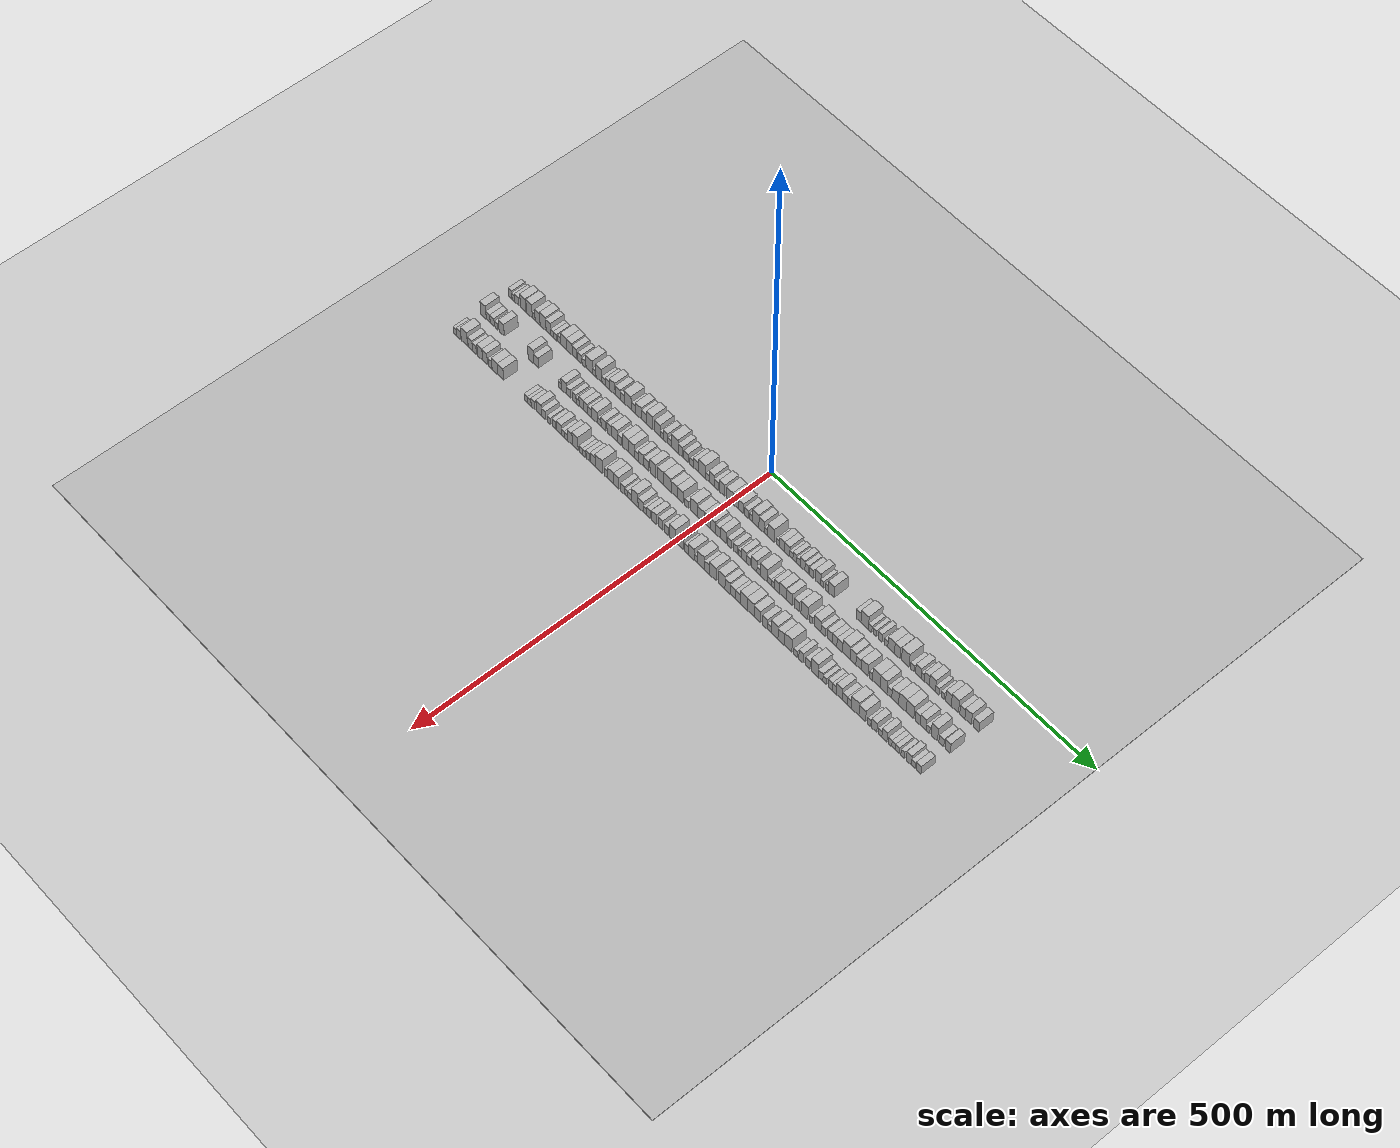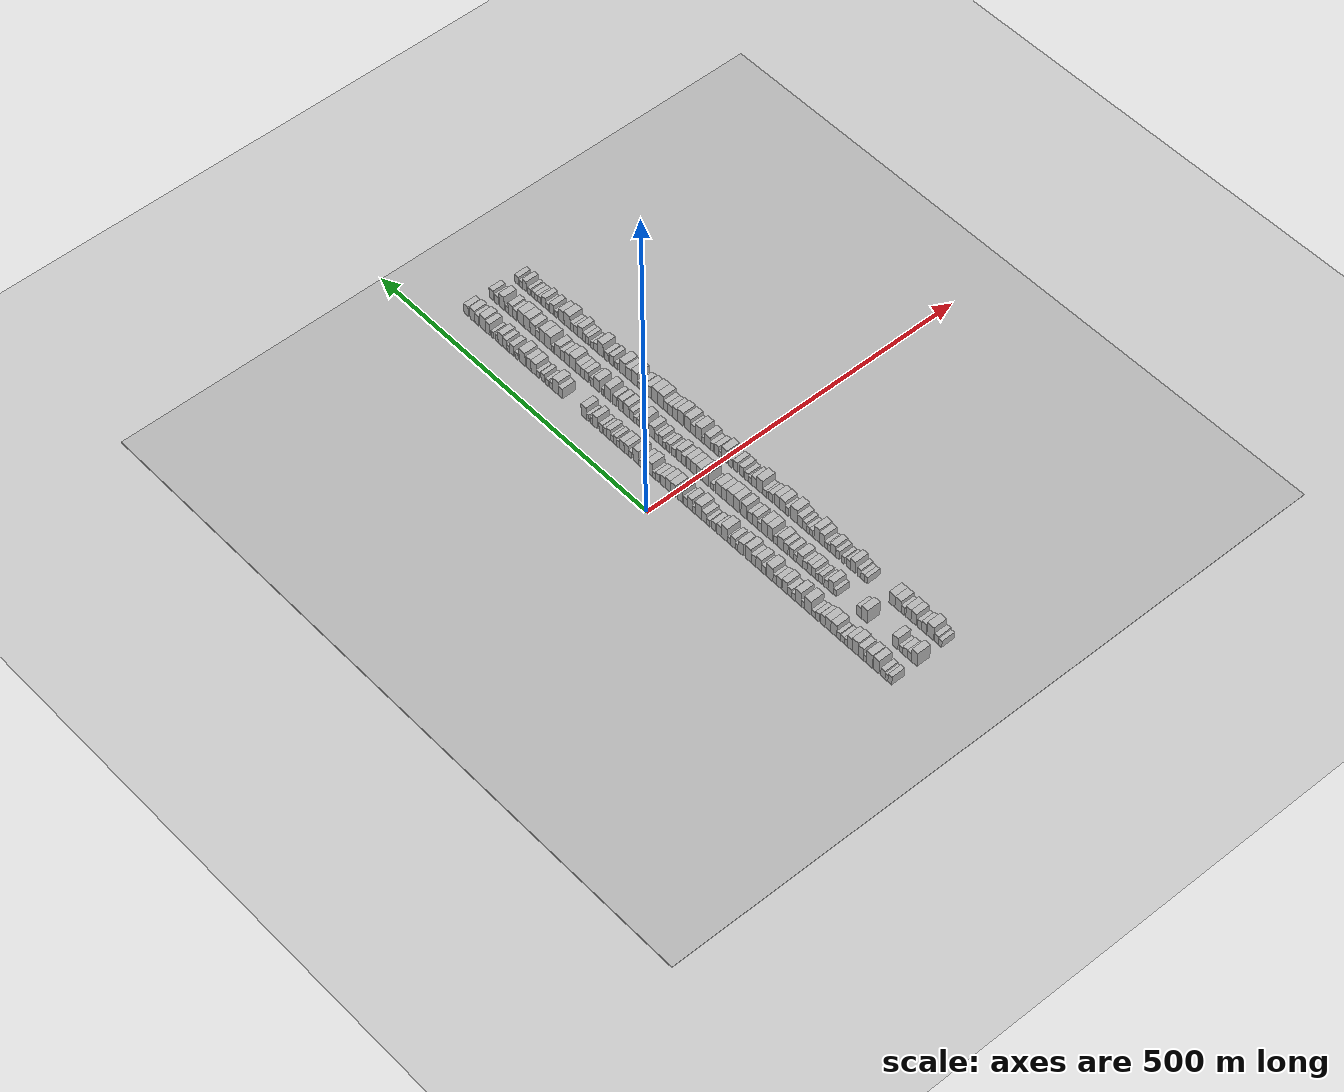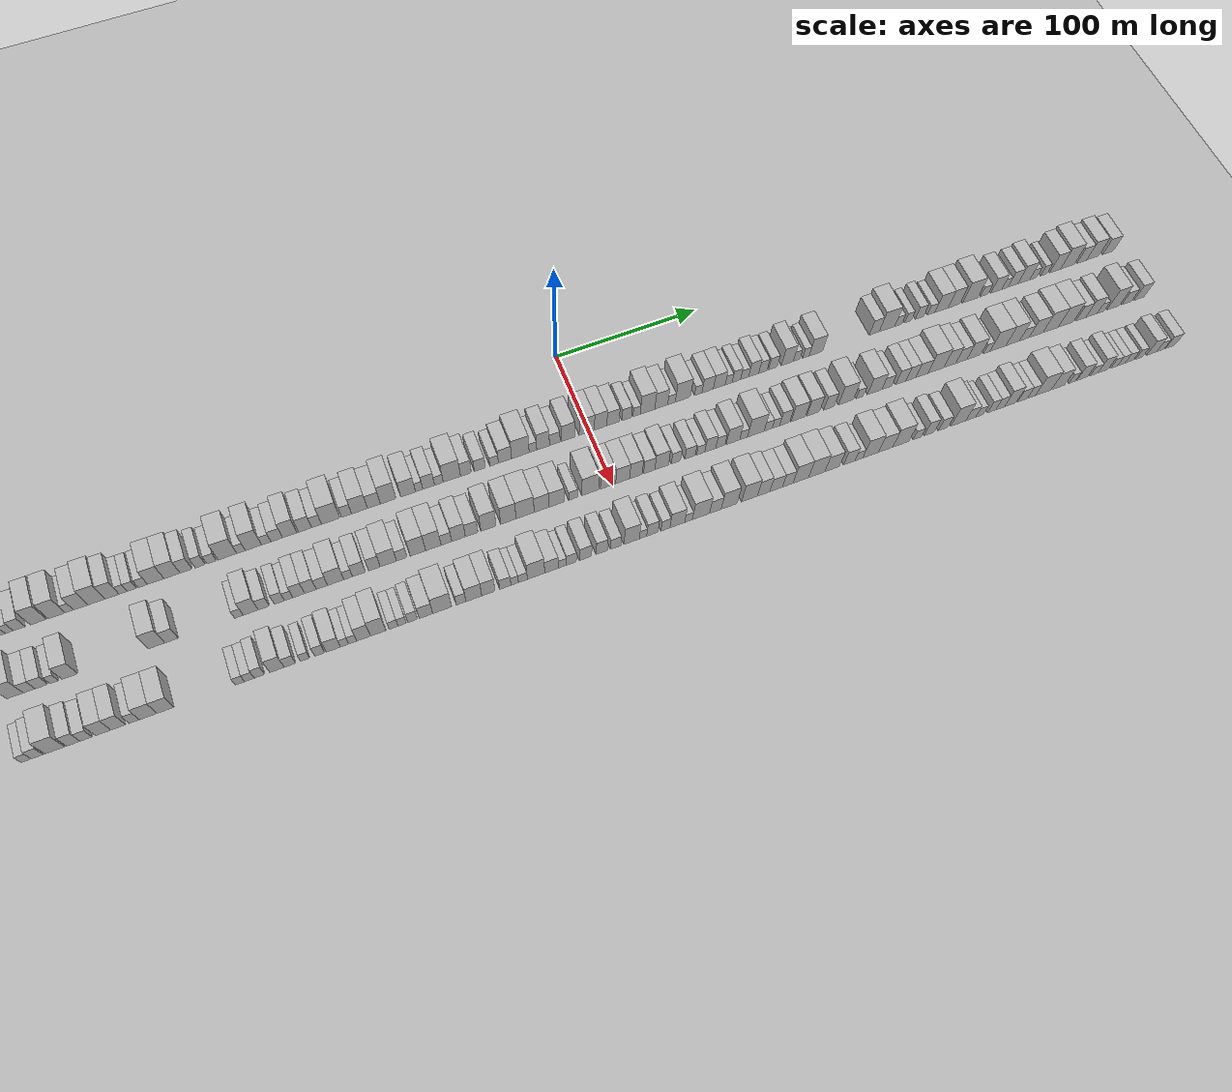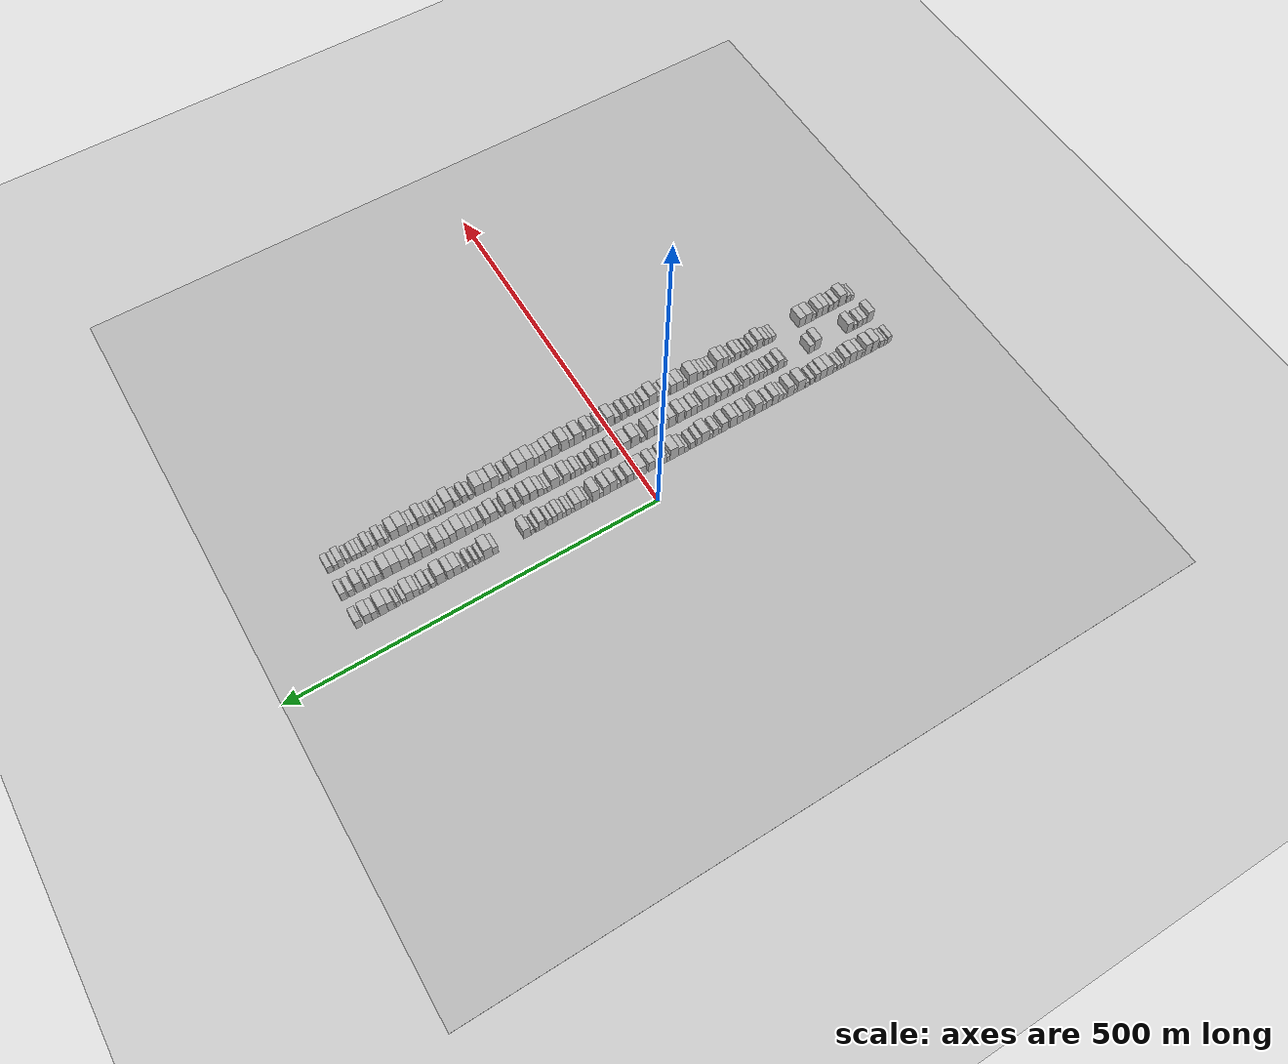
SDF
<?xml version="1.0" encoding="utf-8"?>

<sdf version="1.6">

   <world name="default">

      <gui fullscreen="0">

         <camera name="user_camera">

            <pose>-15 0 4.57585 0 0 0</pose>

            <view_controller>orbit</view_controller>

         </camera>

      </gui>

      <scene>

         <sky>

           <clouds>

             <speed>12</speed>

           </clouds>

         </sky>

         <ambient>0.4 0.4 0.4 1</ambient>

         <background>0.7 0.7 0.7 1</background>

         <shadows>1</shadows>

      </scene>

      <gravity>0 0 -9.8066</gravity>

      <magnetic_field>6e-06 2.3e-05 -4.2e-05</magnetic_field>

      <physics default="0" name="default_physics" type="ode">

         <ode>

            <solver>

               <type>quick</type>

               <iters>10</iters>

               <sor>1.0</sor>

               <use_dynamic_moi_rescaling>0</use_dynamic_moi_rescaling>

            </solver>

            <constraints>

               <cfm>0</cfm>

               <erp>0.2</erp>

               <contact_max_correcting_vel>100</contact_max_correcting_vel>

               <contact_surface_layer>0.001</contact_surface_layer>

            </constraints>

         </ode>

         <max_step_size>0.004</max_step_size>

         <real_time_factor>1</real_time_factor>

         <real_time_update_rate>250</real_time_update_rate>

      </physics>

      <light name="sun" type="directional">

         <cast_shadows>1</cast_shadows>

         <pose>0 0 10 0 0 0</pose>

         <diffuse>0.8 0.8 0.8 1</diffuse>

         <specular>0.2 0.2 0.2 1</specular>

         <attenuation>

            <range>1000</range>

            <constant>0.9</constant>

            <linear>0.01</linear>

            <quadratic>0.001</quadratic>

         </attenuation>

         <direction>-0.5 0.1 -0.9</direction>

      </light>

      <include>

         <name>ground_plane_1</name>

         <uri>model://HANNAS_ground_plane</uri>

         <pose>0 0 0  0 0 0</pose>

      </include>

      <include>

         <name>ground_plane_2</name>

         <uri>model://HANNAS_ground_plane</uri>

         <pose>100 0 0  0 0 0</pose>

      </include>

      <model name="building_1">

         <static>1</static>

         <pose frame="">50.0000 -376.7709 0 0.000000 0.000000 0.000000</pose>

         <link name="link">

            <pose frame="">0 0 7.50 0 0 0</pose>

            <collision name="collision">

               <geometry>

                  <box>

                     <size>20.0000 6.4582 15.0000</size>

                  </box>

               </geometry>

               <max_contacts>10</max_contacts>

               <surface>

                  <contact>

                     <ode/>

                  </contact>

                  <bounce/>

                  <friction>

                     <torsional>

                        <ode/>

                     </torsional>

                     <ode/>

                  </friction>

               </surface>

            </collision>

            <visual name="visual">

               <cast_shadows>0</cast_shadows>

               <geometry>

                  <box>

                     <size>20.0000 6.4582 15.0000</size>

                  </box>

               </geometry>

               <material>

                  <script>

                     <uri>model://HANNAS_wall/materials/scripts</uri>

                     <uri>model://HANNAS_wall/materials/textures</uri>

                     <name>vrc/HANNAS_wall</name>

                  </script>

               </material>

            </visual>

            <self_collide>0</self_collide>

            <enable_wind>0</enable_wind>

            <kinematic>0</kinematic>

         </link>

      </model>

      <model name="building_2">

         <static>1</static>

         <pose frame="">50.0000 -371.1102 0 0.000000 0.000000 0.000000</pose>

         <link name="link">

            <pose frame="">0 0 6.00 0 0 0</pose>

            <collision name="collision">

               <geometry>

                  <box>

                     <size>20.0000 4.8632 12.0000</size>

                  </box>

               </geometry>

               <max_contacts>10</max_contacts>

               <surface>

                  <contact>

                     <ode/>

                  </contact>

                  <bounce/>

                  <friction>

                     <torsional>

                        <ode/>

                     </torsional>

                     <ode/>

                  </friction>

               </surface>

            </collision>

            <visual name="visual">

               <cast_shadows>0</cast_shadows>

               <geometry>

                  <box>

                     <size>20.0000 4.8632 12.0000</size>

                  </box>

               </geometry>

               <material>

                  <script>

                     <uri>model://HANNAS_wall/materials/scripts</uri>

                     <uri>model://HANNAS_wall/materials/textures</uri>

                     <name>vrc/HANNAS_wall</name>

                  </script>

               </material>

            </visual>

            <self_collide>0</self_collide>

            <enable_wind>0</enable_wind>

            <kinematic>0</kinematic>

         </link>

      </model>

      <model name="building_3">

         <static>1</static>

         <pose frame="">50.0000 -365.1299 0 0.000000 0.000000 0.000000</pose>

         <link name="link">

            <pose frame="">0 0 7.50 0 0 0</pose>

            <collision name="collision">

               <geometry>

                  <box>

                     <size>20.0000 7.0973 15.0000</size>

                  </box>

               </geometry>

               <max_contacts>10</max_contacts>

               <surface>

                  <contact>

                     <ode/>

                  </contact>

                  <bounce/>

                  <friction>

                     <torsional>

                        <ode/>

                     </torsional>

                     <ode/>

                  </friction>

               </surface>

            </collision>

            <visual name="visual">

               <cast_shadows>0</cast_shadows>

               <geometry>

                  <box>

                     <size>20.0000 7.0973 15.0000</size>

                  </box>

               </geometry>

               <material>

                  <script>

                     <uri>model://HANNAS_wall/materials/scripts</uri>

                     <uri>model://HANNAS_wall/materials/textures</uri>

                     <name>vrc/HANNAS_wall</name>

                  </script>

               </material>

            </visual>

            <self_collide>0</self_collide>

            <enable_wind>0</enable_wind>

            <kinematic>0</kinematic>

         </link>

      </model>

      <model name="building_4">

         <static>1</static>

         <pose frame="">50.0000 -353.7452 0 0.000000 0.000000 0.000000</pose>

         <link name="link">

            <pose frame="">0 0 12.00 0 0 0</pose>

            <collision name="collision">

               <geometry>

                  <box>

                     <size>20.0000 9.6722 24.0000</size>

                  </box>

               </geometry>

               <max_contacts>10</max_contacts>

               <surface>

                  <contact>

                     <ode/>

                  </contact>

                  <bounce/>

                  <friction>

                     <torsional>

                        <ode/>

                     </torsional>

                     <ode/>

                  </friction>

               </surface>

            </collision>

            <visual name="visual">

               <cast_shadows>0</cast_shadows>

               <geometry>

                  <box>

                     <size>20.0000 9.6722 24.0000</size>

                  </box>

               </geometry>

               <material>

                  <script>

                     <uri>model://HANNAS_wall/materials/scripts</uri>

                     <uri>model://HANNAS_wall/materials/textures</uri>

                     <name>vrc/HANNAS_wall</name>

                  </script>

               </material>

            </visual>

            <self_collide>0</self_collide>

            <enable_wind>0</enable_wind>

            <kinematic>0</kinematic>

         </link>

      </model>

      <model name="building_5">

         <static>1</static>

         <pose frame="">50.0000 -342.7592 0 0.000000 0.000000 0.000000</pose>

         <link name="link">

            <pose frame="">0 0 12.00 0 0 0</pose>

            <collision name="collision">

               <geometry>

                  <box>

                     <size>20.0000 10.2998 24.0000</size>

                  </box>

               </geometry>

               <max_contacts>10</max_contacts>

               <surface>

                  <contact>

                     <ode/>

                  </contact>

                  <bounce/>

                  <friction>

                     <torsional>

                        <ode/>

                     </torsional>

                     <ode/>

                  </friction>

               </surface>

            </collision>

            <visual name="visual">

               <cast_shadows>0</cast_shadows>

               <geometry>

                  <box>

                     <size>20.0000 10.2998 24.0000</size>

                  </box>

               </geometry>

               <material>

                  <script>

                     <uri>model://HANNAS_wall/materials/scripts</uri>

                     <uri>model://HANNAS_wall/materials/textures</uri>

                     <name>vrc/HANNAS_wall</name>

                  </script>

               </material>

            </visual>

            <self_collide>0</self_collide>

            <enable_wind>0</enable_wind>

            <kinematic>0</kinematic>

         </link>

      </model>

      <model name="building_6">

         <static>1</static>

         <pose frame="">50.0000 -335.1604 0 0.000000 0.000000 0.000000</pose>

         <link name="link">

            <pose frame="">0 0 6.00 0 0 0</pose>

            <collision name="collision">

               <geometry>

                  <box>

                     <size>20.0000 4.8978 12.0000</size>

                  </box>

               </geometry>

               <max_contacts>10</max_contacts>

               <surface>

                  <contact>

                     <ode/>

                  </contact>

                  <bounce/>

                  <friction>

                     <torsional>

                        <ode/>

                     </torsional>

                     <ode/>

                  </friction>

               </surface>

            </collision>

            <visual name="visual">

               <cast_shadows>0</cast_shadows>

               <geometry>

                  <box>

                     <size>20.0000 4.8978 12.0000</size>

                  </box>

               </geometry>

               <material>

                  <script>

                     <uri>model://HANNAS_wall/materials/scripts</uri>

                     <uri>model://HANNAS_wall/materials/textures</uri>

                     <name>vrc/HANNAS_wall</name>

                  </script>

               </material>

            </visual>

            <self_collide>0</self_collide>

            <enable_wind>0</enable_wind>

            <kinematic>0</kinematic>

         </link>

      </model>

      <model name="building_7">

         <static>1</static>

         <pose frame="">50.0000 -328.3325 0 0.000000 0.000000 0.000000</pose>

         <link name="link">

            <pose frame="">0 0 10.50 0 0 0</pose>

            <collision name="collision">

               <geometry>

                  <box>

                     <size>20.0000 8.7580 21.0000</size>

                  </box>

               </geometry>

               <max_contacts>10</max_contacts>

               <surface>

                  <contact>

                     <ode/>

                  </contact>

                  <bounce/>

                  <friction>

                     <torsional>

                        <ode/>

                     </torsional>

                     <ode/>

                  </friction>

               </surface>

            </collision>

            <visual name="visual">

               <cast_shadows>0</cast_shadows>

               <geometry>

                  <box>

                     <size>20.0000 8.7580 21.0000</size>

                  </box>

               </geometry>

               <material>

                  <script>

                     <uri>model://HANNAS_wall/materials/scripts</uri>

                     <uri>model://HANNAS_wall/materials/textures</uri>

                     <name>vrc/HANNAS_wall</name>

                  </script>

               </material>

            </visual>

            <self_collide>0</self_collide>

            <enable_wind>0</enable_wind>

            <kinematic>0</kinematic>

         </link>

      </model>

      <model name="building_8">

         <static>1</static>

         <pose frame="">50.0000 -318.6570 0 0.000000 0.000000 0.000000</pose>

         <link name="link">

            <pose frame="">0 0 12.00 0 0 0</pose>

            <collision name="collision">

               <geometry>

                  <box>

                     <size>20.0000 10.5930 24.0000</size>

                  </box>

               </geometry>

               <max_contacts>10</max_contacts>

               <surface>

                  <contact>

                     <ode/>

                  </contact>

                  <bounce/>

                  <friction>

                     <torsional>

                        <ode/>

                     </torsional>

                     <ode/>

                  </friction>

               </surface>

            </collision>

            <visual name="visual">

               <cast_shadows>0</cast_shadows>

               <geometry>

                  <box>

                     <size>20.0000 10.5930 24.0000</size>

                  </box>

               </geometry>

               <material>

                  <script>

                     <uri>model://HANNAS_wall/materials/scripts</uri>

                     <uri>model://HANNAS_wall/materials/textures</uri>

                     <name>vrc/HANNAS_wall</name>

                  </script>

               </material>

            </visual>

            <self_collide>0</self_collide>

            <enable_wind>0</enable_wind>

            <kinematic>0</kinematic>

         </link>

      </model>

      <model name="building_9">

         <static>1</static>

         <pose frame="">50.0000 -309.1491 0 0.000000 0.000000 0.000000</pose>

         <link name="link">

            <pose frame="">0 0 10.50 0 0 0</pose>

            <collision name="collision">

               <geometry>

                  <box>

                     <size>20.0000 8.4227 21.0000</size>

                  </box>

               </geometry>

               <max_contacts>10</max_contacts>

               <surface>

                  <contact>

                     <ode/>

                  </contact>

                  <bounce/>

                  <friction>

                     <torsional>

                        <ode/>

                     </torsional>

                     <ode/>

                  </friction>

               </surface>

            </collision>

            <visual name="visual">

               <cast_shadows>0</cast_shadows>

               <geometry>

                  <box>

                     <size>20.0000 8.4227 21.0000</size>

                  </box>

               </geometry>

               <material>

                  <script>

                     <uri>model://HANNAS_wall/materials/scripts</uri>

                     <uri>model://HANNAS_wall/materials/textures</uri>

                     <name>vrc/HANNAS_wall</name>

                  </script>

               </material>

            </visual>

            <self_collide>0</self_collide>

            <enable_wind>0</enable_wind>

            <kinematic>0</kinematic>

         </link>

      </model>

      <model name="building_10">

         <static>1</static>

         <pose frame="">50.0000 -302.4947 0 0.000000 0.000000 0.000000</pose>

         <link name="link">

            <pose frame="">0 0 6.00 0 0 0</pose>

            <collision name="collision">

               <geometry>

                  <box>

                     <size>20.0000 4.8862 12.0000</size>

                  </box>

               </geometry>

               <max_contacts>10</max_contacts>

               <surface>

                  <contact>

                     <ode/>

                  </contact>

                  <bounce/>

                  <friction>

                     <torsional>

                        <ode/>

                     </torsional>

                     <ode/>

                  </friction>

               </surface>

            </collision>

            <visual name="visual">

               <cast_shadows>0</cast_shadows>

               <geometry>

                  <box>

                     <size>20.0000 4.8862 12.0000</size>

                  </box>

               </geometry>

               <material>

                  <script>

                     <uri>model://HANNAS_wall/materials/scripts</uri>

                     <uri>model://HANNAS_wall/materials/textures</uri>

                     <name>vrc/HANNAS_wall</name>

                  </script>

               </material>

            </visual>

            <self_collide>0</self_collide>

            <enable_wind>0</enable_wind>

            <kinematic>0</kinematic>

         </link>

      </model>

      <model name="building_11">

         <static>1</static>

         <pose frame="">50.0000 -297.1440 0 0.000000 0.000000 0.000000</pose>

         <link name="link">

            <pose frame="">0 0 6.00 0 0 0</pose>

            <collision name="collision">

               <geometry>

                  <box>

                     <size>20.0000 5.8152 12.0000</size>

                  </box>

               </geometry>

               <max_contacts>10</max_contacts>

               <surface>

                  <contact>

                     <ode/>

                  </contact>

                  <bounce/>

                  <friction>

                     <torsional>

                        <ode/>

                     </torsional>

                     <ode/>

                  </friction>

               </surface>

            </collision>

            <visual name="visual">

               <cast_shadows>0</cast_shadows>

               <geometry>

                  <box>

                     <size>20.0000 5.8152 12.0000</size>

                  </box>

               </geometry>

               <material>

                  <script>

                     <uri>model://HANNAS_wall/materials/scripts</uri>

                     <uri>model://HANNAS_wall/materials/textures</uri>

                     <name>vrc/HANNAS_wall</name>

                  </script>

               </material>

            </visual>

            <self_collide>0</self_collide>

            <enable_wind>0</enable_wind>

            <kinematic>0</kinematic>

         </link>

      </model>

      <model name="building_12">

         <static>1</static>

         <pose frame="">50.0000 -290.3620 0 0.000000 0.000000 0.000000</pose>

         <link name="link">

            <pose frame="">0 0 6.00 0 0 0</pose>

            <collision name="collision">

               <geometry>

                  <box>

                     <size>20.0000 5.7487 12.0000</size>

                  </box>

               </geometry>

               <max_contacts>10</max_contacts>

               <surface>

                  <contact>

                     <ode/>

                  </contact>

                  <bounce/>

                  <friction>

                     <torsional>

                        <ode/>

                     </torsional>

                     <ode/>

                  </friction>

               </surface>

            </collision>

            <visual name="visual">

               <cast_shadows>0</cast_shadows>

               <geometry>

                  <box>

                     <size>20.0000 5.7487 12.0000</size>

                  </box>

               </geometry>

               <material>

                  <script>

                     <uri>model://HANNAS_wall/materials/scripts</uri>

                     <uri>model://HANNAS_wall/materials/textures</uri>

                     <name>vrc/HANNAS_wall</name>

                  </script>

               </material>

            </visual>

            <self_collide>0</self_collide>

            <enable_wind>0</enable_wind>

            <kinematic>0</kinematic>

         </link>

      </model>

      <model name="building_13">

         <static>1</static>

         <pose frame="">50.0000 -282.4075 0 0.000000 0.000000 0.000000</pose>

         <link name="link">

            <pose frame="">0 0 10.50 0 0 0</pose>

            <collision name="collision">

               <geometry>

                  <box>

                     <size>20.0000 10.1604 21.0000</size>

                  </box>

               </geometry>

               <max_contacts>10</max_contacts>

               <surface>

                  <contact>

                     <ode/>

                  </contact>

                  <bounce/>

                  <friction>

                     <torsional>

                        <ode/>

                     </torsional>

                     <ode/>

                  </friction>

               </surface>

            </collision>

            <visual name="visual">

               <cast_shadows>0</cast_shadows>

               <geometry>

                  <box>

                     <size>20.0000 10.1604 21.0000</size>

                  </box>

               </geometry>

               <material>

                  <script>

                     <uri>model://HANNAS_wall/materials/scripts</uri>

                     <uri>model://HANNAS_wall/materials/textures</uri>

                     <name>vrc/HANNAS_wall</name>

                  </script>

               </material>

            </visual>

            <self_collide>0</self_collide>

            <enable_wind>0</enable_wind>

            <kinematic>0</kinematic>

         </link>

      </model>

      <model name="building_14">

         <static>1</static>

         <pose frame="">50.0000 -272.3864 0 0.000000 0.000000 0.000000</pose>

         <link name="link">

            <pose frame="">0 0 10.50 0 0 0</pose>

            <collision name="collision">

               <geometry>

                  <box>

                     <size>20.0000 9.8817 21.0000</size>

                  </box>

               </geometry>

               <max_contacts>10</max_contacts>

               <surface>

                  <contact>

                     <ode/>

                  </contact>

                  <bounce/>

                  <friction>

                     <torsional>

                        <ode/>

                     </torsional>

                     <ode/>

                  </friction>

               </surface>

            </collision>

            <visual name="visual">

               <cast_shadows>0</cast_shadows>

               <geometry>

                  <box>

                     <size>20.0000 9.8817 21.0000</size>

                  </box>

               </geometry>

               <material>

                  <script>

                     <uri>model://HANNAS_wall/materials/scripts</uri>

                     <uri>model://HANNAS_wall/materials/textures</uri>

                     <name>vrc/HANNAS_wall</name>

                  </script>

               </material>

            </visual>

            <self_collide>0</self_collide>

            <enable_wind>0</enable_wind>

            <kinematic>0</kinematic>

         </link>

      </model>

      <model name="building_15">

         <static>1</static>

         <pose frame="">50.0000 -263.7044 0 0.000000 0.000000 0.000000</pose>

         <link name="link">

            <pose frame="">0 0 9.00 0 0 0</pose>

            <collision name="collision">

               <geometry>

                  <box>

                     <size>20.0000 7.4823 18.0000</size>

                  </box>

               </geometry>

               <max_contacts>10</max_contacts>

               <surface>

                  <contact>

                     <ode/>

                  </contact>

                  <bounce/>

                  <friction>

                     <torsional>

                        <ode/>

                     </torsional>

                     <ode/>

                  </friction>

               </surface>

            </collision>

            <visual name="visual">

               <cast_shadows>0</cast_shadows>

               <geometry>

                  <box>

                     <size>20.0000 7.4823 18.0000</size>

                  </box>

               </geometry>

               <material>

                  <script>

                     <uri>model://HANNAS_wall/materials/scripts</uri>

                     <uri>model://HANNAS_wall/materials/textures</uri>

                     <name>vrc/HANNAS_wall</name>

                  </script>

               </material>

            </visual>

            <self_collide>0</self_collide>

            <enable_wind>0</enable_wind>

            <kinematic>0</kinematic>

         </link>

      </model>

      <model name="building_16">

         <static>1</static>

         <pose frame="">50.0000 -254.8468 0 0.000000 0.000000 0.000000</pose>

         <link name="link">

            <pose frame="">0 0 7.50 0 0 0</pose>

            <collision name="collision">

               <geometry>

                  <box>

                     <size>20.0000 6.2329 15.0000</size>

                  </box>

               </geometry>

               <max_contacts>10</max_contacts>

               <surface>

                  <contact>

                     <ode/>

                  </contact>

                  <bounce/>

                  <friction>

                     <torsional>

                        <ode/>

                     </torsional>

                     <ode/>

                  </friction>

               </surface>

            </collision>

            <visual name="visual">

               <cast_shadows>0</cast_shadows>

               <geometry>

                  <box>

                     <size>20.0000 6.2329 15.0000</size>

                  </box>

               </geometry>

               <material>

                  <script>

                     <uri>model://HANNAS_wall/materials/scripts</uri>

                     <uri>model://HANNAS_wall/materials/textures</uri>

                     <name>vrc/HANNAS_wall</name>

                  </script>

               </material>

            </visual>

            <self_collide>0</self_collide>

            <enable_wind>0</enable_wind>

            <kinematic>0</kinematic>

         </link>

      </model>

      <model name="building_17">

         <static>1</static>

         <pose frame="">50.0000 -247.7488 0 0.000000 0.000000 0.000000</pose>

         <link name="link">

            <pose frame="">0 0 6.00 0 0 0</pose>

            <collision name="collision">

               <geometry>

                  <box>

                     <size>20.0000 5.9631 12.0000</size>

                  </box>

               </geometry>

               <max_contacts>10</max_contacts>

               <surface>

                  <contact>

                     <ode/>

                  </contact>

                  <bounce/>

                  <friction>

                     <torsional>

                        <ode/>

                     </torsional>

                     <ode/>

                  </friction>

               </surface>

            </collision>

            <visual name="visual">

               <cast_shadows>0</cast_shadows>

               <geometry>

                  <box>

                     <size>20.0000 5.9631 12.0000</size>

                  </box>

               </geometry>

               <material>

                  <script>

                     <uri>model://HANNAS_wall/materials/scripts</uri>

                     <uri>model://HANNAS_wall/materials/textures</uri>

                     <name>vrc/HANNAS_wall</name>

                  </script>

               </material>

            </visual>

            <self_collide>0</self_collide>

            <enable_wind>0</enable_wind>

            <kinematic>0</kinematic>

         </link>

      </model>

      <model name="building_18">

         <static>1</static>

         <pose frame="">50.0000 -237.8741 0 0.000000 0.000000 0.000000</pose>

         <link name="link">

            <pose frame="">0 0 12.00 0 0 0</pose>

            <collision name="collision">

               <geometry>

                  <box>

                     <size>20.0000 11.7863 24.0000</size>

                  </box>

               </geometry>

               <max_contacts>10</max_contacts>

               <surface>

                  <contact>

                     <ode/>

                  </contact>

                  <bounce/>

                  <friction>

                     <torsional>

                        <ode/>

                     </torsional>

                     <ode/>

                  </friction>

               </surface>

            </collision>

            <visual name="visual">

               <cast_shadows>0</cast_shadows>

               <geometry>

                  <box>

                     <size>20.0000 11.7863 24.0000</size>

                  </box>

               </geometry>

               <material>

                  <script>

                     <uri>model://HANNAS_wall/materials/scripts</uri>

                     <uri>model://HANNAS_wall/materials/textures</uri>

                     <name>vrc/HANNAS_wall</name>

                  </script>

               </material>

            </visual>

            <self_collide>0</self_collide>

            <enable_wind>0</enable_wind>

            <kinematic>0</kinematic>

         </link>

      </model>

      <model name="building_19">

         <static>1</static>

         <pose frame="">50.0000 -229.2818 0 0.000000 0.000000 0.000000</pose>

         <link name="link">

            <pose frame="">0 0 6.00 0 0 0</pose>

            <collision name="collision">

               <geometry>

                  <box>

                     <size>20.0000 5.3983 12.0000</size>

                  </box>

               </geometry>

               <max_contacts>10</max_contacts>

               <surface>

                  <contact>

                     <ode/>

                  </contact>

                  <bounce/>

                  <friction>

                     <torsional>

                        <ode/>

                     </torsional>

                     <ode/>

                  </friction>

               </surface>

            </collision>

            <visual name="visual">

               <cast_shadows>0</cast_shadows>

               <geometry>

                  <box>

                     <size>20.0000 5.3983 12.0000</size>

                  </box>

               </geometry>

               <material>

                  <script>

                     <uri>model://HANNAS_wall/materials/scripts</uri>

                     <uri>model://HANNAS_wall/materials/textures</uri>

                     <name>vrc/HANNAS_wall</name>

                  </script>

               </material>

            </visual>

            <self_collide>0</self_collide>

            <enable_wind>0</enable_wind>

            <kinematic>0</kinematic>

         </link>

      </model>

      <model name="building_20">

         <static>1</static>

         <pose frame="">50.0000 -221.4287 0 0.000000 0.000000 0.000000</pose>

         <link name="link">

            <pose frame="">0 0 12.00 0 0 0</pose>

            <collision name="collision">

               <geometry>

                  <box>

                     <size>20.0000 10.3080 24.0000</size>

                  </box>

               </geometry>

               <max_contacts>10</max_contacts>

               <surface>

                  <contact>

                     <ode/>

                  </contact>

                  <bounce/>

                  <friction>

                     <torsional>

                        <ode/>

                     </torsional>

                     <ode/>

                  </friction>

               </surface>

            </collision>

            <visual name="visual">

               <cast_shadows>0</cast_shadows>

               <geometry>

                  <box>

                     <size>20.0000 10.3080 24.0000</size>

                  </box>

               </geometry>

               <material>

                  <script>

                     <uri>model://HANNAS_wall/materials/scripts</uri>

                     <uri>model://HANNAS_wall/materials/textures</uri>

                     <name>vrc/HANNAS_wall</name>

                  </script>

               </material>

            </visual>

            <self_collide>0</self_collide>

            <enable_wind>0</enable_wind>

            <kinematic>0</kinematic>

         </link>

      </model>

      <model name="building_21">

         <static>1</static>

         <pose frame="">50.0000 -213.3474 0 0.000000 0.000000 0.000000</pose>

         <link name="link">

            <pose frame="">0 0 6.00 0 0 0</pose>

            <collision name="collision">

               <geometry>

                  <box>

                     <size>20.0000 5.8545 12.0000</size>

                  </box>

               </geometry>

               <max_contacts>10</max_contacts>

               <surface>

                  <contact>

                     <ode/>

                  </contact>

                  <bounce/>

                  <friction>

                     <torsional>

                        <ode/>

                     </torsional>

                     <ode/>

                  </friction>

               </surface>

            </collision>

            <visual name="visual">

               <cast_shadows>0</cast_shadows>

               <geometry>

                  <box>

                     <size>20.0000 5.8545 12.0000</size>

                  </box>

               </geometry>

               <material>

                  <script>

                     <uri>model://HANNAS_wall/materials/scripts</uri>

                     <uri>model://HANNAS_wall/materials/textures</uri>

                     <name>vrc/HANNAS_wall</name>

                  </script>

               </material>

            </visual>

            <self_collide>0</self_collide>

            <enable_wind>0</enable_wind>

            <kinematic>0</kinematic>

         </link>

      </model>

      <model name="building_22">

         <static>1</static>

         <pose frame="">50.0000 -206.7290 0 0.000000 0.000000 0.000000</pose>

         <link name="link">

            <pose frame="">0 0 7.50 0 0 0</pose>

            <collision name="collision">

               <geometry>

                  <box>

                     <size>20.0000 7.3823 15.0000</size>

                  </box>

               </geometry>

               <max_contacts>10</max_contacts>

               <surface>

                  <contact>

                     <ode/>

                  </contact>

                  <bounce/>

                  <friction>

                     <torsional>

                        <ode/>

                     </torsional>

                     <ode/>

                  </friction>

               </surface>

            </collision>

            <visual name="visual">

               <cast_shadows>0</cast_shadows>

               <geometry>

                  <box>

                     <size>20.0000 7.3823 15.0000</size>

                  </box>

               </geometry>

               <material>

                  <script>

                     <uri>model://HANNAS_wall/materials/scripts</uri>

                     <uri>model://HANNAS_wall/materials/textures</uri>

                     <name>vrc/HANNAS_wall</name>

                  </script>

               </material>

            </visual>

            <self_collide>0</self_collide>

            <enable_wind>0</enable_wind>

            <kinematic>0</kinematic>

         </link>

      </model>

      <model name="building_23">

         <static>1</static>

         <pose frame="">50.0000 -198.3898 0 0.000000 0.000000 0.000000</pose>

         <link name="link">

            <pose frame="">0 0 10.50 0 0 0</pose>

            <collision name="collision">

               <geometry>

                  <box>

                     <size>20.0000 9.2961 21.0000</size>

                  </box>

               </geometry>

               <max_contacts>10</max_contacts>

               <surface>

                  <contact>

                     <ode/>

                  </contact>

                  <bounce/>

                  <friction>

                     <torsional>

                        <ode/>

                     </torsional>

                     <ode/>

                  </friction>

               </surface>

            </collision>

            <visual name="visual">

               <cast_shadows>0</cast_shadows>

               <geometry>

                  <box>

                     <size>20.0000 9.2961 21.0000</size>

                  </box>

               </geometry>

               <material>

                  <script>

                     <uri>model://HANNAS_wall/materials/scripts</uri>

                     <uri>model://HANNAS_wall/materials/textures</uri>

                     <name>vrc/HANNAS_wall</name>

                  </script>

               </material>

            </visual>

            <self_collide>0</self_collide>

            <enable_wind>0</enable_wind>

            <kinematic>0</kinematic>

         </link>

      </model>

      <model name="building_24">

         <static>1</static>

         <pose frame="">50.0000 -188.6085 0 0.000000 0.000000 0.000000</pose>

         <link name="link">

            <pose frame="">0 0 9.00 0 0 0</pose>

            <collision name="collision">

               <geometry>

                  <box>

                     <size>20.0000 8.2665 18.0000</size>

                  </box>

               </geometry>

               <max_contacts>10</max_contacts>

               <surface>

                  <contact>

                     <ode/>

                  </contact>

                  <bounce/>

                  <friction>

                     <torsional>

                        <ode/>

                     </torsional>

                     <ode/>

                  </friction>

               </surface>

            </collision>

            <visual name="visual">

               <cast_shadows>0</cast_shadows>

               <geometry>

                  <box>

                     <size>20.0000 8.2665 18.0000</size>

                  </box>

               </geometry>

               <material>

                  <script>

                     <uri>model://HANNAS_wall/materials/scripts</uri>

                     <uri>model://HANNAS_wall/materials/textures</uri>

                     <name>vrc/HANNAS_wall</name>

                  </script>

               </material>

            </visual>

            <self_collide>0</self_collide>

            <enable_wind>0</enable_wind>

            <kinematic>0</kinematic>

         </link>

      </model>

      <model name="building_25">

         <static>1</static>

         <pose frame="">50.0000 -181.2819 0 0.000000 0.000000 0.000000</pose>

         <link name="link">

            <pose frame="">0 0 7.50 0 0 0</pose>

            <collision name="collision">

               <geometry>

                  <box>

                     <size>20.0000 6.3867 15.0000</size>

                  </box>

               </geometry>

               <max_contacts>10</max_contacts>

               <surface>

                  <contact>

                     <ode/>

                  </contact>

                  <bounce/>

                  <friction>

                     <torsional>

                        <ode/>

                     </torsional>

                     <ode/>

                  </friction>

               </surface>

            </collision>

            <visual name="visual">

               <cast_shadows>0</cast_shadows>

               <geometry>

                  <box>

                     <size>20.0000 6.3867 15.0000</size>

                  </box>

               </geometry>

               <material>

                  <script>

                     <uri>model://HANNAS_wall/materials/scripts</uri>

                     <uri>model://HANNAS_wall/materials/textures</uri>

                     <name>vrc/HANNAS_wall</name>

                  </script>

               </material>

            </visual>

            <self_collide>0</self_collide>

            <enable_wind>0</enable_wind>

            <kinematic>0</kinematic>

         </link>

      </model>

      <model name="building_26">

         <static>1</static>

         <pose frame="">50.0000 -172.1616 0 0.000000 0.000000 0.000000</pose>

         <link name="link">

            <pose frame="">0 0 12.00 0 0 0</pose>

            <collision name="collision">

               <geometry>

                  <box>

                     <size>20.0000 11.8538 24.0000</size>

                  </box>

               </geometry>

               <max_contacts>10</max_contacts>

               <surface>

                  <contact>

                     <ode/>

                  </contact>

                  <bounce/>

                  <friction>

                     <torsional>

                        <ode/>

                     </torsional>

                     <ode/>

                  </friction>

               </surface>

            </collision>

            <visual name="visual">

               <cast_shadows>0</cast_shadows>

               <geometry>

                  <box>

                     <size>20.0000 11.8538 24.0000</size>

                  </box>

               </geometry>

               <material>

                  <script>

                     <uri>model://HANNAS_wall/materials/scripts</uri>

                     <uri>model://HANNAS_wall/materials/textures</uri>

                     <name>vrc/HANNAS_wall</name>

                  </script>

               </material>

            </visual>

            <self_collide>0</self_collide>

            <enable_wind>0</enable_wind>

            <kinematic>0</kinematic>

         </link>

      </model>

      <model name="building_27">

         <static>1</static>

         <pose frame="">50.0000 -161.9523 0 0.000000 0.000000 0.000000</pose>

         <link name="link">

            <pose frame="">0 0 7.50 0 0 0</pose>

            <collision name="collision">

               <geometry>

                  <box>

                     <size>20.0000 6.5650 15.0000</size>

                  </box>

               </geometry>

               <max_contacts>10</max_contacts>

               <surface>

                  <contact>

                     <ode/>

                  </contact>

                  <bounce/>

                  <friction>

                     <torsional>

                        <ode/>

                     </torsional>

                     <ode/>

                  </friction>

               </surface>

            </collision>

            <visual name="visual">

               <cast_shadows>0</cast_shadows>

               <geometry>

                  <box>

                     <size>20.0000 6.5650 15.0000</size>

                  </box>

               </geometry>

               <material>

                  <script>

                     <uri>model://HANNAS_wall/materials/scripts</uri>

                     <uri>model://HANNAS_wall/materials/textures</uri>

                     <name>vrc/HANNAS_wall</name>

                  </script>

               </material>

            </visual>

            <self_collide>0</self_collide>

            <enable_wind>0</enable_wind>

            <kinematic>0</kinematic>

         </link>

      </model>

      <model name="building_28">

         <static>1</static>

         <pose frame="">50.0000 -153.5523 0 0.000000 0.000000 0.000000</pose>

         <link name="link">

            <pose frame="">0 0 10.50 0 0 0</pose>

            <collision name="collision">

               <geometry>

                  <box>

                     <size>20.0000 10.2349 21.0000</size>

                  </box>

               </geometry>

               <max_contacts>10</max_contacts>

               <surface>

                  <contact>

                     <ode/>

                  </contact>

                  <bounce/>

                  <friction>

                     <torsional>

                        <ode/>

                     </torsional>

                     <ode/>

                  </friction>

               </surface>

            </collision>

            <visual name="visual">

               <cast_shadows>0</cast_shadows>

               <geometry>

                  <box>

                     <size>20.0000 10.2349 21.0000</size>

                  </box>

               </geometry>

               <material>

                  <script>

                     <uri>model://HANNAS_wall/materials/scripts</uri>

                     <uri>model://HANNAS_wall/materials/textures</uri>

                     <name>vrc/HANNAS_wall</name>

                  </script>

               </material>

            </visual>

            <self_collide>0</self_collide>

            <enable_wind>0</enable_wind>

            <kinematic>0</kinematic>

         </link>

      </model>

      <model name="building_29">

         <static>1</static>

         <pose frame="">50.0000 -144.1929 0 0.000000 0.000000 0.000000</pose>

         <link name="link">

            <pose frame="">0 0 9.00 0 0 0</pose>

            <collision name="collision">

               <geometry>

                  <box>

                     <size>20.0000 8.4840 18.0000</size>

                  </box>

               </geometry>

               <max_contacts>10</max_contacts>

               <surface>

                  <contact>

                     <ode/>

                  </contact>

                  <bounce/>

                  <friction>

                     <torsional>

                        <ode/>

                     </torsional>

                     <ode/>

                  </friction>

               </surface>

            </collision>

            <visual name="visual">

               <cast_shadows>0</cast_shadows>

               <geometry>

                  <box>

                     <size>20.0000 8.4840 18.0000</size>

                  </box>

               </geometry>

               <material>

                  <script>

                     <uri>model://HANNAS_wall/materials/scripts</uri>

                     <uri>model://HANNAS_wall/materials/textures</uri>

                     <name>vrc/HANNAS_wall</name>

                  </script>

               </material>

            </visual>

            <self_collide>0</self_collide>

            <enable_wind>0</enable_wind>

            <kinematic>0</kinematic>

         </link>

      </model>

      <model name="building_30">

         <static>1</static>

         <pose frame="">50.0000 -134.8490 0 0.000000 0.000000 0.000000</pose>

         <link name="link">

            <pose frame="">0 0 12.00 0 0 0</pose>

            <collision name="collision">

               <geometry>

                  <box>

                     <size>20.0000 10.2038 24.0000</size>

                  </box>

               </geometry>

               <max_contacts>10</max_contacts>

               <surface>

                  <contact>

                     <ode/>

                  </contact>

                  <bounce/>

                  <friction>

                     <torsional>

                        <ode/>

                     </torsional>

                     <ode/>

                  </friction>

               </surface>

            </collision>

            <visual name="visual">

               <cast_shadows>0</cast_shadows>

               <geometry>

                  <box>

                     <size>20.0000 10.2038 24.0000</size>

                  </box>

               </geometry>

               <material>

                  <script>

                     <uri>model://HANNAS_wall/materials/scripts</uri>

                     <uri>model://HANNAS_wall/materials/textures</uri>

                     <name>vrc/HANNAS_wall</name>

                  </script>

               </material>

            </visual>

            <self_collide>0</self_collide>

            <enable_wind>0</enable_wind>

            <kinematic>0</kinematic>

         </link>

      </model>

      <model name="building_31">

         <static>1</static>

         <pose frame="">50.0000 -121.8884 0 0.000000 0.000000 0.000000</pose>

         <link name="link">

            <pose frame="">0 0 10.50 0 0 0</pose>

            <collision name="collision">

               <geometry>

                  <box>

                     <size>20.0000 9.7175 21.0000</size>

                  </box>

               </geometry>

               <max_contacts>10</max_contacts>

               <surface>

                  <contact>

                     <ode/>

                  </contact>

                  <bounce/>

                  <friction>

                     <torsional>

                        <ode/>

                     </torsional>

                     <ode/>

                  </friction>

               </surface>

            </collision>

            <visual name="visual">

               <cast_shadows>0</cast_shadows>

               <geometry>

                  <box>

                     <size>20.0000 9.7175 21.0000</size>

                  </box>

               </geometry>

               <material>

                  <script>

                     <uri>model://HANNAS_wall/materials/scripts</uri>

                     <uri>model://HANNAS_wall/materials/textures</uri>

                     <name>vrc/HANNAS_wall</name>

                  </script>

               </material>

            </visual>

            <self_collide>0</self_collide>

            <enable_wind>0</enable_wind>

            <kinematic>0</kinematic>

         </link>

      </model>

      <model name="building_32">

         <static>1</static>

         <pose frame="">50.0000 -114.6272 0 0.000000 0.000000 0.000000</pose>

         <link name="link">

            <pose frame="">0 0 6.00 0 0 0</pose>

            <collision name="collision">

               <geometry>

                  <box>

                     <size>20.0000 4.8048 12.0000</size>

                  </box>

               </geometry>

               <max_contacts>10</max_contacts>

               <surface>

                  <contact>

                     <ode/>

                  </contact>

                  <bounce/>

                  <friction>

                     <torsional>

                        <ode/>

                     </torsional>

                     <ode/>

                  </friction>

               </surface>

            </collision>

            <visual name="visual">

               <cast_shadows>0</cast_shadows>

               <geometry>

                  <box>

                     <size>20.0000 4.8048 12.0000</size>

                  </box>

               </geometry>

               <material>

                  <script>

                     <uri>model://HANNAS_wall/materials/scripts</uri>

                     <uri>model://HANNAS_wall/materials/textures</uri>

                     <name>vrc/HANNAS_wall</name>

                  </script>

               </material>

            </visual>

            <self_collide>0</self_collide>

            <enable_wind>0</enable_wind>

            <kinematic>0</kinematic>

         </link>

      </model>

      <model name="building_33">

         <static>1</static>

         <pose frame="">50.0000 -108.3308 0 0.000000 0.000000 0.000000</pose>

         <link name="link">

            <pose frame="">0 0 9.00 0 0 0</pose>

            <collision name="collision">

               <geometry>

                  <box>

                     <size>20.0000 7.7881 18.0000</size>

                  </box>

               </geometry>

               <max_contacts>10</max_contacts>

               <surface>

                  <contact>

                     <ode/>

                  </contact>

                  <bounce/>

                  <friction>

                     <torsional>

                        <ode/>

                     </torsional>

                     <ode/>

                  </friction>

               </surface>

            </collision>

            <visual name="visual">

               <cast_shadows>0</cast_shadows>

               <geometry>

                  <box>

                     <size>20.0000 7.7881 18.0000</size>

                  </box>

               </geometry>

               <material>

                  <script>

                     <uri>model://HANNAS_wall/materials/scripts</uri>

                     <uri>model://HANNAS_wall/materials/textures</uri>

                     <name>vrc/HANNAS_wall</name>

                  </script>

               </material>

            </visual>

            <self_collide>0</self_collide>

            <enable_wind>0</enable_wind>

            <kinematic>0</kinematic>

         </link>

      </model>

      <model name="building_34">

         <static>1</static>

         <pose frame="">50.0000 -101.5725 0 0.000000 0.000000 0.000000</pose>

         <link name="link">

            <pose frame="">0 0 6.00 0 0 0</pose>

            <collision name="collision">

               <geometry>

                  <box>

                     <size>20.0000 5.7284 12.0000</size>

                  </box>

               </geometry>

               <max_contacts>10</max_contacts>

               <surface>

                  <contact>

                     <ode/>

                  </contact>

                  <bounce/>

                  <friction>

                     <torsional>

                        <ode/>

                     </torsional>

                     <ode/>

                  </friction>

               </surface>

            </collision>

            <visual name="visual">

               <cast_shadows>0</cast_shadows>

               <geometry>

                  <box>

                     <size>20.0000 5.7284 12.0000</size>

                  </box>

               </geometry>

               <material>

                  <script>

                     <uri>model://HANNAS_wall/materials/scripts</uri>

                     <uri>model://HANNAS_wall/materials/textures</uri>

                     <name>vrc/HANNAS_wall</name>

                  </script>

               </material>

            </visual>

            <self_collide>0</self_collide>

            <enable_wind>0</enable_wind>

            <kinematic>0</kinematic>

         </link>

      </model>

      <model name="building_35">

         <static>1</static>

         <pose frame="">50.0000 -92.9462 0 0.000000 0.000000 0.000000</pose>

         <link name="link">

            <pose frame="">0 0 12.00 0 0 0</pose>

            <collision name="collision">

               <geometry>

                  <box>

                     <size>20.0000 11.5243 24.0000</size>

                  </box>

               </geometry>

               <max_contacts>10</max_contacts>

               <surface>

                  <contact>

                     <ode/>

                  </contact>

                  <bounce/>

                  <friction>

                     <torsional>

                        <ode/>

                     </torsional>

                     <ode/>

                  </friction>

               </surface>

            </collision>

            <visual name="visual">

               <cast_shadows>0</cast_shadows>

               <geometry>

                  <box>

                     <size>20.0000 11.5243 24.0000</size>

                  </box>

               </geometry>

               <material>

                  <script>

                     <uri>model://HANNAS_wall/materials/scripts</uri>

                     <uri>model://HANNAS_wall/materials/textures</uri>

                     <name>vrc/HANNAS_wall</name>

                  </script>

               </material>

            </visual>

            <self_collide>0</self_collide>

            <enable_wind>0</enable_wind>

            <kinematic>0</kinematic>

         </link>

      </model>

      <model name="building_36">

         <static>1</static>

         <pose frame="">50.0000 -83.5788 0 0.000000 0.000000 0.000000</pose>

         <link name="link">

            <pose frame="">0 0 9.00 0 0 0</pose>

            <collision name="collision">

               <geometry>

                  <box>

                     <size>20.0000 7.2106 18.0000</size>

                  </box>

               </geometry>

               <max_contacts>10</max_contacts>

               <surface>

                  <contact>

                     <ode/>

                  </contact>

                  <bounce/>

                  <friction>

                     <torsional>

                        <ode/>

                     </torsional>

                     <ode/>

                  </friction>

               </surface>

            </collision>

            <visual name="visual">

               <cast_shadows>0</cast_shadows>

               <geometry>

                  <box>

                     <size>20.0000 7.2106 18.0000</size>

                  </box>

               </geometry>

               <material>

                  <script>

                     <uri>model://HANNAS_wall/materials/scripts</uri>

                     <uri>model://HANNAS_wall/materials/textures</uri>

                     <name>vrc/HANNAS_wall</name>

                  </script>

               </material>

            </visual>

            <self_collide>0</self_collide>

            <enable_wind>0</enable_wind>

            <kinematic>0</kinematic>

         </link>

      </model>

      <model name="building_37">

         <static>1</static>

         <pose frame="">50.0000 -74.3112 0 0.000000 0.000000 0.000000</pose>

         <link name="link">

            <pose frame="">0 0 7.50 0 0 0</pose>

            <collision name="collision">

               <geometry>

                  <box>

                     <size>20.0000 7.3245 15.0000</size>

                  </box>

               </geometry>

               <max_contacts>10</max_contacts>

               <surface>

                  <contact>

                     <ode/>

                  </contact>

                  <bounce/>

                  <friction>

                     <torsional>

                        <ode/>

                     </torsional>

                     <ode/>

                  </friction>

               </surface>

            </collision>

            <visual name="visual">

               <cast_shadows>0</cast_shadows>

               <geometry>

                  <box>

                     <size>20.0000 7.3245 15.0000</size>

                  </box>

               </geometry>

               <material>

                  <script>

                     <uri>model://HANNAS_wall/materials/scripts</uri>

                     <uri>model://HANNAS_wall/materials/textures</uri>

                     <name>vrc/HANNAS_wall</name>

                  </script>

               </material>

            </visual>

            <self_collide>0</self_collide>

            <enable_wind>0</enable_wind>

            <kinematic>0</kinematic>

         </link>

      </model>

      <model name="building_38">

         <static>1</static>

         <pose frame="">50.0000 -64.7647 0 0.000000 0.000000 0.000000</pose>

         <link name="link">

            <pose frame="">0 0 6.00 0 0 0</pose>

            <collision name="collision">

               <geometry>

                  <box>

                     <size>20.0000 5.7685 12.0000</size>

                  </box>

               </geometry>

               <max_contacts>10</max_contacts>

               <surface>

                  <contact>

                     <ode/>

                  </contact>

                  <bounce/>

                  <friction>

                     <torsional>

                        <ode/>

                     </torsional>

                     <ode/>

                  </friction>

               </surface>

            </collision>

            <visual name="visual">

               <cast_shadows>0</cast_shadows>

               <geometry>

                  <box>

                     <size>20.0000 5.7685 12.0000</size>

                  </box>

               </geometry>

               <material>

                  <script>

                     <uri>model://HANNAS_wall/materials/scripts</uri>

                     <uri>model://HANNAS_wall/materials/textures</uri>

                     <name>vrc/HANNAS_wall</name>

                  </script>

               </material>

            </visual>

            <self_collide>0</self_collide>

            <enable_wind>0</enable_wind>

            <kinematic>0</kinematic>

         </link>

      </model>

      <model name="building_39">

         <static>1</static>

         <pose frame="">50.0000 -57.4368 0 0.000000 0.000000 0.000000</pose>

         <link name="link">

            <pose frame="">0 0 9.00 0 0 0</pose>

            <collision name="collision">

               <geometry>

                  <box>

                     <size>20.0000 8.8873 18.0000</size>

                  </box>

               </geometry>

               <max_contacts>10</max_contacts>

               <surface>

                  <contact>

                     <ode/>

                  </contact>

                  <bounce/>

                  <friction>

                     <torsional>

                        <ode/>

                     </torsional>

                     <ode/>

                  </friction>

               </surface>

            </collision>

            <visual name="visual">

               <cast_shadows>0</cast_shadows>

               <geometry>

                  <box>

                     <size>20.0000 8.8873 18.0000</size>

                  </box>

               </geometry>

               <material>

                  <script>

                     <uri>model://HANNAS_wall/materials/scripts</uri>

                     <uri>model://HANNAS_wall/materials/textures</uri>

                     <name>vrc/HANNAS_wall</name>

                  </script>

               </material>

            </visual>

            <self_collide>0</self_collide>

            <enable_wind>0</enable_wind>

            <kinematic>0</kinematic>

         </link>

      </model>

      <model name="building_40">

         <static>1</static>

         <pose frame="">50.0000 -47.0714 0 0.000000 0.000000 0.000000</pose>

         <link name="link">

            <pose frame="">0 0 12.00 0 0 0</pose>

            <collision name="collision">

               <geometry>

                  <box>

                     <size>20.0000 11.8436 24.0000</size>

                  </box>

               </geometry>

               <max_contacts>10</max_contacts>

               <surface>

                  <contact>

                     <ode/>

                  </contact>

                  <bounce/>

                  <friction>

                     <torsional>

                        <ode/>

                     </torsional>

                     <ode/>

                  </friction>

               </surface>

            </collision>

            <visual name="visual">

               <cast_shadows>0</cast_shadows>

               <geometry>

                  <box>

                     <size>20.0000 11.8436 24.0000</size>

                  </box>

               </geometry>

               <material>

                  <script>

                     <uri>model://HANNAS_wall/materials/scripts</uri>

                     <uri>model://HANNAS_wall/materials/textures</uri>

                     <name>vrc/HANNAS_wall</name>

                  </script>

               </material>

            </visual>

            <self_collide>0</self_collide>

            <enable_wind>0</enable_wind>

            <kinematic>0</kinematic>

         </link>

      </model>

      <model name="building_41">

         <static>1</static>

         <pose frame="">50.0000 -38.5589 0 0.000000 0.000000 0.000000</pose>

         <link name="link">

            <pose frame="">0 0 6.00 0 0 0</pose>

            <collision name="collision">

               <geometry>

                  <box>

                     <size>20.0000 5.1813 12.0000</size>

                  </box>

               </geometry>

               <max_contacts>10</max_contacts>

               <surface>

                  <contact>

                     <ode/>

                  </contact>

                  <bounce/>

                  <friction>

                     <torsional>

                        <ode/>

                     </torsional>

                     <ode/>

                  </friction>

               </surface>

            </collision>

            <visual name="visual">

               <cast_shadows>0</cast_shadows>

               <geometry>

                  <box>

                     <size>20.0000 5.1813 12.0000</size>

                  </box>

               </geometry>

               <material>

                  <script>

                     <uri>model://HANNAS_wall/materials/scripts</uri>

                     <uri>model://HANNAS_wall/materials/textures</uri>

                     <name>vrc/HANNAS_wall</name>

                  </script>

               </material>

            </visual>

            <self_collide>0</self_collide>

            <enable_wind>0</enable_wind>

            <kinematic>0</kinematic>

         </link>

      </model>

      <model name="building_42">

         <static>1</static>

         <pose frame="">50.0000 -31.6654 0 0.000000 0.000000 0.000000</pose>

         <link name="link">

            <pose frame="">0 0 10.50 0 0 0</pose>

            <collision name="collision">

               <geometry>

                  <box>

                     <size>20.0000 8.6056 21.0000</size>

                  </box>

               </geometry>

               <max_contacts>10</max_contacts>

               <surface>

                  <contact>

                     <ode/>

                  </contact>

                  <bounce/>

                  <friction>

                     <torsional>

                        <ode/>

                     </torsional>

                     <ode/>

                  </friction>

               </surface>

            </collision>

            <visual name="visual">

               <cast_shadows>0</cast_shadows>

               <geometry>

                  <box>

                     <size>20.0000 8.6056 21.0000</size>

                  </box>

               </geometry>

               <material>

                  <script>

                     <uri>model://HANNAS_wall/materials/scripts</uri>

                     <uri>model://HANNAS_wall/materials/textures</uri>

                     <name>vrc/HANNAS_wall</name>

                  </script>

               </material>

            </visual>

            <self_collide>0</self_collide>

            <enable_wind>0</enable_wind>

            <kinematic>0</kinematic>

         </link>

      </model>

      <model name="building_43">

         <static>1</static>

         <pose frame="">50.0000 -23.7713 0 0.000000 0.000000 0.000000</pose>

         <link name="link">

            <pose frame="">0 0 7.50 0 0 0</pose>

            <collision name="collision">

               <geometry>

                  <box>

                     <size>20.0000 7.1827 15.0000</size>

                  </box>

               </geometry>

               <max_contacts>10</max_contacts>

               <surface>

                  <contact>

                     <ode/>

                  </contact>

                  <bounce/>

                  <friction>

                     <torsional>

                        <ode/>

                     </torsional>

                     <ode/>

                  </friction>

               </surface>

            </collision>

            <visual name="visual">

               <cast_shadows>0</cast_shadows>

               <geometry>

                  <box>

                     <size>20.0000 7.1827 15.0000</size>

                  </box>

               </geometry>

               <material>

                  <script>

                     <uri>model://HANNAS_wall/materials/scripts</uri>

                     <uri>model://HANNAS_wall/materials/textures</uri>

                     <name>vrc/HANNAS_wall</name>

                  </script>

               </material>

            </visual>

            <self_collide>0</self_collide>

            <enable_wind>0</enable_wind>

            <kinematic>0</kinematic>

         </link>

      </model>

      <model name="building_44">

         <static>1</static>

         <pose frame="">50.0000 -14.5887 0 0.000000 0.000000 0.000000</pose>

         <link name="link">

            <pose frame="">0 0 10.50 0 0 0</pose>

            <collision name="collision">

               <geometry>

                  <box>

                     <size>20.0000 9.1826 21.0000</size>

                  </box>

               </geometry>

               <max_contacts>10</max_contacts>

               <surface>

                  <contact>

                     <ode/>

                  </contact>

                  <bounce/>

                  <friction>

                     <torsional>

                        <ode/>

                     </torsional>

                     <ode/>

                  </friction>

               </surface>

            </collision>

            <visual name="visual">

               <cast_shadows>0</cast_shadows>

               <geometry>

                  <box>

                     <size>20.0000 9.1826 21.0000</size>

                  </box>

               </geometry>

               <material>

                  <script>

                     <uri>model://HANNAS_wall/materials/scripts</uri>

                     <uri>model://HANNAS_wall/materials/textures</uri>

                     <name>vrc/HANNAS_wall</name>

                  </script>

               </material>

            </visual>

            <self_collide>0</self_collide>

            <enable_wind>0</enable_wind>

            <kinematic>0</kinematic>

         </link>

      </model>

      <model name="building_45">

         <static>1</static>

         <pose frame="">50.0000 -1.8002 0 0.000000 0.000000 0.000000</pose>

         <link name="link">

            <pose frame="">0 0 10.50 0 0 0</pose>

            <collision name="collision">

               <geometry>

                  <box>

                     <size>20.0000 10.3943 21.0000</size>

                  </box>

               </geometry>

               <max_contacts>10</max_contacts>

               <surface>

                  <contact>

                     <ode/>

                  </contact>

                  <bounce/>

                  <friction>

                     <torsional>

                        <ode/>

                     </torsional>

                     <ode/>

                  </friction>

               </surface>

            </collision>

            <visual name="visual">

               <cast_shadows>0</cast_shadows>

               <geometry>

                  <box>

                     <size>20.0000 10.3943 21.0000</size>

                  </box>

               </geometry>

               <material>

                  <script>

                     <uri>model://HANNAS_wall/materials/scripts</uri>

                     <uri>model://HANNAS_wall/materials/textures</uri>

                     <name>vrc/HANNAS_wall</name>

                  </script>

               </material>

            </visual>

            <self_collide>0</self_collide>

            <enable_wind>0</enable_wind>

            <kinematic>0</kinematic>

         </link>

      </model>

      <model name="building_46">

         <static>1</static>

         <pose frame="">50.0000 7.7302 0 0.000000 0.000000 0.000000</pose>

         <link name="link">

            <pose frame="">0 0 10.50 0 0 0</pose>

            <collision name="collision">

               <geometry>

                  <box>

                     <size>20.0000 8.6666 21.0000</size>

                  </box>

               </geometry>

               <max_contacts>10</max_contacts>

               <surface>

                  <contact>

                     <ode/>

                  </contact>

                  <bounce/>

                  <friction>

                     <torsional>

                        <ode/>

                     </torsional>

                     <ode/>

                  </friction>

               </surface>

            </collision>

            <visual name="visual">

               <cast_shadows>0</cast_shadows>

               <geometry>

                  <box>

                     <size>20.0000 8.6666 21.0000</size>

                  </box>

               </geometry>

               <material>

                  <script>

                     <uri>model://HANNAS_wall/materials/scripts</uri>

                     <uri>model://HANNAS_wall/materials/textures</uri>

                     <name>vrc/HANNAS_wall</name>

                  </script>

               </material>

            </visual>

            <self_collide>0</self_collide>

            <enable_wind>0</enable_wind>

            <kinematic>0</kinematic>

         </link>

      </model>

      <model name="building_47">

         <static>1</static>

         <pose frame="">50.0000 16.3167 0 0.000000 0.000000 0.000000</pose>

         <link name="link">

            <pose frame="">0 0 9.00 0 0 0</pose>

            <collision name="collision">

               <geometry>

                  <box>

                     <size>20.0000 8.5062 18.0000</size>

                  </box>

               </geometry>

               <max_contacts>10</max_contacts>

               <surface>

                  <contact>

                     <ode/>

                  </contact>

                  <bounce/>

                  <friction>

                     <torsional>

                        <ode/>

                     </torsional>

                     <ode/>

                  </friction>

               </surface>

            </collision>

            <visual name="visual">

               <cast_shadows>0</cast_shadows>

               <geometry>

                  <box>

                     <size>20.0000 8.5062 18.0000</size>

                  </box>

               </geometry>

               <material>

                  <script>

                     <uri>model://HANNAS_wall/materials/scripts</uri>

                     <uri>model://HANNAS_wall/materials/textures</uri>

                     <name>vrc/HANNAS_wall</name>

                  </script>

               </material>

            </visual>

            <self_collide>0</self_collide>

            <enable_wind>0</enable_wind>

            <kinematic>0</kinematic>

         </link>

      </model>

      <model name="building_48">

         <static>1</static>

         <pose frame="">50.0000 25.8749 0 0.000000 0.000000 0.000000</pose>

         <link name="link">

            <pose frame="">0 0 7.50 0 0 0</pose>

            <collision name="collision">

               <geometry>

                  <box>

                     <size>20.0000 6.6102 15.0000</size>

                  </box>

               </geometry>

               <max_contacts>10</max_contacts>

               <surface>

                  <contact>

                     <ode/>

                  </contact>

                  <bounce/>

                  <friction>

                     <torsional>

                        <ode/>

                     </torsional>

                     <ode/>

                  </friction>

               </surface>

            </collision>

            <visual name="visual">

               <cast_shadows>0</cast_shadows>

               <geometry>

                  <box>

                     <size>20.0000 6.6102 15.0000</size>

                  </box>

               </geometry>

               <material>

                  <script>

                     <uri>model://HANNAS_wall/materials/scripts</uri>

                     <uri>model://HANNAS_wall/materials/textures</uri>

                     <name>vrc/HANNAS_wall</name>

                  </script>

               </material>

            </visual>

            <self_collide>0</self_collide>

            <enable_wind>0</enable_wind>

            <kinematic>0</kinematic>

         </link>

      </model>

      <model name="building_49">

         <static>1</static>

         <pose frame="">50.0000 32.7128 0 0.000000 0.000000 0.000000</pose>

         <link name="link">

            <pose frame="">0 0 6.00 0 0 0</pose>

            <collision name="collision">

               <geometry>

                  <box>

                     <size>20.0000 5.0658 12.0000</size>

                  </box>

               </geometry>

               <max_contacts>10</max_contacts>

               <surface>

                  <contact>

                     <ode/>

                  </contact>

                  <bounce/>

                  <friction>

                     <torsional>

                        <ode/>

                     </torsional>

                     <ode/>

                  </friction>

               </surface>

            </collision>

            <visual name="visual">

               <cast_shadows>0</cast_shadows>

               <geometry>

                  <box>

                     <size>20.0000 5.0658 12.0000</size>

                  </box>

               </geometry>

               <material>

                  <script>

                     <uri>model://HANNAS_wall/materials/scripts</uri>

                     <uri>model://HANNAS_wall/materials/textures</uri>

                     <name>vrc/HANNAS_wall</name>

                  </script>

               </material>

            </visual>

            <self_collide>0</self_collide>

            <enable_wind>0</enable_wind>

            <kinematic>0</kinematic>

         </link>

      </model>

      <model name="building_50">

         <static>1</static>

         <pose frame="">50.0000 40.3351 0 0.000000 0.000000 0.000000</pose>

         <link name="link">

            <pose frame="">0 0 12.00 0 0 0</pose>

            <collision name="collision">

               <geometry>

                  <box>

                     <size>20.0000 10.1788 24.0000</size>

                  </box>

               </geometry>

               <max_contacts>10</max_contacts>

               <surface>

                  <contact>

                     <ode/>

                  </contact>

                  <bounce/>

                  <friction>

                     <torsional>

                        <ode/>

                     </torsional>

                     <ode/>

                  </friction>

               </surface>

            </collision>

            <visual name="visual">

               <cast_shadows>0</cast_shadows>

               <geometry>

                  <box>

                     <size>20.0000 10.1788 24.0000</size>

                  </box>

               </geometry>

               <material>

                  <script>

                     <uri>model://HANNAS_wall/materials/scripts</uri>

                     <uri>model://HANNAS_wall/materials/textures</uri>

                     <name>vrc/HANNAS_wall</name>

                  </script>

               </material>

            </visual>

            <self_collide>0</self_collide>

            <enable_wind>0</enable_wind>

            <kinematic>0</kinematic>

         </link>

      </model>

      <model name="building_51">

         <static>1</static>

         <pose frame="">50.0000 49.9191 0 0.000000 0.000000 0.000000</pose>

         <link name="link">

            <pose frame="">0 0 10.50 0 0 0</pose>

            <collision name="collision">

               <geometry>

                  <box>

                     <size>20.0000 8.9892 21.0000</size>

                  </box>

               </geometry>

               <max_contacts>10</max_contacts>

               <surface>

                  <contact>

                     <ode/>

                  </contact>

                  <bounce/>

                  <friction>

                     <torsional>

                        <ode/>

                     </torsional>

                     <ode/>

                  </friction>

               </surface>

            </collision>

            <visual name="visual">

               <cast_shadows>0</cast_shadows>

               <geometry>

                  <box>

                     <size>20.0000 8.9892 21.0000</size>

                  </box>

               </geometry>

               <material>

                  <script>

                     <uri>model://HANNAS_wall/materials/scripts</uri>

                     <uri>model://HANNAS_wall/materials/textures</uri>

                     <name>vrc/HANNAS_wall</name>

                  </script>

               </material>

            </visual>

            <self_collide>0</self_collide>

            <enable_wind>0</enable_wind>

            <kinematic>0</kinematic>

         </link>

      </model>

      <model name="building_52">

         <static>1</static>

         <pose frame="">50.0000 57.1125 0 0.000000 0.000000 0.000000</pose>

         <link name="link">

            <pose frame="">0 0 6.00 0 0 0</pose>

            <collision name="collision">

               <geometry>

                  <box>

                     <size>20.0000 5.3975 12.0000</size>

                  </box>

               </geometry>

               <max_contacts>10</max_contacts>

               <surface>

                  <contact>

                     <ode/>

                  </contact>

                  <bounce/>

                  <friction>

                     <torsional>

                        <ode/>

                     </torsional>

                     <ode/>

                  </friction>

               </surface>

            </collision>

            <visual name="visual">

               <cast_shadows>0</cast_shadows>

               <geometry>

                  <box>

                     <size>20.0000 5.3975 12.0000</size>

                  </box>

               </geometry>

               <material>

                  <script>

                     <uri>model://HANNAS_wall/materials/scripts</uri>

                     <uri>model://HANNAS_wall/materials/textures</uri>

                     <name>vrc/HANNAS_wall</name>

                  </script>

               </material>

            </visual>

            <self_collide>0</self_collide>

            <enable_wind>0</enable_wind>

            <kinematic>0</kinematic>

         </link>

      </model>

      <model name="building_53">

         <static>1</static>

         <pose frame="">50.0000 65.1213 0 0.000000 0.000000 0.000000</pose>

         <link name="link">

            <pose frame="">0 0 12.00 0 0 0</pose>

            <collision name="collision">

               <geometry>

                  <box>

                     <size>20.0000 10.6201 24.0000</size>

                  </box>

               </geometry>

               <max_contacts>10</max_contacts>

               <surface>

                  <contact>

                     <ode/>

                  </contact>

                  <bounce/>

                  <friction>

                     <torsional>

                        <ode/>

                     </torsional>

                     <ode/>

                  </friction>

               </surface>

            </collision>

            <visual name="visual">

               <cast_shadows>0</cast_shadows>

               <geometry>

                  <box>

                     <size>20.0000 10.6201 24.0000</size>

                  </box>

               </geometry>

               <material>

                  <script>

                     <uri>model://HANNAS_wall/materials/scripts</uri>

                     <uri>model://HANNAS_wall/materials/textures</uri>

                     <name>vrc/HANNAS_wall</name>

                  </script>

               </material>

            </visual>

            <self_collide>0</self_collide>

            <enable_wind>0</enable_wind>

            <kinematic>0</kinematic>

         </link>

      </model>

      <model name="building_54">

         <static>1</static>

         <pose frame="">50.0000 76.0297 0 0.000000 0.000000 0.000000</pose>

         <link name="link">

            <pose frame="">0 0 6.00 0 0 0</pose>

            <collision name="collision">

               <geometry>

                  <box>

                     <size>20.0000 5.1967 12.0000</size>

                  </box>

               </geometry>

               <max_contacts>10</max_contacts>

               <surface>

                  <contact>

                     <ode/>

                  </contact>

                  <bounce/>

                  <friction>

                     <torsional>

                        <ode/>

                     </torsional>

                     <ode/>

                  </friction>

               </surface>

            </collision>

            <visual name="visual">

               <cast_shadows>0</cast_shadows>

               <geometry>

                  <box>

                     <size>20.0000 5.1967 12.0000</size>

                  </box>

               </geometry>

               <material>

                  <script>

                     <uri>model://HANNAS_wall/materials/scripts</uri>

                     <uri>model://HANNAS_wall/materials/textures</uri>

                     <name>vrc/HANNAS_wall</name>

                  </script>

               </material>

            </visual>

            <self_collide>0</self_collide>

            <enable_wind>0</enable_wind>

            <kinematic>0</kinematic>

         </link>

      </model>

      <model name="building_55">

         <static>1</static>

         <pose frame="">50.0000 82.6907 0 0.000000 0.000000 0.000000</pose>

         <link name="link">

            <pose frame="">0 0 9.00 0 0 0</pose>

            <collision name="collision">

               <geometry>

                  <box>

                     <size>20.0000 8.1251 18.0000</size>

                  </box>

               </geometry>

               <max_contacts>10</max_contacts>

               <surface>

                  <contact>

                     <ode/>

                  </contact>

                  <bounce/>

                  <friction>

                     <torsional>

                        <ode/>

                     </torsional>

                     <ode/>

                  </friction>

               </surface>

            </collision>

            <visual name="visual">

               <cast_shadows>0</cast_shadows>

               <geometry>

                  <box>

                     <size>20.0000 8.1251 18.0000</size>

                  </box>

               </geometry>

               <material>

                  <script>

                     <uri>model://HANNAS_wall/materials/scripts</uri>

                     <uri>model://HANNAS_wall/materials/textures</uri>

                     <name>vrc/HANNAS_wall</name>

                  </script>

               </material>

            </visual>

            <self_collide>0</self_collide>

            <enable_wind>0</enable_wind>

            <kinematic>0</kinematic>

         </link>

      </model>

      <model name="building_56">

         <static>1</static>

         <pose frame="">50.0000 90.9784 0 0.000000 0.000000 0.000000</pose>

         <link name="link">

            <pose frame="">0 0 9.00 0 0 0</pose>

            <collision name="collision">

               <geometry>

                  <box>

                     <size>20.0000 8.4503 18.0000</size>

                  </box>

               </geometry>

               <max_contacts>10</max_contacts>

               <surface>

                  <contact>

                     <ode/>

                  </contact>

                  <bounce/>

                  <friction>

                     <torsional>

                        <ode/>

                     </torsional>

                     <ode/>

                  </friction>

               </surface>

            </collision>

            <visual name="visual">

               <cast_shadows>0</cast_shadows>

               <geometry>

                  <box>

                     <size>20.0000 8.4503 18.0000</size>

                  </box>

               </geometry>

               <material>

                  <script>

                     <uri>model://HANNAS_wall/materials/scripts</uri>

                     <uri>model://HANNAS_wall/materials/textures</uri>

                     <name>vrc/HANNAS_wall</name>

                  </script>

               </material>

            </visual>

            <self_collide>0</self_collide>

            <enable_wind>0</enable_wind>

            <kinematic>0</kinematic>

         </link>

      </model>

      <model name="building_57">

         <static>1</static>

         <pose frame="">50.0000 97.7002 0 0.000000 0.000000 0.000000</pose>

         <link name="link">

            <pose frame="">0 0 6.00 0 0 0</pose>

            <collision name="collision">

               <geometry>

                  <box>

                     <size>20.0000 4.9932 12.0000</size>

                  </box>

               </geometry>

               <max_contacts>10</max_contacts>

               <surface>

                  <contact>

                     <ode/>

                  </contact>

                  <bounce/>

                  <friction>

                     <torsional>

                        <ode/>

                     </torsional>

                     <ode/>

                  </friction>

               </surface>

            </collision>

            <visual name="visual">

               <cast_shadows>0</cast_shadows>

               <geometry>

                  <box>

                     <size>20.0000 4.9932 12.0000</size>

                  </box>

               </geometry>

               <material>

                  <script>

                     <uri>model://HANNAS_wall/materials/scripts</uri>

                     <uri>model://HANNAS_wall/materials/textures</uri>

                     <name>vrc/HANNAS_wall</name>

                  </script>

               </material>

            </visual>

            <self_collide>0</self_collide>

            <enable_wind>0</enable_wind>

            <kinematic>0</kinematic>

         </link>

      </model>

      <model name="building_58">

         <static>1</static>

         <pose frame="">50.0000 103.2373 0 0.000000 0.000000 0.000000</pose>

         <link name="link">

            <pose frame="">0 0 7.50 0 0 0</pose>

            <collision name="collision">

               <geometry>

                  <box>

                     <size>20.0000 6.0810 15.0000</size>

                  </box>

               </geometry>

               <max_contacts>10</max_contacts>

               <surface>

                  <contact>

                     <ode/>

                  </contact>

                  <bounce/>

                  <friction>

                     <torsional>

                        <ode/>

                     </torsional>

                     <ode/>

                  </friction>

               </surface>

            </collision>

            <visual name="visual">

               <cast_shadows>0</cast_shadows>

               <geometry>

                  <box>

                     <size>20.0000 6.0810 15.0000</size>

                  </box>

               </geometry>

               <material>

                  <script>

                     <uri>model://HANNAS_wall/materials/scripts</uri>

                     <uri>model://HANNAS_wall/materials/textures</uri>

                     <name>vrc/HANNAS_wall</name>

                  </script>

               </material>

            </visual>

            <self_collide>0</self_collide>

            <enable_wind>0</enable_wind>

            <kinematic>0</kinematic>

         </link>

      </model>

      <model name="building_59">

         <static>1</static>

         <pose frame="">50.0000 109.1245 0 0.000000 0.000000 0.000000</pose>

         <link name="link">

            <pose frame="">0 0 6.00 0 0 0</pose>

            <collision name="collision">

               <geometry>

                  <box>

                     <size>20.0000 5.6933 12.0000</size>

                  </box>

               </geometry>

               <max_contacts>10</max_contacts>

               <surface>

                  <contact>

                     <ode/>

                  </contact>

                  <bounce/>

                  <friction>

                     <torsional>

                        <ode/>

                     </torsional>

                     <ode/>

                  </friction>

               </surface>

            </collision>

            <visual name="visual">

               <cast_shadows>0</cast_shadows>

               <geometry>

                  <box>

                     <size>20.0000 5.6933 12.0000</size>

                  </box>

               </geometry>

               <material>

                  <script>

                     <uri>model://HANNAS_wall/materials/scripts</uri>

                     <uri>model://HANNAS_wall/materials/textures</uri>

                     <name>vrc/HANNAS_wall</name>

                  </script>

               </material>

            </visual>

            <self_collide>0</self_collide>

            <enable_wind>0</enable_wind>

            <kinematic>0</kinematic>

         </link>

      </model>

      <model name="building_60">

         <static>1</static>

         <pose frame="">50.0000 115.6176 0 0.000000 0.000000 0.000000</pose>

         <link name="link">

            <pose frame="">0 0 9.00 0 0 0</pose>

            <collision name="collision">

               <geometry>

                  <box>

                     <size>20.0000 7.2929 18.0000</size>

                  </box>

               </geometry>

               <max_contacts>10</max_contacts>

               <surface>

                  <contact>

                     <ode/>

                  </contact>

                  <bounce/>

                  <friction>

                     <torsional>

                        <ode/>

                     </torsional>

                     <ode/>

                  </friction>

               </surface>

            </collision>

            <visual name="visual">

               <cast_shadows>0</cast_shadows>

               <geometry>

                  <box>

                     <size>20.0000 7.2929 18.0000</size>

                  </box>

               </geometry>

               <material>

                  <script>

                     <uri>model://HANNAS_wall/materials/scripts</uri>

                     <uri>model://HANNAS_wall/materials/textures</uri>

                     <name>vrc/HANNAS_wall</name>

                  </script>

               </material>

            </visual>

            <self_collide>0</self_collide>

            <enable_wind>0</enable_wind>

            <kinematic>0</kinematic>

         </link>

      </model>

      <model name="building_61">

         <static>1</static>

         <pose frame="">50.0000 122.2916 0 0.000000 0.000000 0.000000</pose>

         <link name="link">

            <pose frame="">0 0 7.50 0 0 0</pose>

            <collision name="collision">

               <geometry>

                  <box>

                     <size>20.0000 6.0552 15.0000</size>

                  </box>

               </geometry>

               <max_contacts>10</max_contacts>

               <surface>

                  <contact>

                     <ode/>

                  </contact>

                  <bounce/>

                  <friction>

                     <torsional>

                        <ode/>

                     </torsional>

                     <ode/>

                  </friction>

               </surface>

            </collision>

            <visual name="visual">

               <cast_shadows>0</cast_shadows>

               <geometry>

                  <box>

                     <size>20.0000 6.0552 15.0000</size>

                  </box>

               </geometry>

               <material>

                  <script>

                     <uri>model://HANNAS_wall/materials/scripts</uri>

                     <uri>model://HANNAS_wall/materials/textures</uri>

                     <name>vrc/HANNAS_wall</name>

                  </script>

               </material>

            </visual>

            <self_collide>0</self_collide>

            <enable_wind>0</enable_wind>

            <kinematic>0</kinematic>

         </link>

      </model>

      <model name="building_62">

         <static>1</static>

         <pose frame="">50.0000 129.5184 0 0.000000 0.000000 0.000000</pose>

         <link name="link">

            <pose frame="">0 0 7.50 0 0 0</pose>

            <collision name="collision">

               <geometry>

                  <box>

                     <size>20.0000 6.3985 15.0000</size>

                  </box>

               </geometry>

               <max_contacts>10</max_contacts>

               <surface>

                  <contact>

                     <ode/>

                  </contact>

                  <bounce/>

                  <friction>

                     <torsional>

                        <ode/>

                     </torsional>

                     <ode/>

                  </friction>

               </surface>

            </collision>

            <visual name="visual">

               <cast_shadows>0</cast_shadows>

               <geometry>

                  <box>

                     <size>20.0000 6.3985 15.0000</size>

                  </box>

               </geometry>

               <material>

                  <script>

                     <uri>model://HANNAS_wall/materials/scripts</uri>

                     <uri>model://HANNAS_wall/materials/textures</uri>

                     <name>vrc/HANNAS_wall</name>

                  </script>

               </material>

            </visual>

            <self_collide>0</self_collide>

            <enable_wind>0</enable_wind>

            <kinematic>0</kinematic>

         </link>

      </model>

      <model name="building_63">

         <static>1</static>

         <pose frame="">50.0000 140.0337 0 0.000000 0.000000 0.000000</pose>

         <link name="link">

            <pose frame="">0 0 10.50 0 0 0</pose>

            <collision name="collision">

               <geometry>

                  <box>

                     <size>20.0000 8.6320 21.0000</size>

                  </box>

               </geometry>

               <max_contacts>10</max_contacts>

               <surface>

                  <contact>

                     <ode/>

                  </contact>

                  <bounce/>

                  <friction>

                     <torsional>

                        <ode/>

                     </torsional>

                     <ode/>

                  </friction>

               </surface>

            </collision>

            <visual name="visual">

               <cast_shadows>0</cast_shadows>

               <geometry>

                  <box>

                     <size>20.0000 8.6320 21.0000</size>

                  </box>

               </geometry>

               <material>

                  <script>

                     <uri>model://HANNAS_wall/materials/scripts</uri>

                     <uri>model://HANNAS_wall/materials/textures</uri>

                     <name>vrc/HANNAS_wall</name>

                  </script>

               </material>

            </visual>

            <self_collide>0</self_collide>

            <enable_wind>0</enable_wind>

            <kinematic>0</kinematic>

         </link>

      </model>

      <model name="building_64">

         <static>1</static>

         <pose frame="">50.0000 146.7774 0 0.000000 0.000000 0.000000</pose>

         <link name="link">

            <pose frame="">0 0 6.00 0 0 0</pose>

            <collision name="collision">

               <geometry>

                  <box>

                     <size>20.0000 4.8555 12.0000</size>

                  </box>

               </geometry>

               <max_contacts>10</max_contacts>

               <surface>

                  <contact>

                     <ode/>

                  </contact>

                  <bounce/>

                  <friction>

                     <torsional>

                        <ode/>

                     </torsional>

                     <ode/>

                  </friction>

               </surface>

            </collision>

            <visual name="visual">

               <cast_shadows>0</cast_shadows>

               <geometry>

                  <box>

                     <size>20.0000 4.8555 12.0000</size>

                  </box>

               </geometry>

               <material>

                  <script>

                     <uri>model://HANNAS_wall/materials/scripts</uri>

                     <uri>model://HANNAS_wall/materials/textures</uri>

                     <name>vrc/HANNAS_wall</name>

                  </script>

               </material>

            </visual>

            <self_collide>0</self_collide>

            <enable_wind>0</enable_wind>

            <kinematic>0</kinematic>

         </link>

      </model>

      <model name="building_65">

         <static>1</static>

         <pose frame="">50.0000 153.6063 0 0.000000 0.000000 0.000000</pose>

         <link name="link">

            <pose frame="">0 0 6.00 0 0 0</pose>

            <collision name="collision">

               <geometry>

                  <box>

                     <size>20.0000 4.8023 12.0000</size>

                  </box>

               </geometry>

               <max_contacts>10</max_contacts>

               <surface>

                  <contact>

                     <ode/>

                  </contact>

                  <bounce/>

                  <friction>

                     <torsional>

                        <ode/>

                     </torsional>

                     <ode/>

                  </friction>

               </surface>

            </collision>

            <visual name="visual">

               <cast_shadows>0</cast_shadows>

               <geometry>

                  <box>

                     <size>20.0000 4.8023 12.0000</size>

                  </box>

               </geometry>

               <material>

                  <script>

                     <uri>model://HANNAS_wall/materials/scripts</uri>

                     <uri>model://HANNAS_wall/materials/textures</uri>

                     <name>vrc/HANNAS_wall</name>

                  </script>

               </material>

            </visual>

            <self_collide>0</self_collide>

            <enable_wind>0</enable_wind>

            <kinematic>0</kinematic>

         </link>

      </model>

      <model name="building_66">

         <static>1</static>

         <pose frame="">50.0000 160.8620 0 0.000000 0.000000 0.000000</pose>

         <link name="link">

            <pose frame="">0 0 10.50 0 0 0</pose>

            <collision name="collision">

               <geometry>

                  <box>

                     <size>20.0000 9.7091 21.0000</size>

                  </box>

               </geometry>

               <max_contacts>10</max_contacts>

               <surface>

                  <contact>

                     <ode/>

                  </contact>

                  <bounce/>

                  <friction>

                     <torsional>

                        <ode/>

                     </torsional>

                     <ode/>

                  </friction>

               </surface>

            </collision>

            <visual name="visual">

               <cast_shadows>0</cast_shadows>

               <geometry>

                  <box>

                     <size>20.0000 9.7091 21.0000</size>

                  </box>

               </geometry>

               <material>

                  <script>

                     <uri>model://HANNAS_wall/materials/scripts</uri>

                     <uri>model://HANNAS_wall/materials/textures</uri>

                     <name>vrc/HANNAS_wall</name>

                  </script>

               </material>

            </visual>

            <self_collide>0</self_collide>

            <enable_wind>0</enable_wind>

            <kinematic>0</kinematic>

         </link>

      </model>

      <model name="building_67">

         <static>1</static>

         <pose frame="">50.0000 203.9074 0 0.000000 0.000000 0.000000</pose>

         <link name="link">

            <pose frame="">0 0 9.00 0 0 0</pose>

            <collision name="collision">

               <geometry>

                  <box>

                     <size>20.0000 7.4606 18.0000</size>

                  </box>

               </geometry>

               <max_contacts>10</max_contacts>

               <surface>

                  <contact>

                     <ode/>

                  </contact>

                  <bounce/>

                  <friction>

                     <torsional>

                        <ode/>

                     </torsional>

                     <ode/>

                  </friction>

               </surface>

            </collision>

            <visual name="visual">

               <cast_shadows>0</cast_shadows>

               <geometry>

                  <box>

                     <size>20.0000 7.4606 18.0000</size>

                  </box>

               </geometry>

               <material>

                  <script>

                     <uri>model://HANNAS_wall/materials/scripts</uri>

                     <uri>model://HANNAS_wall/materials/textures</uri>

                     <name>vrc/HANNAS_wall</name>

                  </script>

               </material>

            </visual>

            <self_collide>0</self_collide>

            <enable_wind>0</enable_wind>

            <kinematic>0</kinematic>

         </link>

      </model>

      <model name="building_68">

         <static>1</static>

         <pose frame="">50.0000 213.4400 0 0.000000 0.000000 0.000000</pose>

         <link name="link">

            <pose frame="">0 0 12.00 0 0 0</pose>

            <collision name="collision">

               <geometry>

                  <box>

                     <size>20.0000 11.6046 24.0000</size>

                  </box>

               </geometry>

               <max_contacts>10</max_contacts>

               <surface>

                  <contact>

                     <ode/>

                  </contact>

                  <bounce/>

                  <friction>

                     <torsional>

                        <ode/>

                     </torsional>

                     <ode/>

                  </friction>

               </surface>

            </collision>

            <visual name="visual">

               <cast_shadows>0</cast_shadows>

               <geometry>

                  <box>

                     <size>20.0000 11.6046 24.0000</size>

                  </box>

               </geometry>

               <material>

                  <script>

                     <uri>model://HANNAS_wall/materials/scripts</uri>

                     <uri>model://HANNAS_wall/materials/textures</uri>

                     <name>vrc/HANNAS_wall</name>

                  </script>

               </material>

            </visual>

            <self_collide>0</self_collide>

            <enable_wind>0</enable_wind>

            <kinematic>0</kinematic>

         </link>

      </model>

      <model name="building_69">

         <static>1</static>

         <pose frame="">50.0000 221.8790 0 0.000000 0.000000 0.000000</pose>

         <link name="link">

            <pose frame="">0 0 6.00 0 0 0</pose>

            <collision name="collision">

               <geometry>

                  <box>

                     <size>20.0000 5.2733 12.0000</size>

                  </box>

               </geometry>

               <max_contacts>10</max_contacts>

               <surface>

                  <contact>

                     <ode/>

                  </contact>

                  <bounce/>

                  <friction>

                     <torsional>

                        <ode/>

                     </torsional>

                     <ode/>

                  </friction>

               </surface>

            </collision>

            <visual name="visual">

               <cast_shadows>0</cast_shadows>

               <geometry>

                  <box>

                     <size>20.0000 5.2733 12.0000</size>

                  </box>

               </geometry>

               <material>

                  <script>

                     <uri>model://HANNAS_wall/materials/scripts</uri>

                     <uri>model://HANNAS_wall/materials/textures</uri>

                     <name>vrc/HANNAS_wall</name>

                  </script>

               </material>

            </visual>

            <self_collide>0</self_collide>

            <enable_wind>0</enable_wind>

            <kinematic>0</kinematic>

         </link>

      </model>

      <model name="building_70">

         <static>1</static>

         <pose frame="">50.0000 229.0565 0 0.000000 0.000000 0.000000</pose>

         <link name="link">

            <pose frame="">0 0 6.00 0 0 0</pose>

            <collision name="collision">

               <geometry>

                  <box>

                     <size>20.0000 5.0818 12.0000</size>

                  </box>

               </geometry>

               <max_contacts>10</max_contacts>

               <surface>

                  <contact>

                     <ode/>

                  </contact>

                  <bounce/>

                  <friction>

                     <torsional>

                        <ode/>

                     </torsional>

                     <ode/>

                  </friction>

               </surface>

            </collision>

            <visual name="visual">

               <cast_shadows>0</cast_shadows>

               <geometry>

                  <box>

                     <size>20.0000 5.0818 12.0000</size>

                  </box>

               </geometry>

               <material>

                  <script>

                     <uri>model://HANNAS_wall/materials/scripts</uri>

                     <uri>model://HANNAS_wall/materials/textures</uri>

                     <name>vrc/HANNAS_wall</name>

                  </script>

               </material>

            </visual>

            <self_collide>0</self_collide>

            <enable_wind>0</enable_wind>

            <kinematic>0</kinematic>

         </link>

      </model>

      <model name="building_71">

         <static>1</static>

         <pose frame="">50.0000 237.6890 0 0.000000 0.000000 0.000000</pose>

         <link name="link">

            <pose frame="">0 0 7.50 0 0 0</pose>

            <collision name="collision">

               <geometry>

                  <box>

                     <size>20.0000 6.1831 15.0000</size>

                  </box>

               </geometry>

               <max_contacts>10</max_contacts>

               <surface>

                  <contact>

                     <ode/>

                  </contact>

                  <bounce/>

                  <friction>

                     <torsional>

                        <ode/>

                     </torsional>

                     <ode/>

                  </friction>

               </surface>

            </collision>

            <visual name="visual">

               <cast_shadows>0</cast_shadows>

               <geometry>

                  <box>

                     <size>20.0000 6.1831 15.0000</size>

                  </box>

               </geometry>

               <material>

                  <script>

                     <uri>model://HANNAS_wall/materials/scripts</uri>

                     <uri>model://HANNAS_wall/materials/textures</uri>

                     <name>vrc/HANNAS_wall</name>

                  </script>

               </material>

            </visual>

            <self_collide>0</self_collide>

            <enable_wind>0</enable_wind>

            <kinematic>0</kinematic>

         </link>

      </model>

      <model name="building_72">

         <static>1</static>

         <pose frame="">50.0000 246.5263 0 0.000000 0.000000 0.000000</pose>

         <link name="link">

            <pose frame="">0 0 6.00 0 0 0</pose>

            <collision name="collision">

               <geometry>

                  <box>

                     <size>20.0000 5.4916 12.0000</size>

                  </box>

               </geometry>

               <max_contacts>10</max_contacts>

               <surface>

                  <contact>

                     <ode/>

                  </contact>

                  <bounce/>

                  <friction>

                     <torsional>

                        <ode/>

                     </torsional>

                     <ode/>

                  </friction>

               </surface>

            </collision>

            <visual name="visual">

               <cast_shadows>0</cast_shadows>

               <geometry>

                  <box>

                     <size>20.0000 5.4916 12.0000</size>

                  </box>

               </geometry>

               <material>

                  <script>

                     <uri>model://HANNAS_wall/materials/scripts</uri>

                     <uri>model://HANNAS_wall/materials/textures</uri>

                     <name>vrc/HANNAS_wall</name>

                  </script>

               </material>

            </visual>

            <self_collide>0</self_collide>

            <enable_wind>0</enable_wind>

            <kinematic>0</kinematic>

         </link>

      </model>

      <model name="building_73">

         <static>1</static>

         <pose frame="">50.0000 254.4326 0 0.000000 0.000000 0.000000</pose>

         <link name="link">

            <pose frame="">0 0 10.50 0 0 0</pose>

            <collision name="collision">

               <geometry>

                  <box>

                     <size>20.0000 10.3210 21.0000</size>

                  </box>

               </geometry>

               <max_contacts>10</max_contacts>

               <surface>

                  <contact>

                     <ode/>

                  </contact>

                  <bounce/>

                  <friction>

                     <torsional>

                        <ode/>

                     </torsional>

                     <ode/>

                  </friction>

               </surface>

            </collision>

            <visual name="visual">

               <cast_shadows>0</cast_shadows>

               <geometry>

                  <box>

                     <size>20.0000 10.3210 21.0000</size>

                  </box>

               </geometry>

               <material>

                  <script>

                     <uri>model://HANNAS_wall/materials/scripts</uri>

                     <uri>model://HANNAS_wall/materials/textures</uri>

                     <name>vrc/HANNAS_wall</name>

                  </script>

               </material>

            </visual>

            <self_collide>0</self_collide>

            <enable_wind>0</enable_wind>

            <kinematic>0</kinematic>

         </link>

      </model>

      <model name="building_74">

         <static>1</static>

         <pose frame="">50.0000 263.9649 0 0.000000 0.000000 0.000000</pose>

         <link name="link">

            <pose frame="">0 0 10.50 0 0 0</pose>

            <collision name="collision">

               <geometry>

                  <box>

                     <size>20.0000 8.7438 21.0000</size>

                  </box>

               </geometry>

               <max_contacts>10</max_contacts>

               <surface>

                  <contact>

                     <ode/>

                  </contact>

                  <bounce/>

                  <friction>

                     <torsional>

                        <ode/>

                     </torsional>

                     <ode/>

                  </friction>

               </surface>

            </collision>

            <visual name="visual">

               <cast_shadows>0</cast_shadows>

               <geometry>

                  <box>

                     <size>20.0000 8.7438 21.0000</size>

                  </box>

               </geometry>

               <material>

                  <script>

                     <uri>model://HANNAS_wall/materials/scripts</uri>

                     <uri>model://HANNAS_wall/materials/textures</uri>

                     <name>vrc/HANNAS_wall</name>

                  </script>

               </material>

            </visual>

            <self_collide>0</self_collide>

            <enable_wind>0</enable_wind>

            <kinematic>0</kinematic>

         </link>

      </model>

      <model name="building_75">

         <static>1</static>

         <pose frame="">50.0000 276.1647 0 0.000000 0.000000 0.000000</pose>

         <link name="link">

            <pose frame="">0 0 12.00 0 0 0</pose>

            <collision name="collision">

               <geometry>

                  <box>

                     <size>20.0000 11.6556 24.0000</size>

                  </box>

               </geometry>

               <max_contacts>10</max_contacts>

               <surface>

                  <contact>

                     <ode/>

                  </contact>

                  <bounce/>

                  <friction>

                     <torsional>

                        <ode/>

                     </torsional>

                     <ode/>

                  </friction>

               </surface>

            </collision>

            <visual name="visual">

               <cast_shadows>0</cast_shadows>

               <geometry>

                  <box>

                     <size>20.0000 11.6556 24.0000</size>

                  </box>

               </geometry>

               <material>

                  <script>

                     <uri>model://HANNAS_wall/materials/scripts</uri>

                     <uri>model://HANNAS_wall/materials/textures</uri>

                     <name>vrc/HANNAS_wall</name>

                  </script>

               </material>

            </visual>

            <self_collide>0</self_collide>

            <enable_wind>0</enable_wind>

            <kinematic>0</kinematic>

         </link>

      </model>

      <model name="building_76">

         <static>1</static>

         <pose frame="">50.0000 286.9601 0 0.000000 0.000000 0.000000</pose>

         <link name="link">

            <pose frame="">0 0 6.00 0 0 0</pose>

            <collision name="collision">

               <geometry>

                  <box>

                     <size>20.0000 5.9353 12.0000</size>

                  </box>

               </geometry>

               <max_contacts>10</max_contacts>

               <surface>

                  <contact>

                     <ode/>

                  </contact>

                  <bounce/>

                  <friction>

                     <torsional>

                        <ode/>

                     </torsional>

                     <ode/>

                  </friction>

               </surface>

            </collision>

            <visual name="visual">

               <cast_shadows>0</cast_shadows>

               <geometry>

                  <box>

                     <size>20.0000 5.9353 12.0000</size>

                  </box>

               </geometry>

               <material>

                  <script>

                     <uri>model://HANNAS_wall/materials/scripts</uri>

                     <uri>model://HANNAS_wall/materials/textures</uri>

                     <name>vrc/HANNAS_wall</name>

                  </script>

               </material>

            </visual>

            <self_collide>0</self_collide>

            <enable_wind>0</enable_wind>

            <kinematic>0</kinematic>

         </link>

      </model>

      <model name="building_77">

         <static>1</static>

         <pose frame="">50.0000 296.1823 0 0.000000 0.000000 0.000000</pose>

         <link name="link">

            <pose frame="">0 0 9.00 0 0 0</pose>

            <collision name="collision">

               <geometry>

                  <box>

                     <size>20.0000 8.5092 18.0000</size>

                  </box>

               </geometry>

               <max_contacts>10</max_contacts>

               <surface>

                  <contact>

                     <ode/>

                  </contact>

                  <bounce/>

                  <friction>

                     <torsional>

                        <ode/>

                     </torsional>

                     <ode/>

                  </friction>

               </surface>

            </collision>

            <visual name="visual">

               <cast_shadows>0</cast_shadows>

               <geometry>

                  <box>

                     <size>20.0000 8.5092 18.0000</size>

                  </box>

               </geometry>

               <material>

                  <script>

                     <uri>model://HANNAS_wall/materials/scripts</uri>

                     <uri>model://HANNAS_wall/materials/textures</uri>

                     <name>vrc/HANNAS_wall</name>

                  </script>

               </material>

            </visual>

            <self_collide>0</self_collide>

            <enable_wind>0</enable_wind>

            <kinematic>0</kinematic>

         </link>

      </model>

      <model name="building_78">

         <static>1</static>

         <pose frame="">50.0000 302.8393 0 0.000000 0.000000 0.000000</pose>

         <link name="link">

            <pose frame="">0 0 6.00 0 0 0</pose>

            <collision name="collision">

               <geometry>

                  <box>

                     <size>20.0000 4.8047 12.0000</size>

                  </box>

               </geometry>

               <max_contacts>10</max_contacts>

               <surface>

                  <contact>

                     <ode/>

                  </contact>

                  <bounce/>

                  <friction>

                     <torsional>

                        <ode/>

                     </torsional>

                     <ode/>

                  </friction>

               </surface>

            </collision>

            <visual name="visual">

               <cast_shadows>0</cast_shadows>

               <geometry>

                  <box>

                     <size>20.0000 4.8047 12.0000</size>

                  </box>

               </geometry>

               <material>

                  <script>

                     <uri>model://HANNAS_wall/materials/scripts</uri>

                     <uri>model://HANNAS_wall/materials/textures</uri>

                     <name>vrc/HANNAS_wall</name>

                  </script>

               </material>

            </visual>

            <self_collide>0</self_collide>

            <enable_wind>0</enable_wind>

            <kinematic>0</kinematic>

         </link>

      </model>

      <model name="building_79">

         <static>1</static>

         <pose frame="">50.0000 309.0741 0 0.000000 0.000000 0.000000</pose>

         <link name="link">

            <pose frame="">0 0 9.00 0 0 0</pose>

            <collision name="collision">

               <geometry>

                  <box>

                     <size>20.0000 7.6651 18.0000</size>

                  </box>

               </geometry>

               <max_contacts>10</max_contacts>

               <surface>

                  <contact>

                     <ode/>

                  </contact>

                  <bounce/>

                  <friction>

                     <torsional>

                        <ode/>

                     </torsional>

                     <ode/>

                  </friction>

               </surface>

            </collision>

            <visual name="visual">

               <cast_shadows>0</cast_shadows>

               <geometry>

                  <box>

                     <size>20.0000 7.6651 18.0000</size>

                  </box>

               </geometry>

               <material>

                  <script>

                     <uri>model://HANNAS_wall/materials/scripts</uri>

                     <uri>model://HANNAS_wall/materials/textures</uri>

                     <name>vrc/HANNAS_wall</name>

                  </script>

               </material>

            </visual>

            <self_collide>0</self_collide>

            <enable_wind>0</enable_wind>

            <kinematic>0</kinematic>

         </link>

      </model>

      <model name="building_80">

         <static>1</static>

         <pose frame="">50.0000 317.5751 0 0.000000 0.000000 0.000000</pose>

         <link name="link">

            <pose frame="">0 0 10.50 0 0 0</pose>

            <collision name="collision">

               <geometry>

                  <box>

                     <size>20.0000 9.3370 21.0000</size>

                  </box>

               </geometry>

               <max_contacts>10</max_contacts>

               <surface>

                  <contact>

                     <ode/>

                  </contact>

                  <bounce/>

                  <friction>

                     <torsional>

                        <ode/>

                     </torsional>

                     <ode/>

                  </friction>

               </surface>

            </collision>

            <visual name="visual">

               <cast_shadows>0</cast_shadows>

               <geometry>

                  <box>

                     <size>20.0000 9.3370 21.0000</size>

                  </box>

               </geometry>

               <material>

                  <script>

                     <uri>model://HANNAS_wall/materials/scripts</uri>

                     <uri>model://HANNAS_wall/materials/textures</uri>

                     <name>vrc/HANNAS_wall</name>

                  </script>

               </material>

            </visual>

            <self_collide>0</self_collide>

            <enable_wind>0</enable_wind>

            <kinematic>0</kinematic>

         </link>

      </model>

      <model name="building_81">

         <static>1</static>

         <pose frame="">50.0000 324.9460 0 0.000000 0.000000 0.000000</pose>

         <link name="link">

            <pose frame="">0 0 6.00 0 0 0</pose>

            <collision name="collision">

               <geometry>

                  <box>

                     <size>20.0000 5.4047 12.0000</size>

                  </box>

               </geometry>

               <max_contacts>10</max_contacts>

               <surface>

                  <contact>

                     <ode/>

                  </contact>

                  <bounce/>

                  <friction>

                     <torsional>

                        <ode/>

                     </torsional>

                     <ode/>

                  </friction>

               </surface>

            </collision>

            <visual name="visual">

               <cast_shadows>0</cast_shadows>

               <geometry>

                  <box>

                     <size>20.0000 5.4047 12.0000</size>

                  </box>

               </geometry>

               <material>

                  <script>

                     <uri>model://HANNAS_wall/materials/scripts</uri>

                     <uri>model://HANNAS_wall/materials/textures</uri>

                     <name>vrc/HANNAS_wall</name>

                  </script>

               </material>

            </visual>

            <self_collide>0</self_collide>

            <enable_wind>0</enable_wind>

            <kinematic>0</kinematic>

         </link>

      </model>

      <model name="building_82">

         <static>1</static>

         <pose frame="">50.0000 333.0898 0 0.000000 0.000000 0.000000</pose>

         <link name="link">

            <pose frame="">0 0 6.00 0 0 0</pose>

            <collision name="collision">

               <geometry>

                  <box>

                     <size>20.0000 4.8829 12.0000</size>

                  </box>

               </geometry>

               <max_contacts>10</max_contacts>

               <surface>

                  <contact>

                     <ode/>

                  </contact>

                  <bounce/>

                  <friction>

                     <torsional>

                        <ode/>

                     </torsional>

                     <ode/>

                  </friction>

               </surface>

            </collision>

            <visual name="visual">

               <cast_shadows>0</cast_shadows>

               <geometry>

                  <box>

                     <size>20.0000 4.8829 12.0000</size>

                  </box>

               </geometry>

               <material>

                  <script>

                     <uri>model://HANNAS_wall/materials/scripts</uri>

                     <uri>model://HANNAS_wall/materials/textures</uri>

                     <name>vrc/HANNAS_wall</name>

                  </script>

               </material>

            </visual>

            <self_collide>0</self_collide>

            <enable_wind>0</enable_wind>

            <kinematic>0</kinematic>

         </link>

      </model>

      <model name="building_83">

         <static>1</static>

         <pose frame="">50.0000 341.8164 0 0.000000 0.000000 0.000000</pose>

         <link name="link">

            <pose frame="">0 0 10.50 0 0 0</pose>

            <collision name="collision">

               <geometry>

                  <box>

                     <size>20.0000 8.5703 21.0000</size>

                  </box>

               </geometry>

               <max_contacts>10</max_contacts>

               <surface>

                  <contact>

                     <ode/>

                  </contact>

                  <bounce/>

                  <friction>

                     <torsional>

                        <ode/>

                     </torsional>

                     <ode/>

                  </friction>

               </surface>

            </collision>

            <visual name="visual">

               <cast_shadows>0</cast_shadows>

               <geometry>

                  <box>

                     <size>20.0000 8.5703 21.0000</size>

                  </box>

               </geometry>

               <material>

                  <script>

                     <uri>model://HANNAS_wall/materials/scripts</uri>

                     <uri>model://HANNAS_wall/materials/textures</uri>

                     <name>vrc/HANNAS_wall</name>

                  </script>

               </material>

            </visual>

            <self_collide>0</self_collide>

            <enable_wind>0</enable_wind>

            <kinematic>0</kinematic>

         </link>

      </model>

      <model name="building_84">

         <static>1</static>

         <pose frame="">50.0000 351.5468 0 0.000000 0.000000 0.000000</pose>

         <link name="link">

            <pose frame="">0 0 12.00 0 0 0</pose>

            <collision name="collision">

               <geometry>

                  <box>

                     <size>20.0000 10.8905 24.0000</size>

                  </box>

               </geometry>

               <max_contacts>10</max_contacts>

               <surface>

                  <contact>

                     <ode/>

                  </contact>

                  <bounce/>

                  <friction>

                     <torsional>

                        <ode/>

                     </torsional>

                     <ode/>

                  </friction>

               </surface>

            </collision>

            <visual name="visual">

               <cast_shadows>0</cast_shadows>

               <geometry>

                  <box>

                     <size>20.0000 10.8905 24.0000</size>

                  </box>

               </geometry>

               <material>

                  <script>

                     <uri>model://HANNAS_wall/materials/scripts</uri>

                     <uri>model://HANNAS_wall/materials/textures</uri>

                     <name>vrc/HANNAS_wall</name>

                  </script>

               </material>

            </visual>

            <self_collide>0</self_collide>

            <enable_wind>0</enable_wind>

            <kinematic>0</kinematic>

         </link>

      </model>

      <model name="building_85">

         <static>1</static>

         <pose frame="">50.0000 362.8300 0 0.000000 0.000000 0.000000</pose>

         <link name="link">

            <pose frame="">0 0 9.00 0 0 0</pose>

            <collision name="collision">

               <geometry>

                  <box>

                     <size>20.0000 7.6759 18.0000</size>

                  </box>

               </geometry>

               <max_contacts>10</max_contacts>

               <surface>

                  <contact>

                     <ode/>

                  </contact>

                  <bounce/>

                  <friction>

                     <torsional>

                        <ode/>

                     </torsional>

                     <ode/>

                  </friction>

               </surface>

            </collision>

            <visual name="visual">

               <cast_shadows>0</cast_shadows>

               <geometry>

                  <box>

                     <size>20.0000 7.6759 18.0000</size>

                  </box>

               </geometry>

               <material>

                  <script>

                     <uri>model://HANNAS_wall/materials/scripts</uri>

                     <uri>model://HANNAS_wall/materials/textures</uri>

                     <name>vrc/HANNAS_wall</name>

                  </script>

               </material>

            </visual>

            <self_collide>0</self_collide>

            <enable_wind>0</enable_wind>

            <kinematic>0</kinematic>

         </link>

      </model>

      <model name="building_86">

         <static>1</static>

         <pose frame="">50.0000 371.4643 0 0.000000 0.000000 0.000000</pose>

         <link name="link">

            <pose frame="">0 0 10.50 0 0 0</pose>

            <collision name="collision">

               <geometry>

                  <box>

                     <size>20.0000 9.5929 21.0000</size>

                  </box>

               </geometry>

               <max_contacts>10</max_contacts>

               <surface>

                  <contact>

                     <ode/>

                  </contact>

                  <bounce/>

                  <friction>

                     <torsional>

                        <ode/>

                     </torsional>

                     <ode/>

                  </friction>

               </surface>

            </collision>

            <visual name="visual">

               <cast_shadows>0</cast_shadows>

               <geometry>

                  <box>

                     <size>20.0000 9.5929 21.0000</size>

                  </box>

               </geometry>

               <material>

                  <script>

                     <uri>model://HANNAS_wall/materials/scripts</uri>

                     <uri>model://HANNAS_wall/materials/textures</uri>

                     <name>vrc/HANNAS_wall</name>

                  </script>

               </material>

            </visual>

            <self_collide>0</self_collide>

            <enable_wind>0</enable_wind>

            <kinematic>0</kinematic>

         </link>

      </model>

      <model name="building_87">

         <static>1</static>

         <pose frame="">50.0000 383.5423 0 0.000000 0.000000 0.000000</pose>

         <link name="link">

            <pose frame="">0 0 9.00 0 0 0</pose>

            <collision name="collision">

               <geometry>

                  <box>

                     <size>20.0000 8.5631 18.0000</size>

                  </box>

               </geometry>

               <max_contacts>10</max_contacts>

               <surface>

                  <contact>

                     <ode/>

                  </contact>

                  <bounce/>

                  <friction>

                     <torsional>

                        <ode/>

                     </torsional>

                     <ode/>

                  </friction>

               </surface>

            </collision>

            <visual name="visual">

               <cast_shadows>0</cast_shadows>

               <geometry>

                  <box>

                     <size>20.0000 8.5631 18.0000</size>

                  </box>

               </geometry>

               <material>

                  <script>

                     <uri>model://HANNAS_wall/materials/scripts</uri>

                     <uri>model://HANNAS_wall/materials/textures</uri>

                     <name>vrc/HANNAS_wall</name>

                  </script>

               </material>

            </visual>

            <self_collide>0</self_collide>

            <enable_wind>0</enable_wind>

            <kinematic>0</kinematic>

         </link>

      </model>

      <model name="building_88">

         <static>1</static>

         <pose frame="">90.0000 -375.1487 0 0.000000 0.000000 0.000000</pose>

         <link name="link">

            <pose frame="">0 0 12.00 0 0 0</pose>

            <collision name="collision">

               <geometry>

                  <box>

                     <size>20.0000 9.7027 24.0000</size>

                  </box>

               </geometry>

               <max_contacts>10</max_contacts>

               <surface>

                  <contact>

                     <ode/>

                  </contact>

                  <bounce/>

                  <friction>

                     <torsional>

                        <ode/>

                     </torsional>

                     <ode/>

                  </friction>

               </surface>

            </collision>

            <visual name="visual">

               <cast_shadows>0</cast_shadows>

               <geometry>

                  <box>

                     <size>20.0000 9.7027 24.0000</size>

                  </box>

               </geometry>

               <material>

                  <script>

                     <uri>model://HANNAS_wall/materials/scripts</uri>

                     <uri>model://HANNAS_wall/materials/textures</uri>

                     <name>vrc/HANNAS_wall</name>

                  </script>

               </material>

            </visual>

            <self_collide>0</self_collide>

            <enable_wind>0</enable_wind>

            <kinematic>0</kinematic>

         </link>

      </model>

      <model name="building_89">

         <static>1</static>

         <pose frame="">90.0000 -366.8380 0 0.000000 0.000000 0.000000</pose>

         <link name="link">

            <pose frame="">0 0 7.50 0 0 0</pose>

            <collision name="collision">

               <geometry>

                  <box>

                     <size>20.0000 6.9186 15.0000</size>

                  </box>

               </geometry>

               <max_contacts>10</max_contacts>

               <surface>

                  <contact>

                     <ode/>

                  </contact>

                  <bounce/>

                  <friction>

                     <torsional>

                        <ode/>

                     </torsional>

                     <ode/>

                  </friction>

               </surface>

            </collision>

            <visual name="visual">

               <cast_shadows>0</cast_shadows>

               <geometry>

                  <box>

                     <size>20.0000 6.9186 15.0000</size>

                  </box>

               </geometry>

               <material>

                  <script>

                     <uri>model://HANNAS_wall/materials/scripts</uri>

                     <uri>model://HANNAS_wall/materials/textures</uri>

                     <name>vrc/HANNAS_wall</name>

                  </script>

               </material>

            </visual>

            <self_collide>0</self_collide>

            <enable_wind>0</enable_wind>

            <kinematic>0</kinematic>

         </link>

      </model>

      <model name="building_90">

         <static>1</static>

         <pose frame="">90.0000 -359.6332 0 0.000000 0.000000 0.000000</pose>

         <link name="link">

            <pose frame="">0 0 7.50 0 0 0</pose>

            <collision name="collision">

               <geometry>

                  <box>

                     <size>20.0000 7.4910 15.0000</size>

                  </box>

               </geometry>

               <max_contacts>10</max_contacts>

               <surface>

                  <contact>

                     <ode/>

                  </contact>

                  <bounce/>

                  <friction>

                     <torsional>

                        <ode/>

                     </torsional>

                     <ode/>

                  </friction>

               </surface>

            </collision>

            <visual name="visual">

               <cast_shadows>0</cast_shadows>

               <geometry>

                  <box>

                     <size>20.0000 7.4910 15.0000</size>

                  </box>

               </geometry>

               <material>

                  <script>

                     <uri>model://HANNAS_wall/materials/scripts</uri>

                     <uri>model://HANNAS_wall/materials/textures</uri>

                     <name>vrc/HANNAS_wall</name>

                  </script>

               </material>

            </visual>

            <self_collide>0</self_collide>

            <enable_wind>0</enable_wind>

            <kinematic>0</kinematic>

         </link>

      </model>

      <model name="building_91">

         <static>1</static>

         <pose frame="">90.0000 -352.2921 0 0.000000 0.000000 0.000000</pose>

         <link name="link">

            <pose frame="">0 0 6.00 0 0 0</pose>

            <collision name="collision">

               <geometry>

                  <box>

                     <size>20.0000 5.1912 12.0000</size>

                  </box>

               </geometry>

               <max_contacts>10</max_contacts>

               <surface>

                  <contact>

                     <ode/>

                  </contact>

                  <bounce/>

                  <friction>

                     <torsional>

                        <ode/>

                     </torsional>

                     <ode/>

                  </friction>

               </surface>

            </collision>

            <visual name="visual">

               <cast_shadows>0</cast_shadows>

               <geometry>

                  <box>

                     <size>20.0000 5.1912 12.0000</size>

                  </box>

               </geometry>

               <material>

                  <script>

                     <uri>model://HANNAS_wall/materials/scripts</uri>

                     <uri>model://HANNAS_wall/materials/textures</uri>

                     <name>vrc/HANNAS_wall</name>

                  </script>

               </material>

            </visual>

            <self_collide>0</self_collide>

            <enable_wind>0</enable_wind>

            <kinematic>0</kinematic>

         </link>

      </model>

      <model name="building_92">

         <static>1</static>

         <pose frame="">90.0000 -342.9744 0 0.000000 0.000000 0.000000</pose>

         <link name="link">

            <pose frame="">0 0 10.50 0 0 0</pose>

            <collision name="collision">

               <geometry>

                  <box>

                     <size>20.0000 9.4441 21.0000</size>

                  </box>

               </geometry>

               <max_contacts>10</max_contacts>

               <surface>

                  <contact>

                     <ode/>

                  </contact>

                  <bounce/>

                  <friction>

                     <torsional>

                        <ode/>

                     </torsional>

                     <ode/>

                  </friction>

               </surface>

            </collision>

            <visual name="visual">

               <cast_shadows>0</cast_shadows>

               <geometry>

                  <box>

                     <size>20.0000 9.4441 21.0000</size>

                  </box>

               </geometry>

               <material>

                  <script>

                     <uri>model://HANNAS_wall/materials/scripts</uri>

                     <uri>model://HANNAS_wall/materials/textures</uri>

                     <name>vrc/HANNAS_wall</name>

                  </script>

               </material>

            </visual>

            <self_collide>0</self_collide>

            <enable_wind>0</enable_wind>

            <kinematic>0</kinematic>

         </link>

      </model>

      <model name="building_93">

         <static>1</static>

         <pose frame="">90.0000 -291.2970 0 0.000000 0.000000 0.000000</pose>

         <link name="link">

            <pose frame="">0 0 12.00 0 0 0</pose>

            <collision name="collision">

               <geometry>

                  <box>

                     <size>20.0000 9.9702 24.0000</size>

                  </box>

               </geometry>

               <max_contacts>10</max_contacts>

               <surface>

                  <contact>

                     <ode/>

                  </contact>

                  <bounce/>

                  <friction>

                     <torsional>

                        <ode/>

                     </torsional>

                     <ode/>

                  </friction>

               </surface>

            </collision>

            <visual name="visual">

               <cast_shadows>0</cast_shadows>

               <geometry>

                  <box>

                     <size>20.0000 9.9702 24.0000</size>

                  </box>

               </geometry>

               <material>

                  <script>

                     <uri>model://HANNAS_wall/materials/scripts</uri>

                     <uri>model://HANNAS_wall/materials/textures</uri>

                     <name>vrc/HANNAS_wall</name>

                  </script>

               </material>

            </visual>

            <self_collide>0</self_collide>

            <enable_wind>0</enable_wind>

            <kinematic>0</kinematic>

         </link>

      </model>

      <model name="building_94">

         <static>1</static>

         <pose frame="">90.0000 -282.2538 0 0.000000 0.000000 0.000000</pose>

         <link name="link">

            <pose frame="">0 0 9.00 0 0 0</pose>

            <collision name="collision">

               <geometry>

                  <box>

                     <size>20.0000 8.1161 18.0000</size>

                  </box>

               </geometry>

               <max_contacts>10</max_contacts>

               <surface>

                  <contact>

                     <ode/>

                  </contact>

                  <bounce/>

                  <friction>

                     <torsional>

                        <ode/>

                     </torsional>

                     <ode/>

                  </friction>

               </surface>

            </collision>

            <visual name="visual">

               <cast_shadows>0</cast_shadows>

               <geometry>

                  <box>

                     <size>20.0000 8.1161 18.0000</size>

                  </box>

               </geometry>

               <material>

                  <script>

                     <uri>model://HANNAS_wall/materials/scripts</uri>

                     <uri>model://HANNAS_wall/materials/textures</uri>

                     <name>vrc/HANNAS_wall</name>

                  </script>

               </material>

            </visual>

            <self_collide>0</self_collide>

            <enable_wind>0</enable_wind>

            <kinematic>0</kinematic>

         </link>

      </model>

      <model name="building_95">

         <static>1</static>

         <pose frame="">90.0000 -241.2294 0 0.000000 0.000000 0.000000</pose>

         <link name="link">

            <pose frame="">0 0 6.00 0 0 0</pose>

            <collision name="collision">

               <geometry>

                  <box>

                     <size>20.0000 5.3109 12.0000</size>

                  </box>

               </geometry>

               <max_contacts>10</max_contacts>

               <surface>

                  <contact>

                     <ode/>

                  </contact>

                  <bounce/>

                  <friction>

                     <torsional>

                        <ode/>

                     </torsional>

                     <ode/>

                  </friction>

               </surface>

            </collision>

            <visual name="visual">

               <cast_shadows>0</cast_shadows>

               <geometry>

                  <box>

                     <size>20.0000 5.3109 12.0000</size>

                  </box>

               </geometry>

               <material>

                  <script>

                     <uri>model://HANNAS_wall/materials/scripts</uri>

                     <uri>model://HANNAS_wall/materials/textures</uri>

                     <name>vrc/HANNAS_wall</name>

                  </script>

               </material>

            </visual>

            <self_collide>0</self_collide>

            <enable_wind>0</enable_wind>

            <kinematic>0</kinematic>

         </link>

      </model>

      <model name="building_96">

         <static>1</static>

         <pose frame="">90.0000 -233.9532 0 0.000000 0.000000 0.000000</pose>

         <link name="link">

            <pose frame="">0 0 10.50 0 0 0</pose>

            <collision name="collision">

               <geometry>

                  <box>

                     <size>20.0000 9.2416 21.0000</size>

                  </box>

               </geometry>

               <max_contacts>10</max_contacts>

               <surface>

                  <contact>

                     <ode/>

                  </contact>

                  <bounce/>

                  <friction>

                     <torsional>

                        <ode/>

                     </torsional>

                     <ode/>

                  </friction>

               </surface>

            </collision>

            <visual name="visual">

               <cast_shadows>0</cast_shadows>

               <geometry>

                  <box>

                     <size>20.0000 9.2416 21.0000</size>

                  </box>

               </geometry>

               <material>

                  <script>

                     <uri>model://HANNAS_wall/materials/scripts</uri>

                     <uri>model://HANNAS_wall/materials/textures</uri>

                     <name>vrc/HANNAS_wall</name>

                  </script>

               </material>

            </visual>

            <self_collide>0</self_collide>

            <enable_wind>0</enable_wind>

            <kinematic>0</kinematic>

         </link>

      </model>

      <model name="building_97">

         <static>1</static>

         <pose frame="">90.0000 -225.8507 0 0.000000 0.000000 0.000000</pose>

         <link name="link">

            <pose frame="">0 0 7.50 0 0 0</pose>

            <collision name="collision">

               <geometry>

                  <box>

                     <size>20.0000 6.9634 15.0000</size>

                  </box>

               </geometry>

               <max_contacts>10</max_contacts>

               <surface>

                  <contact>

                     <ode/>

                  </contact>

                  <bounce/>

                  <friction>

                     <torsional>

                        <ode/>

                     </torsional>

                     <ode/>

                  </friction>

               </surface>

            </collision>

            <visual name="visual">

               <cast_shadows>0</cast_shadows>

               <geometry>

                  <box>

                     <size>20.0000 6.9634 15.0000</size>

                  </box>

               </geometry>

               <material>

                  <script>

                     <uri>model://HANNAS_wall/materials/scripts</uri>

                     <uri>model://HANNAS_wall/materials/textures</uri>

                     <name>vrc/HANNAS_wall</name>

                  </script>

               </material>

            </visual>

            <self_collide>0</self_collide>

            <enable_wind>0</enable_wind>

            <kinematic>0</kinematic>

         </link>

      </model>

      <model name="building_98">

         <static>1</static>

         <pose frame="">90.0000 -216.2040 0 0.000000 0.000000 0.000000</pose>

         <link name="link">

            <pose frame="">0 0 7.50 0 0 0</pose>

            <collision name="collision">

               <geometry>

                  <box>

                     <size>20.0000 6.3301 15.0000</size>

                  </box>

               </geometry>

               <max_contacts>10</max_contacts>

               <surface>

                  <contact>

                     <ode/>

                  </contact>

                  <bounce/>

                  <friction>

                     <torsional>

                        <ode/>

                     </torsional>

                     <ode/>

                  </friction>

               </surface>

            </collision>

            <visual name="visual">

               <cast_shadows>0</cast_shadows>

               <geometry>

                  <box>

                     <size>20.0000 6.3301 15.0000</size>

                  </box>

               </geometry>

               <material>

                  <script>

                     <uri>model://HANNAS_wall/materials/scripts</uri>

                     <uri>model://HANNAS_wall/materials/textures</uri>

                     <name>vrc/HANNAS_wall</name>

                  </script>

               </material>

            </visual>

            <self_collide>0</self_collide>

            <enable_wind>0</enable_wind>

            <kinematic>0</kinematic>

         </link>

      </model>

      <model name="building_99">

         <static>1</static>

         <pose frame="">90.0000 -210.3976 0 0.000000 0.000000 0.000000</pose>

         <link name="link">

            <pose frame="">0 0 6.00 0 0 0</pose>

            <collision name="collision">

               <geometry>

                  <box>

                     <size>20.0000 5.2826 12.0000</size>

                  </box>

               </geometry>

               <max_contacts>10</max_contacts>

               <surface>

                  <contact>

                     <ode/>

                  </contact>

                  <bounce/>

                  <friction>

                     <torsional>

                        <ode/>

                     </torsional>

                     <ode/>

                  </friction>

               </surface>

            </collision>

            <visual name="visual">

               <cast_shadows>0</cast_shadows>

               <geometry>

                  <box>

                     <size>20.0000 5.2826 12.0000</size>

                  </box>

               </geometry>

               <material>

                  <script>

                     <uri>model://HANNAS_wall/materials/scripts</uri>

                     <uri>model://HANNAS_wall/materials/textures</uri>

                     <name>vrc/HANNAS_wall</name>

                  </script>

               </material>

            </visual>

            <self_collide>0</self_collide>

            <enable_wind>0</enable_wind>

            <kinematic>0</kinematic>

         </link>

      </model>

      <model name="building_100">

         <static>1</static>

         <pose frame="">90.0000 -204.1148 0 0.000000 0.000000 0.000000</pose>

         <link name="link">

            <pose frame="">0 0 9.00 0 0 0</pose>

            <collision name="collision">

               <geometry>

                  <box>

                     <size>20.0000 7.2831 18.0000</size>

                  </box>

               </geometry>

               <max_contacts>10</max_contacts>

               <surface>

                  <contact>

                     <ode/>

                  </contact>

                  <bounce/>

                  <friction>

                     <torsional>

                        <ode/>

                     </torsional>

                     <ode/>

                  </friction>

               </surface>

            </collision>

            <visual name="visual">

               <cast_shadows>0</cast_shadows>

               <geometry>

                  <box>

                     <size>20.0000 7.2831 18.0000</size>

                  </box>

               </geometry>

               <material>

                  <script>

                     <uri>model://HANNAS_wall/materials/scripts</uri>

                     <uri>model://HANNAS_wall/materials/textures</uri>

                     <name>vrc/HANNAS_wall</name>

                  </script>

               </material>

            </visual>

            <self_collide>0</self_collide>

            <enable_wind>0</enable_wind>

            <kinematic>0</kinematic>

         </link>

      </model>

      <model name="building_101">

         <static>1</static>

         <pose frame="">90.0000 -196.8067 0 0.000000 0.000000 0.000000</pose>

         <link name="link">

            <pose frame="">0 0 9.00 0 0 0</pose>

            <collision name="collision">

               <geometry>

                  <box>

                     <size>20.0000 7.3331 18.0000</size>

                  </box>

               </geometry>

               <max_contacts>10</max_contacts>

               <surface>

                  <contact>

                     <ode/>

                  </contact>

                  <bounce/>

                  <friction>

                     <torsional>

                        <ode/>

                     </torsional>

                     <ode/>

                  </friction>

               </surface>

            </collision>

            <visual name="visual">

               <cast_shadows>0</cast_shadows>

               <geometry>

                  <box>

                     <size>20.0000 7.3331 18.0000</size>

                  </box>

               </geometry>

               <material>

                  <script>

                     <uri>model://HANNAS_wall/materials/scripts</uri>

                     <uri>model://HANNAS_wall/materials/textures</uri>

                     <name>vrc/HANNAS_wall</name>

                  </script>

               </material>

            </visual>

            <self_collide>0</self_collide>

            <enable_wind>0</enable_wind>

            <kinematic>0</kinematic>

         </link>

      </model>

      <model name="building_102">

         <static>1</static>

         <pose frame="">90.0000 -189.5590 0 0.000000 0.000000 0.000000</pose>

         <link name="link">

            <pose frame="">0 0 7.50 0 0 0</pose>

            <collision name="collision">

               <geometry>

                  <box>

                     <size>20.0000 7.1622 15.0000</size>

                  </box>

               </geometry>

               <max_contacts>10</max_contacts>

               <surface>

                  <contact>

                     <ode/>

                  </contact>

                  <bounce/>

                  <friction>

                     <torsional>

                        <ode/>

                     </torsional>

                     <ode/>

                  </friction>

               </surface>

            </collision>

            <visual name="visual">

               <cast_shadows>0</cast_shadows>

               <geometry>

                  <box>

                     <size>20.0000 7.1622 15.0000</size>

                  </box>

               </geometry>

               <material>

                  <script>

                     <uri>model://HANNAS_wall/materials/scripts</uri>

                     <uri>model://HANNAS_wall/materials/textures</uri>

                     <name>vrc/HANNAS_wall</name>

                  </script>

               </material>

            </visual>

            <self_collide>0</self_collide>

            <enable_wind>0</enable_wind>

            <kinematic>0</kinematic>

         </link>

      </model>

      <model name="building_103">

         <static>1</static>

         <pose frame="">90.0000 -180.8641 0 0.000000 0.000000 0.000000</pose>

         <link name="link">

            <pose frame="">0 0 10.50 0 0 0</pose>

            <collision name="collision">

               <geometry>

                  <box>

                     <size>20.0000 10.2277 21.0000</size>

                  </box>

               </geometry>

               <max_contacts>10</max_contacts>

               <surface>

                  <contact>

                     <ode/>

                  </contact>

                  <bounce/>

                  <friction>

                     <torsional>

                        <ode/>

                     </torsional>

                     <ode/>

                  </friction>

               </surface>

            </collision>

            <visual name="visual">

               <cast_shadows>0</cast_shadows>

               <geometry>

                  <box>

                     <size>20.0000 10.2277 21.0000</size>

                  </box>

               </geometry>

               <material>

                  <script>

                     <uri>model://HANNAS_wall/materials/scripts</uri>

                     <uri>model://HANNAS_wall/materials/textures</uri>

                     <name>vrc/HANNAS_wall</name>

                  </script>

               </material>

            </visual>

            <self_collide>0</self_collide>

            <enable_wind>0</enable_wind>

            <kinematic>0</kinematic>

         </link>

      </model>

      <model name="building_104">

         <static>1</static>

         <pose frame="">90.0000 -173.0271 0 0.000000 0.000000 0.000000</pose>

         <link name="link">

            <pose frame="">0 0 6.00 0 0 0</pose>

            <collision name="collision">

               <geometry>

                  <box>

                     <size>20.0000 5.4462 12.0000</size>

                  </box>

               </geometry>

               <max_contacts>10</max_contacts>

               <surface>

                  <contact>

                     <ode/>

                  </contact>

                  <bounce/>

                  <friction>

                     <torsional>

                        <ode/>

                     </torsional>

                     <ode/>

                  </friction>

               </surface>

            </collision>

            <visual name="visual">

               <cast_shadows>0</cast_shadows>

               <geometry>

                  <box>

                     <size>20.0000 5.4462 12.0000</size>

                  </box>

               </geometry>

               <material>

                  <script>

                     <uri>model://HANNAS_wall/materials/scripts</uri>

                     <uri>model://HANNAS_wall/materials/textures</uri>

                     <name>vrc/HANNAS_wall</name>

                  </script>

               </material>

            </visual>

            <self_collide>0</self_collide>

            <enable_wind>0</enable_wind>

            <kinematic>0</kinematic>

         </link>

      </model>

      <model name="building_105">

         <static>1</static>

         <pose frame="">90.0000 -166.2222 0 0.000000 0.000000 0.000000</pose>

         <link name="link">

            <pose frame="">0 0 9.00 0 0 0</pose>

            <collision name="collision">

               <geometry>

                  <box>

                     <size>20.0000 8.1636 18.0000</size>

                  </box>

               </geometry>

               <max_contacts>10</max_contacts>

               <surface>

                  <contact>

                     <ode/>

                  </contact>

                  <bounce/>

                  <friction>

                     <torsional>

                        <ode/>

                     </torsional>

                     <ode/>

                  </friction>

               </surface>

            </collision>

            <visual name="visual">

               <cast_shadows>0</cast_shadows>

               <geometry>

                  <box>

                     <size>20.0000 8.1636 18.0000</size>

                  </box>

               </geometry>

               <material>

                  <script>

                     <uri>model://HANNAS_wall/materials/scripts</uri>

                     <uri>model://HANNAS_wall/materials/textures</uri>

                     <name>vrc/HANNAS_wall</name>

                  </script>

               </material>

            </visual>

            <self_collide>0</self_collide>

            <enable_wind>0</enable_wind>

            <kinematic>0</kinematic>

         </link>

      </model>

      <model name="building_106">

         <static>1</static>

         <pose frame="">90.0000 -156.4348 0 0.000000 0.000000 0.000000</pose>

         <link name="link">

            <pose frame="">0 0 9.00 0 0 0</pose>

            <collision name="collision">

               <geometry>

                  <box>

                     <size>20.0000 7.4114 18.0000</size>

                  </box>

               </geometry>

               <max_contacts>10</max_contacts>

               <surface>

                  <contact>

                     <ode/>

                  </contact>

                  <bounce/>

                  <friction>

                     <torsional>

                        <ode/>

                     </torsional>

                     <ode/>

                  </friction>

               </surface>

            </collision>

            <visual name="visual">

               <cast_shadows>0</cast_shadows>

               <geometry>

                  <box>

                     <size>20.0000 7.4114 18.0000</size>

                  </box>

               </geometry>

               <material>

                  <script>

                     <uri>model://HANNAS_wall/materials/scripts</uri>

                     <uri>model://HANNAS_wall/materials/textures</uri>

                     <name>vrc/HANNAS_wall</name>

                  </script>

               </material>

            </visual>

            <self_collide>0</self_collide>

            <enable_wind>0</enable_wind>

            <kinematic>0</kinematic>

         </link>

      </model>

      <model name="building_107">

         <static>1</static>

         <pose frame="">90.0000 -147.5158 0 0.000000 0.000000 0.000000</pose>

         <link name="link">

            <pose frame="">0 0 10.50 0 0 0</pose>

            <collision name="collision">

               <geometry>

                  <box>

                     <size>20.0000 10.4265 21.0000</size>

                  </box>

               </geometry>

               <max_contacts>10</max_contacts>

               <surface>

                  <contact>

                     <ode/>

                  </contact>

                  <bounce/>

                  <friction>

                     <torsional>

                        <ode/>

                     </torsional>

                     <ode/>

                  </friction>

               </surface>

            </collision>

            <visual name="visual">

               <cast_shadows>0</cast_shadows>

               <geometry>

                  <box>

                     <size>20.0000 10.4265 21.0000</size>

                  </box>

               </geometry>

               <material>

                  <script>

                     <uri>model://HANNAS_wall/materials/scripts</uri>

                     <uri>model://HANNAS_wall/materials/textures</uri>

                     <name>vrc/HANNAS_wall</name>

                  </script>

               </material>

            </visual>

            <self_collide>0</self_collide>

            <enable_wind>0</enable_wind>

            <kinematic>0</kinematic>

         </link>

      </model>

      <model name="building_108">

         <static>1</static>

         <pose frame="">90.0000 -138.9474 0 0.000000 0.000000 0.000000</pose>

         <link name="link">

            <pose frame="">0 0 7.50 0 0 0</pose>

            <collision name="collision">

               <geometry>

                  <box>

                     <size>20.0000 6.7103 15.0000</size>

                  </box>

               </geometry>

               <max_contacts>10</max_contacts>

               <surface>

                  <contact>

                     <ode/>

                  </contact>

                  <bounce/>

                  <friction>

                     <torsional>

                        <ode/>

                     </torsional>

                     <ode/>

                  </friction>

               </surface>

            </collision>

            <visual name="visual">

               <cast_shadows>0</cast_shadows>

               <geometry>

                  <box>

                     <size>20.0000 6.7103 15.0000</size>

                  </box>

               </geometry>

               <material>

                  <script>

                     <uri>model://HANNAS_wall/materials/scripts</uri>

                     <uri>model://HANNAS_wall/materials/textures</uri>

                     <name>vrc/HANNAS_wall</name>

                  </script>

               </material>

            </visual>

            <self_collide>0</self_collide>

            <enable_wind>0</enable_wind>

            <kinematic>0</kinematic>

         </link>

      </model>

      <model name="building_109">

         <static>1</static>

         <pose frame="">90.0000 -128.6199 0 0.000000 0.000000 0.000000</pose>

         <link name="link">

            <pose frame="">0 0 12.00 0 0 0</pose>

            <collision name="collision">

               <geometry>

                  <box>

                     <size>20.0000 9.9446 24.0000</size>

                  </box>

               </geometry>

               <max_contacts>10</max_contacts>

               <surface>

                  <contact>

                     <ode/>

                  </contact>

                  <bounce/>

                  <friction>

                     <torsional>

                        <ode/>

                     </torsional>

                     <ode/>

                  </friction>

               </surface>

            </collision>

            <visual name="visual">

               <cast_shadows>0</cast_shadows>

               <geometry>

                  <box>

                     <size>20.0000 9.9446 24.0000</size>

                  </box>

               </geometry>

               <material>

                  <script>

                     <uri>model://HANNAS_wall/materials/scripts</uri>

                     <uri>model://HANNAS_wall/materials/textures</uri>

                     <name>vrc/HANNAS_wall</name>

                  </script>

               </material>

            </visual>

            <self_collide>0</self_collide>

            <enable_wind>0</enable_wind>

            <kinematic>0</kinematic>

         </link>

      </model>

      <model name="building_110">

         <static>1</static>

         <pose frame="">90.0000 -118.6538 0 0.000000 0.000000 0.000000</pose>

         <link name="link">

            <pose frame="">0 0 12.00 0 0 0</pose>

            <collision name="collision">

               <geometry>

                  <box>

                     <size>20.0000 9.9877 24.0000</size>

                  </box>

               </geometry>

               <max_contacts>10</max_contacts>

               <surface>

                  <contact>

                     <ode/>

                  </contact>

                  <bounce/>

                  <friction>

                     <torsional>

                        <ode/>

                     </torsional>

                     <ode/>

                  </friction>

               </surface>

            </collision>

            <visual name="visual">

               <cast_shadows>0</cast_shadows>

               <geometry>

                  <box>

                     <size>20.0000 9.9877 24.0000</size>

                  </box>

               </geometry>

               <material>

                  <script>

                     <uri>model://HANNAS_wall/materials/scripts</uri>

                     <uri>model://HANNAS_wall/materials/textures</uri>

                     <name>vrc/HANNAS_wall</name>

                  </script>

               </material>

            </visual>

            <self_collide>0</self_collide>

            <enable_wind>0</enable_wind>

            <kinematic>0</kinematic>

         </link>

      </model>

      <model name="building_111">

         <static>1</static>

         <pose frame="">90.0000 -110.2204 0 0.000000 0.000000 0.000000</pose>

         <link name="link">

            <pose frame="">0 0 7.50 0 0 0</pose>

            <collision name="collision">

               <geometry>

                  <box>

                     <size>20.0000 6.8791 15.0000</size>

                  </box>

               </geometry>

               <max_contacts>10</max_contacts>

               <surface>

                  <contact>

                     <ode/>

                  </contact>

                  <bounce/>

                  <friction>

                     <torsional>

                        <ode/>

                     </torsional>

                     <ode/>

                  </friction>

               </surface>

            </collision>

            <visual name="visual">

               <cast_shadows>0</cast_shadows>

               <geometry>

                  <box>

                     <size>20.0000 6.8791 15.0000</size>

                  </box>

               </geometry>

               <material>

                  <script>

                     <uri>model://HANNAS_wall/materials/scripts</uri>

                     <uri>model://HANNAS_wall/materials/textures</uri>

                     <name>vrc/HANNAS_wall</name>

                  </script>

               </material>

            </visual>

            <self_collide>0</self_collide>

            <enable_wind>0</enable_wind>

            <kinematic>0</kinematic>

         </link>

      </model>

      <model name="building_112">

         <static>1</static>

         <pose frame="">90.0000 -102.3337 0 0.000000 0.000000 0.000000</pose>

         <link name="link">

            <pose frame="">0 0 10.50 0 0 0</pose>

            <collision name="collision">

               <geometry>

                  <box>

                     <size>20.0000 8.8944 21.0000</size>

                  </box>

               </geometry>

               <max_contacts>10</max_contacts>

               <surface>

                  <contact>

                     <ode/>

                  </contact>

                  <bounce/>

                  <friction>

                     <torsional>

                        <ode/>

                     </torsional>

                     <ode/>

                  </friction>

               </surface>

            </collision>

            <visual name="visual">

               <cast_shadows>0</cast_shadows>

               <geometry>

                  <box>

                     <size>20.0000 8.8944 21.0000</size>

                  </box>

               </geometry>

               <material>

                  <script>

                     <uri>model://HANNAS_wall/materials/scripts</uri>

                     <uri>model://HANNAS_wall/materials/textures</uri>

                     <name>vrc/HANNAS_wall</name>

                  </script>

               </material>

            </visual>

            <self_collide>0</self_collide>

            <enable_wind>0</enable_wind>

            <kinematic>0</kinematic>

         </link>

      </model>

      <model name="building_113">

         <static>1</static>

         <pose frame="">90.0000 -93.7982 0 0.000000 0.000000 0.000000</pose>

         <link name="link">

            <pose frame="">0 0 9.00 0 0 0</pose>

            <collision name="collision">

               <geometry>

                  <box>

                     <size>20.0000 8.1766 18.0000</size>

                  </box>

               </geometry>

               <max_contacts>10</max_contacts>

               <surface>

                  <contact>

                     <ode/>

                  </contact>

                  <bounce/>

                  <friction>

                     <torsional>

                        <ode/>

                     </torsional>

                     <ode/>

                  </friction>

               </surface>

            </collision>

            <visual name="visual">

               <cast_shadows>0</cast_shadows>

               <geometry>

                  <box>

                     <size>20.0000 8.1766 18.0000</size>

                  </box>

               </geometry>

               <material>

                  <script>

                     <uri>model://HANNAS_wall/materials/scripts</uri>

                     <uri>model://HANNAS_wall/materials/textures</uri>

                     <name>vrc/HANNAS_wall</name>

                  </script>

               </material>

            </visual>

            <self_collide>0</self_collide>

            <enable_wind>0</enable_wind>

            <kinematic>0</kinematic>

         </link>

      </model>

      <model name="building_114">

         <static>1</static>

         <pose frame="">90.0000 -82.7721 0 0.000000 0.000000 0.000000</pose>

         <link name="link">

            <pose frame="">0 0 12.00 0 0 0</pose>

            <collision name="collision">

               <geometry>

                  <box>

                     <size>20.0000 9.8756 24.0000</size>

                  </box>

               </geometry>

               <max_contacts>10</max_contacts>

               <surface>

                  <contact>

                     <ode/>

                  </contact>

                  <bounce/>

                  <friction>

                     <torsional>

                        <ode/>

                     </torsional>

                     <ode/>

                  </friction>

               </surface>

            </collision>

            <visual name="visual">

               <cast_shadows>0</cast_shadows>

               <geometry>

                  <box>

                     <size>20.0000 9.8756 24.0000</size>

                  </box>

               </geometry>

               <material>

                  <script>

                     <uri>model://HANNAS_wall/materials/scripts</uri>

                     <uri>model://HANNAS_wall/materials/textures</uri>

                     <name>vrc/HANNAS_wall</name>

                  </script>

               </material>

            </visual>

            <self_collide>0</self_collide>

            <enable_wind>0</enable_wind>

            <kinematic>0</kinematic>

         </link>

      </model>

      <model name="building_115">

         <static>1</static>

         <pose frame="">90.0000 -69.7514 0 0.000000 0.000000 0.000000</pose>

         <link name="link">

            <pose frame="">0 0 12.00 0 0 0</pose>

            <collision name="collision">

               <geometry>

                  <box>

                     <size>20.0000 10.1658 24.0000</size>

                  </box>

               </geometry>

               <max_contacts>10</max_contacts>

               <surface>

                  <contact>

                     <ode/>

                  </contact>

                  <bounce/>

                  <friction>

                     <torsional>

                        <ode/>

                     </torsional>

                     <ode/>

                  </friction>

               </surface>

            </collision>

            <visual name="visual">

               <cast_shadows>0</cast_shadows>

               <geometry>

                  <box>

                     <size>20.0000 10.1658 24.0000</size>

                  </box>

               </geometry>

               <material>

                  <script>

                     <uri>model://HANNAS_wall/materials/scripts</uri>

                     <uri>model://HANNAS_wall/materials/textures</uri>

                     <name>vrc/HANNAS_wall</name>

                  </script>

               </material>

            </visual>

            <self_collide>0</self_collide>

            <enable_wind>0</enable_wind>

            <kinematic>0</kinematic>

         </link>

      </model>

      <model name="building_116">

         <static>1</static>

         <pose frame="">90.0000 -58.6785 0 0.000000 0.000000 0.000000</pose>

         <link name="link">

            <pose frame="">0 0 12.00 0 0 0</pose>

            <collision name="collision">

               <geometry>

                  <box>

                     <size>20.0000 11.9799 24.0000</size>

                  </box>

               </geometry>

               <max_contacts>10</max_contacts>

               <surface>

                  <contact>

                     <ode/>

                  </contact>

                  <bounce/>

                  <friction>

                     <torsional>

                        <ode/>

                     </torsional>

                     <ode/>

                  </friction>

               </surface>

            </collision>

            <visual name="visual">

               <cast_shadows>0</cast_shadows>

               <geometry>

                  <box>

                     <size>20.0000 11.9799 24.0000</size>

                  </box>

               </geometry>

               <material>

                  <script>

                     <uri>model://HANNAS_wall/materials/scripts</uri>

                     <uri>model://HANNAS_wall/materials/textures</uri>

                     <name>vrc/HANNAS_wall</name>

                  </script>

               </material>

            </visual>

            <self_collide>0</self_collide>

            <enable_wind>0</enable_wind>

            <kinematic>0</kinematic>

         </link>

      </model>

      <model name="building_117">

         <static>1</static>

         <pose frame="">90.0000 -47.7257 0 0.000000 0.000000 0.000000</pose>

         <link name="link">

            <pose frame="">0 0 10.50 0 0 0</pose>

            <collision name="collision">

               <geometry>

                  <box>

                     <size>20.0000 9.9258 21.0000</size>

                  </box>

               </geometry>

               <max_contacts>10</max_contacts>

               <surface>

                  <contact>

                     <ode/>

                  </contact>

                  <bounce/>

                  <friction>

                     <torsional>

                        <ode/>

                     </torsional>

                     <ode/>

                  </friction>

               </surface>

            </collision>

            <visual name="visual">

               <cast_shadows>0</cast_shadows>

               <geometry>

                  <box>

                     <size>20.0000 9.9258 21.0000</size>

                  </box>

               </geometry>

               <material>

                  <script>

                     <uri>model://HANNAS_wall/materials/scripts</uri>

                     <uri>model://HANNAS_wall/materials/textures</uri>

                     <name>vrc/HANNAS_wall</name>

                  </script>

               </material>

            </visual>

            <self_collide>0</self_collide>

            <enable_wind>0</enable_wind>

            <kinematic>0</kinematic>

         </link>

      </model>

      <model name="building_118">

         <static>1</static>

         <pose frame="">90.0000 -37.7651 0 0.000000 0.000000 0.000000</pose>

         <link name="link">

            <pose frame="">0 0 10.50 0 0 0</pose>

            <collision name="collision">

               <geometry>

                  <box>

                     <size>20.0000 9.9953 21.0000</size>

                  </box>

               </geometry>

               <max_contacts>10</max_contacts>

               <surface>

                  <contact>

                     <ode/>

                  </contact>

                  <bounce/>

                  <friction>

                     <torsional>

                        <ode/>

                     </torsional>

                     <ode/>

                  </friction>

               </surface>

            </collision>

            <visual name="visual">

               <cast_shadows>0</cast_shadows>

               <geometry>

                  <box>

                     <size>20.0000 9.9953 21.0000</size>

                  </box>

               </geometry>

               <material>

                  <script>

                     <uri>model://HANNAS_wall/materials/scripts</uri>

                     <uri>model://HANNAS_wall/materials/textures</uri>

                     <name>vrc/HANNAS_wall</name>

                  </script>

               </material>

            </visual>

            <self_collide>0</self_collide>

            <enable_wind>0</enable_wind>

            <kinematic>0</kinematic>

         </link>

      </model>

      <model name="building_119">

         <static>1</static>

         <pose frame="">90.0000 -26.8522 0 0.000000 0.000000 0.000000</pose>

         <link name="link">

            <pose frame="">0 0 6.00 0 0 0</pose>

            <collision name="collision">

               <geometry>

                  <box>

                     <size>20.0000 5.8307 12.0000</size>

                  </box>

               </geometry>

               <max_contacts>10</max_contacts>

               <surface>

                  <contact>

                     <ode/>

                  </contact>

                  <bounce/>

                  <friction>

                     <torsional>

                        <ode/>

                     </torsional>

                     <ode/>

                  </friction>

               </surface>

            </collision>

            <visual name="visual">

               <cast_shadows>0</cast_shadows>

               <geometry>

                  <box>

                     <size>20.0000 5.8307 12.0000</size>

                  </box>

               </geometry>

               <material>

                  <script>

                     <uri>model://HANNAS_wall/materials/scripts</uri>

                     <uri>model://HANNAS_wall/materials/textures</uri>

                     <name>vrc/HANNAS_wall</name>

                  </script>

               </material>

            </visual>

            <self_collide>0</self_collide>

            <enable_wind>0</enable_wind>

            <kinematic>0</kinematic>

         </link>

      </model>

      <model name="building_120">

         <static>1</static>

         <pose frame="">90.0000 -15.1710 0 0.000000 0.000000 0.000000</pose>

         <link name="link">

            <pose frame="">0 0 12.00 0 0 0</pose>

            <collision name="collision">

               <geometry>

                  <box>

                     <size>20.0000 11.5316 24.0000</size>

                  </box>

               </geometry>

               <max_contacts>10</max_contacts>

               <surface>

                  <contact>

                     <ode/>

                  </contact>

                  <bounce/>

                  <friction>

                     <torsional>

                        <ode/>

                     </torsional>

                     <ode/>

                  </friction>

               </surface>

            </collision>

            <visual name="visual">

               <cast_shadows>0</cast_shadows>

               <geometry>

                  <box>

                     <size>20.0000 11.5316 24.0000</size>

                  </box>

               </geometry>

               <material>

                  <script>

                     <uri>model://HANNAS_wall/materials/scripts</uri>

                     <uri>model://HANNAS_wall/materials/textures</uri>

                     <name>vrc/HANNAS_wall</name>

                  </script>

               </material>

            </visual>

            <self_collide>0</self_collide>

            <enable_wind>0</enable_wind>

            <kinematic>0</kinematic>

         </link>

      </model>

      <model name="building_121">

         <static>1</static>

         <pose frame="">90.0000 -3.2397 0 0.000000 0.000000 0.000000</pose>

         <link name="link">

            <pose frame="">0 0 10.50 0 0 0</pose>

            <collision name="collision">

               <geometry>

                  <box>

                     <size>20.0000 10.3311 21.0000</size>

                  </box>

               </geometry>

               <max_contacts>10</max_contacts>

               <surface>

                  <contact>

                     <ode/>

                  </contact>

                  <bounce/>

                  <friction>

                     <torsional>

                        <ode/>

                     </torsional>

                     <ode/>

                  </friction>

               </surface>

            </collision>

            <visual name="visual">

               <cast_shadows>0</cast_shadows>

               <geometry>

                  <box>

                     <size>20.0000 10.3311 21.0000</size>

                  </box>

               </geometry>

               <material>

                  <script>

                     <uri>model://HANNAS_wall/materials/scripts</uri>

                     <uri>model://HANNAS_wall/materials/textures</uri>

                     <name>vrc/HANNAS_wall</name>

                  </script>

               </material>

            </visual>

            <self_collide>0</self_collide>

            <enable_wind>0</enable_wind>

            <kinematic>0</kinematic>

         </link>

      </model>

      <model name="building_122">

         <static>1</static>

         <pose frame="">90.0000 6.6247 0 0.000000 0.000000 0.000000</pose>

         <link name="link">

            <pose frame="">0 0 10.50 0 0 0</pose>

            <collision name="collision">

               <geometry>

                  <box>

                     <size>20.0000 9.3976 21.0000</size>

                  </box>

               </geometry>

               <max_contacts>10</max_contacts>

               <surface>

                  <contact>

                     <ode/>

                  </contact>

                  <bounce/>

                  <friction>

                     <torsional>

                        <ode/>

                     </torsional>

                     <ode/>

                  </friction>

               </surface>

            </collision>

            <visual name="visual">

               <cast_shadows>0</cast_shadows>

               <geometry>

                  <box>

                     <size>20.0000 9.3976 21.0000</size>

                  </box>

               </geometry>

               <material>

                  <script>

                     <uri>model://HANNAS_wall/materials/scripts</uri>

                     <uri>model://HANNAS_wall/materials/textures</uri>

                     <name>vrc/HANNAS_wall</name>

                  </script>

               </material>

            </visual>

            <self_collide>0</self_collide>

            <enable_wind>0</enable_wind>

            <kinematic>0</kinematic>

         </link>

      </model>

      <model name="building_123">

         <static>1</static>

         <pose frame="">90.0000 15.6042 0 0.000000 0.000000 0.000000</pose>

         <link name="link">

            <pose frame="">0 0 10.50 0 0 0</pose>

            <collision name="collision">

               <geometry>

                  <box>

                     <size>20.0000 8.5615 21.0000</size>

                  </box>

               </geometry>

               <max_contacts>10</max_contacts>

               <surface>

                  <contact>

                     <ode/>

                  </contact>

                  <bounce/>

                  <friction>

                     <torsional>

                        <ode/>

                     </torsional>

                     <ode/>

                  </friction>

               </surface>

            </collision>

            <visual name="visual">

               <cast_shadows>0</cast_shadows>

               <geometry>

                  <box>

                     <size>20.0000 8.5615 21.0000</size>

                  </box>

               </geometry>

               <material>

                  <script>

                     <uri>model://HANNAS_wall/materials/scripts</uri>

                     <uri>model://HANNAS_wall/materials/textures</uri>

                     <name>vrc/HANNAS_wall</name>

                  </script>

               </material>

            </visual>

            <self_collide>0</self_collide>

            <enable_wind>0</enable_wind>

            <kinematic>0</kinematic>

         </link>

      </model>

      <model name="building_124">

         <static>1</static>

         <pose frame="">90.0000 24.7256 0 0.000000 0.000000 0.000000</pose>

         <link name="link">

            <pose frame="">0 0 9.00 0 0 0</pose>

            <collision name="collision">

               <geometry>

                  <box>

                     <size>20.0000 7.6813 18.0000</size>

                  </box>

               </geometry>

               <max_contacts>10</max_contacts>

               <surface>

                  <contact>

                     <ode/>

                  </contact>

                  <bounce/>

                  <friction>

                     <torsional>

                        <ode/>

                     </torsional>

                     <ode/>

                  </friction>

               </surface>

            </collision>

            <visual name="visual">

               <cast_shadows>0</cast_shadows>

               <geometry>

                  <box>

                     <size>20.0000 7.6813 18.0000</size>

                  </box>

               </geometry>

               <material>

                  <script>

                     <uri>model://HANNAS_wall/materials/scripts</uri>

                     <uri>model://HANNAS_wall/materials/textures</uri>

                     <name>vrc/HANNAS_wall</name>

                  </script>

               </material>

            </visual>

            <self_collide>0</self_collide>

            <enable_wind>0</enable_wind>

            <kinematic>0</kinematic>

         </link>

      </model>

      <model name="building_125">

         <static>1</static>

         <pose frame="">90.0000 33.2088 0 0.000000 0.000000 0.000000</pose>

         <link name="link">

            <pose frame="">0 0 10.50 0 0 0</pose>

            <collision name="collision">

               <geometry>

                  <box>

                     <size>20.0000 9.2850 21.0000</size>

                  </box>

               </geometry>

               <max_contacts>10</max_contacts>

               <surface>

                  <contact>

                     <ode/>

                  </contact>

                  <bounce/>

                  <friction>

                     <torsional>

                        <ode/>

                     </torsional>

                     <ode/>

                  </friction>

               </surface>

            </collision>

            <visual name="visual">

               <cast_shadows>0</cast_shadows>

               <geometry>

                  <box>

                     <size>20.0000 9.2850 21.0000</size>

                  </box>

               </geometry>

               <material>

                  <script>

                     <uri>model://HANNAS_wall/materials/scripts</uri>

                     <uri>model://HANNAS_wall/materials/textures</uri>

                     <name>vrc/HANNAS_wall</name>

                  </script>

               </material>

            </visual>

            <self_collide>0</self_collide>

            <enable_wind>0</enable_wind>

            <kinematic>0</kinematic>

         </link>

      </model>

      <model name="building_126">

         <static>1</static>

         <pose frame="">90.0000 43.0265 0 0.000000 0.000000 0.000000</pose>

         <link name="link">

            <pose frame="">0 0 7.50 0 0 0</pose>

            <collision name="collision">

               <geometry>

                  <box>

                     <size>20.0000 6.3505 15.0000</size>

                  </box>

               </geometry>

               <max_contacts>10</max_contacts>

               <surface>

                  <contact>

                     <ode/>

                  </contact>

                  <bounce/>

                  <friction>

                     <torsional>

                        <ode/>

                     </torsional>

                     <ode/>

                  </friction>

               </surface>

            </collision>

            <visual name="visual">

               <cast_shadows>0</cast_shadows>

               <geometry>

                  <box>

                     <size>20.0000 6.3505 15.0000</size>

                  </box>

               </geometry>

               <material>

                  <script>

                     <uri>model://HANNAS_wall/materials/scripts</uri>

                     <uri>model://HANNAS_wall/materials/textures</uri>

                     <name>vrc/HANNAS_wall</name>

                  </script>

               </material>

            </visual>

            <self_collide>0</self_collide>

            <enable_wind>0</enable_wind>

            <kinematic>0</kinematic>

         </link>

      </model>

      <model name="building_127">

         <static>1</static>

         <pose frame="">90.0000 52.7526 0 0.000000 0.000000 0.000000</pose>

         <link name="link">

            <pose frame="">0 0 7.50 0 0 0</pose>

            <collision name="collision">

               <geometry>

                  <box>

                     <size>20.0000 7.1017 15.0000</size>

                  </box>

               </geometry>

               <max_contacts>10</max_contacts>

               <surface>

                  <contact>

                     <ode/>

                  </contact>

                  <bounce/>

                  <friction>

                     <torsional>

                        <ode/>

                     </torsional>

                     <ode/>

                  </friction>

               </surface>

            </collision>

            <visual name="visual">

               <cast_shadows>0</cast_shadows>

               <geometry>

                  <box>

                     <size>20.0000 7.1017 15.0000</size>

                  </box>

               </geometry>

               <material>

                  <script>

                     <uri>model://HANNAS_wall/materials/scripts</uri>

                     <uri>model://HANNAS_wall/materials/textures</uri>

                     <name>vrc/HANNAS_wall</name>

                  </script>

               </material>

            </visual>

            <self_collide>0</self_collide>

            <enable_wind>0</enable_wind>

            <kinematic>0</kinematic>

         </link>

      </model>

      <model name="building_128">

         <static>1</static>

         <pose frame="">90.0000 60.1298 0 0.000000 0.000000 0.000000</pose>

         <link name="link">

            <pose frame="">0 0 6.00 0 0 0</pose>

            <collision name="collision">

               <geometry>

                  <box>

                     <size>20.0000 5.6526 12.0000</size>

                  </box>

               </geometry>

               <max_contacts>10</max_contacts>

               <surface>

                  <contact>

                     <ode/>

                  </contact>

                  <bounce/>

                  <friction>

                     <torsional>

                        <ode/>

                     </torsional>

                     <ode/>

                  </friction>

               </surface>

            </collision>

            <visual name="visual">

               <cast_shadows>0</cast_shadows>

               <geometry>

                  <box>

                     <size>20.0000 5.6526 12.0000</size>

                  </box>

               </geometry>

               <material>

                  <script>

                     <uri>model://HANNAS_wall/materials/scripts</uri>

                     <uri>model://HANNAS_wall/materials/textures</uri>

                     <name>vrc/HANNAS_wall</name>

                  </script>

               </material>

            </visual>

            <self_collide>0</self_collide>

            <enable_wind>0</enable_wind>

            <kinematic>0</kinematic>

         </link>

      </model>

      <model name="building_129">

         <static>1</static>

         <pose frame="">90.0000 66.7965 0 0.000000 0.000000 0.000000</pose>

         <link name="link">

            <pose frame="">0 0 9.00 0 0 0</pose>

            <collision name="collision">

               <geometry>

                  <box>

                     <size>20.0000 7.6807 18.0000</size>

                  </box>

               </geometry>

               <max_contacts>10</max_contacts>

               <surface>

                  <contact>

                     <ode/>

                  </contact>

                  <bounce/>

                  <friction>

                     <torsional>

                        <ode/>

                     </torsional>

                     <ode/>

                  </friction>

               </surface>

            </collision>

            <visual name="visual">

               <cast_shadows>0</cast_shadows>

               <geometry>

                  <box>

                     <size>20.0000 7.6807 18.0000</size>

                  </box>

               </geometry>

               <material>

                  <script>

                     <uri>model://HANNAS_wall/materials/scripts</uri>

                     <uri>model://HANNAS_wall/materials/textures</uri>

                     <name>vrc/HANNAS_wall</name>

                  </script>

               </material>

            </visual>

            <self_collide>0</self_collide>

            <enable_wind>0</enable_wind>

            <kinematic>0</kinematic>

         </link>

      </model>

      <model name="building_130">

         <static>1</static>

         <pose frame="">90.0000 73.7852 0 0.000000 0.000000 0.000000</pose>

         <link name="link">

            <pose frame="">0 0 7.50 0 0 0</pose>

            <collision name="collision">

               <geometry>

                  <box>

                     <size>20.0000 6.2966 15.0000</size>

                  </box>

               </geometry>

               <max_contacts>10</max_contacts>

               <surface>

                  <contact>

                     <ode/>

                  </contact>

                  <bounce/>

                  <friction>

                     <torsional>

                        <ode/>

                     </torsional>

                     <ode/>

                  </friction>

               </surface>

            </collision>

            <visual name="visual">

               <cast_shadows>0</cast_shadows>

               <geometry>

                  <box>

                     <size>20.0000 6.2966 15.0000</size>

                  </box>

               </geometry>

               <material>

                  <script>

                     <uri>model://HANNAS_wall/materials/scripts</uri>

                     <uri>model://HANNAS_wall/materials/textures</uri>

                     <name>vrc/HANNAS_wall</name>

                  </script>

               </material>

            </visual>

            <self_collide>0</self_collide>

            <enable_wind>0</enable_wind>

            <kinematic>0</kinematic>

         </link>

      </model>

      <model name="building_131">

         <static>1</static>

         <pose frame="">90.0000 82.6418 0 0.000000 0.000000 0.000000</pose>

         <link name="link">

            <pose frame="">0 0 10.50 0 0 0</pose>

            <collision name="collision">

               <geometry>

                  <box>

                     <size>20.0000 9.4166 21.0000</size>

                  </box>

               </geometry>

               <max_contacts>10</max_contacts>

               <surface>

                  <contact>

                     <ode/>

                  </contact>

                  <bounce/>

                  <friction>

                     <torsional>

                        <ode/>

                     </torsional>

                     <ode/>

                  </friction>

               </surface>

            </collision>

            <visual name="visual">

               <cast_shadows>0</cast_shadows>

               <geometry>

                  <box>

                     <size>20.0000 9.4166 21.0000</size>

                  </box>

               </geometry>

               <material>

                  <script>

                     <uri>model://HANNAS_wall/materials/scripts</uri>

                     <uri>model://HANNAS_wall/materials/textures</uri>

                     <name>vrc/HANNAS_wall</name>

                  </script>

               </material>

            </visual>

            <self_collide>0</self_collide>

            <enable_wind>0</enable_wind>

            <kinematic>0</kinematic>

         </link>

      </model>

      <model name="building_132">

         <static>1</static>

         <pose frame="">90.0000 90.1141 0 0.000000 0.000000 0.000000</pose>

         <link name="link">

            <pose frame="">0 0 6.00 0 0 0</pose>

            <collision name="collision">

               <geometry>

                  <box>

                     <size>20.0000 5.5281 12.0000</size>

                  </box>

               </geometry>

               <max_contacts>10</max_contacts>

               <surface>

                  <contact>

                     <ode/>

                  </contact>

                  <bounce/>

                  <friction>

                     <torsional>

                        <ode/>

                     </torsional>

                     <ode/>

                  </friction>

               </surface>

            </collision>

            <visual name="visual">

               <cast_shadows>0</cast_shadows>

               <geometry>

                  <box>

                     <size>20.0000 5.5281 12.0000</size>

                  </box>

               </geometry>

               <material>

                  <script>

                     <uri>model://HANNAS_wall/materials/scripts</uri>

                     <uri>model://HANNAS_wall/materials/textures</uri>

                     <name>vrc/HANNAS_wall</name>

                  </script>

               </material>

            </visual>

            <self_collide>0</self_collide>

            <enable_wind>0</enable_wind>

            <kinematic>0</kinematic>

         </link>

      </model>

      <model name="building_133">

         <static>1</static>

         <pose frame="">90.0000 98.7152 0 0.000000 0.000000 0.000000</pose>

         <link name="link">

            <pose frame="">0 0 12.00 0 0 0</pose>

            <collision name="collision">

               <geometry>

                  <box>

                     <size>20.0000 11.6741 24.0000</size>

                  </box>

               </geometry>

               <max_contacts>10</max_contacts>

               <surface>

                  <contact>

                     <ode/>

                  </contact>

                  <bounce/>

                  <friction>

                     <torsional>

                        <ode/>

                     </torsional>

                     <ode/>

                  </friction>

               </surface>

            </collision>

            <visual name="visual">

               <cast_shadows>0</cast_shadows>

               <geometry>

                  <box>

                     <size>20.0000 11.6741 24.0000</size>

                  </box>

               </geometry>

               <material>

                  <script>

                     <uri>model://HANNAS_wall/materials/scripts</uri>

                     <uri>model://HANNAS_wall/materials/textures</uri>

                     <name>vrc/HANNAS_wall</name>

                  </script>

               </material>

            </visual>

            <self_collide>0</self_collide>

            <enable_wind>0</enable_wind>

            <kinematic>0</kinematic>

         </link>

      </model>

      <model name="building_134">

         <static>1</static>

         <pose frame="">90.0000 107.4254 0 0.000000 0.000000 0.000000</pose>

         <link name="link">

            <pose frame="">0 0 6.00 0 0 0</pose>

            <collision name="collision">

               <geometry>

                  <box>

                     <size>20.0000 5.7463 12.0000</size>

                  </box>

               </geometry>

               <max_contacts>10</max_contacts>

               <surface>

                  <contact>

                     <ode/>

                  </contact>

                  <bounce/>

                  <friction>

                     <torsional>

                        <ode/>

                     </torsional>

                     <ode/>

                  </friction>

               </surface>

            </collision>

            <visual name="visual">

               <cast_shadows>0</cast_shadows>

               <geometry>

                  <box>

                     <size>20.0000 5.7463 12.0000</size>

                  </box>

               </geometry>

               <material>

                  <script>

                     <uri>model://HANNAS_wall/materials/scripts</uri>

                     <uri>model://HANNAS_wall/materials/textures</uri>

                     <name>vrc/HANNAS_wall</name>

                  </script>

               </material>

            </visual>

            <self_collide>0</self_collide>

            <enable_wind>0</enable_wind>

            <kinematic>0</kinematic>

         </link>

      </model>

      <model name="building_135">

         <static>1</static>

         <pose frame="">90.0000 112.8617 0 0.000000 0.000000 0.000000</pose>

         <link name="link">

            <pose frame="">0 0 6.00 0 0 0</pose>

            <collision name="collision">

               <geometry>

                  <box>

                     <size>20.0000 5.1262 12.0000</size>

                  </box>

               </geometry>

               <max_contacts>10</max_contacts>

               <surface>

                  <contact>

                     <ode/>

                  </contact>

                  <bounce/>

                  <friction>

                     <torsional>

                        <ode/>

                     </torsional>

                     <ode/>

                  </friction>

               </surface>

            </collision>

            <visual name="visual">

               <cast_shadows>0</cast_shadows>

               <geometry>

                  <box>

                     <size>20.0000 5.1262 12.0000</size>

                  </box>

               </geometry>

               <material>

                  <script>

                     <uri>model://HANNAS_wall/materials/scripts</uri>

                     <uri>model://HANNAS_wall/materials/textures</uri>

                     <name>vrc/HANNAS_wall</name>

                  </script>

               </material>

            </visual>

            <self_collide>0</self_collide>

            <enable_wind>0</enable_wind>

            <kinematic>0</kinematic>

         </link>

      </model>

      <model name="building_136">

         <static>1</static>

         <pose frame="">90.0000 119.0274 0 0.000000 0.000000 0.000000</pose>

         <link name="link">

            <pose frame="">0 0 9.00 0 0 0</pose>

            <collision name="collision">

               <geometry>

                  <box>

                     <size>20.0000 7.2053 18.0000</size>

                  </box>

               </geometry>

               <max_contacts>10</max_contacts>

               <surface>

                  <contact>

                     <ode/>

                  </contact>

                  <bounce/>

                  <friction>

                     <torsional>

                        <ode/>

                     </torsional>

                     <ode/>

                  </friction>

               </surface>

            </collision>

            <visual name="visual">

               <cast_shadows>0</cast_shadows>

               <geometry>

                  <box>

                     <size>20.0000 7.2053 18.0000</size>

                  </box>

               </geometry>

               <material>

                  <script>

                     <uri>model://HANNAS_wall/materials/scripts</uri>

                     <uri>model://HANNAS_wall/materials/textures</uri>

                     <name>vrc/HANNAS_wall</name>

                  </script>

               </material>

            </visual>

            <self_collide>0</self_collide>

            <enable_wind>0</enable_wind>

            <kinematic>0</kinematic>

         </link>

      </model>

      <model name="building_137">

         <static>1</static>

         <pose frame="">90.0000 128.7315 0 0.000000 0.000000 0.000000</pose>

         <link name="link">

            <pose frame="">0 0 10.50 0 0 0</pose>

            <collision name="collision">

               <geometry>

                  <box>

                     <size>20.0000 10.2028 21.0000</size>

                  </box>

               </geometry>

               <max_contacts>10</max_contacts>

               <surface>

                  <contact>

                     <ode/>

                  </contact>

                  <bounce/>

                  <friction>

                     <torsional>

                        <ode/>

                     </torsional>

                     <ode/>

                  </friction>

               </surface>

            </collision>

            <visual name="visual">

               <cast_shadows>0</cast_shadows>

               <geometry>

                  <box>

                     <size>20.0000 10.2028 21.0000</size>

                  </box>

               </geometry>

               <material>

                  <script>

                     <uri>model://HANNAS_wall/materials/scripts</uri>

                     <uri>model://HANNAS_wall/materials/textures</uri>

                     <name>vrc/HANNAS_wall</name>

                  </script>

               </material>

            </visual>

            <self_collide>0</self_collide>

            <enable_wind>0</enable_wind>

            <kinematic>0</kinematic>

         </link>

      </model>

      <model name="building_138">

         <static>1</static>

         <pose frame="">90.0000 139.3667 0 0.000000 0.000000 0.000000</pose>

         <link name="link">

            <pose frame="">0 0 10.50 0 0 0</pose>

            <collision name="collision">

               <geometry>

                  <box>

                     <size>20.0000 9.0676 21.0000</size>

                  </box>

               </geometry>

               <max_contacts>10</max_contacts>

               <surface>

                  <contact>

                     <ode/>

                  </contact>

                  <bounce/>

                  <friction>

                     <torsional>

                        <ode/>

                     </torsional>

                     <ode/>

                  </friction>

               </surface>

            </collision>

            <visual name="visual">

               <cast_shadows>0</cast_shadows>

               <geometry>

                  <box>

                     <size>20.0000 9.0676 21.0000</size>

                  </box>

               </geometry>

               <material>

                  <script>

                     <uri>model://HANNAS_wall/materials/scripts</uri>

                     <uri>model://HANNAS_wall/materials/textures</uri>

                     <name>vrc/HANNAS_wall</name>

                  </script>

               </material>

            </visual>

            <self_collide>0</self_collide>

            <enable_wind>0</enable_wind>

            <kinematic>0</kinematic>

         </link>

      </model>

      <model name="building_139">

         <static>1</static>

         <pose frame="">90.0000 150.6617 0 0.000000 0.000000 0.000000</pose>

         <link name="link">

            <pose frame="">0 0 9.00 0 0 0</pose>

            <collision name="collision">

               <geometry>

                  <box>

                     <size>20.0000 7.5224 18.0000</size>

                  </box>

               </geometry>

               <max_contacts>10</max_contacts>

               <surface>

                  <contact>

                     <ode/>

                  </contact>

                  <bounce/>

                  <friction>

                     <torsional>

                        <ode/>

                     </torsional>

                     <ode/>

                  </friction>

               </surface>

            </collision>

            <visual name="visual">

               <cast_shadows>0</cast_shadows>

               <geometry>

                  <box>

                     <size>20.0000 7.5224 18.0000</size>

                  </box>

               </geometry>

               <material>

                  <script>

                     <uri>model://HANNAS_wall/materials/scripts</uri>

                     <uri>model://HANNAS_wall/materials/textures</uri>

                     <name>vrc/HANNAS_wall</name>

                  </script>

               </material>

            </visual>

            <self_collide>0</self_collide>

            <enable_wind>0</enable_wind>

            <kinematic>0</kinematic>

         </link>

      </model>

      <model name="building_140">

         <static>1</static>

         <pose frame="">90.0000 162.8530 0 0.000000 0.000000 0.000000</pose>

         <link name="link">

            <pose frame="">0 0 12.00 0 0 0</pose>

            <collision name="collision">

               <geometry>

                  <box>

                     <size>20.0000 10.8601 24.0000</size>

                  </box>

               </geometry>

               <max_contacts>10</max_contacts>

               <surface>

                  <contact>

                     <ode/>

                  </contact>

                  <bounce/>

                  <friction>

                     <torsional>

                        <ode/>

                     </torsional>

                     <ode/>

                  </friction>

               </surface>

            </collision>

            <visual name="visual">

               <cast_shadows>0</cast_shadows>

               <geometry>

                  <box>

                     <size>20.0000 10.8601 24.0000</size>

                  </box>

               </geometry>

               <material>

                  <script>

                     <uri>model://HANNAS_wall/materials/scripts</uri>

                     <uri>model://HANNAS_wall/materials/textures</uri>

                     <name>vrc/HANNAS_wall</name>

                  </script>

               </material>

            </visual>

            <self_collide>0</self_collide>

            <enable_wind>0</enable_wind>

            <kinematic>0</kinematic>

         </link>

      </model>

      <model name="building_141">

         <static>1</static>

         <pose frame="">90.0000 172.8470 0 0.000000 0.000000 0.000000</pose>

         <link name="link">

            <pose frame="">0 0 6.00 0 0 0</pose>

            <collision name="collision">

               <geometry>

                  <box>

                     <size>20.0000 5.1280 12.0000</size>

                  </box>

               </geometry>

               <max_contacts>10</max_contacts>

               <surface>

                  <contact>

                     <ode/>

                  </contact>

                  <bounce/>

                  <friction>

                     <torsional>

                        <ode/>

                     </torsional>

                     <ode/>

                  </friction>

               </surface>

            </collision>

            <visual name="visual">

               <cast_shadows>0</cast_shadows>

               <geometry>

                  <box>

                     <size>20.0000 5.1280 12.0000</size>

                  </box>

               </geometry>

               <material>

                  <script>

                     <uri>model://HANNAS_wall/materials/scripts</uri>

                     <uri>model://HANNAS_wall/materials/textures</uri>

                     <name>vrc/HANNAS_wall</name>

                  </script>

               </material>

            </visual>

            <self_collide>0</self_collide>

            <enable_wind>0</enable_wind>

            <kinematic>0</kinematic>

         </link>

      </model>

      <model name="building_142">

         <static>1</static>

         <pose frame="">90.0000 183.6603 0 0.000000 0.000000 0.000000</pose>

         <link name="link">

            <pose frame="">0 0 10.50 0 0 0</pose>

            <collision name="collision">

               <geometry>

                  <box>

                     <size>20.0000 10.4986 21.0000</size>

                  </box>

               </geometry>

               <max_contacts>10</max_contacts>

               <surface>

                  <contact>

                     <ode/>

                  </contact>

                  <bounce/>

                  <friction>

                     <torsional>

                        <ode/>

                     </torsional>

                     <ode/>

                  </friction>

               </surface>

            </collision>

            <visual name="visual">

               <cast_shadows>0</cast_shadows>

               <geometry>

                  <box>

                     <size>20.0000 10.4986 21.0000</size>

                  </box>

               </geometry>

               <material>

                  <script>

                     <uri>model://HANNAS_wall/materials/scripts</uri>

                     <uri>model://HANNAS_wall/materials/textures</uri>

                     <name>vrc/HANNAS_wall</name>

                  </script>

               </material>

            </visual>

            <self_collide>0</self_collide>

            <enable_wind>0</enable_wind>

            <kinematic>0</kinematic>

         </link>

      </model>

      <model name="building_143">

         <static>1</static>

         <pose frame="">90.0000 192.4569 0 0.000000 0.000000 0.000000</pose>

         <link name="link">

            <pose frame="">0 0 7.50 0 0 0</pose>

            <collision name="collision">

               <geometry>

                  <box>

                     <size>20.0000 7.0944 15.0000</size>

                  </box>

               </geometry>

               <max_contacts>10</max_contacts>

               <surface>

                  <contact>

                     <ode/>

                  </contact>

                  <bounce/>

                  <friction>

                     <torsional>

                        <ode/>

                     </torsional>

                     <ode/>

                  </friction>

               </surface>

            </collision>

            <visual name="visual">

               <cast_shadows>0</cast_shadows>

               <geometry>

                  <box>

                     <size>20.0000 7.0944 15.0000</size>

                  </box>

               </geometry>

               <material>

                  <script>

                     <uri>model://HANNAS_wall/materials/scripts</uri>

                     <uri>model://HANNAS_wall/materials/textures</uri>

                     <name>vrc/HANNAS_wall</name>

                  </script>

               </material>

            </visual>

            <self_collide>0</self_collide>

            <enable_wind>0</enable_wind>

            <kinematic>0</kinematic>

         </link>

      </model>

      <model name="building_144">

         <static>1</static>

         <pose frame="">90.0000 202.7760 0 0.000000 0.000000 0.000000</pose>

         <link name="link">

            <pose frame="">0 0 9.00 0 0 0</pose>

            <collision name="collision">

               <geometry>

                  <box>

                     <size>20.0000 7.5438 18.0000</size>

                  </box>

               </geometry>

               <max_contacts>10</max_contacts>

               <surface>

                  <contact>

                     <ode/>

                  </contact>

                  <bounce/>

                  <friction>

                     <torsional>

                        <ode/>

                     </torsional>

                     <ode/>

                  </friction>

               </surface>

            </collision>

            <visual name="visual">

               <cast_shadows>0</cast_shadows>

               <geometry>

                  <box>

                     <size>20.0000 7.5438 18.0000</size>

                  </box>

               </geometry>

               <material>

                  <script>

                     <uri>model://HANNAS_wall/materials/scripts</uri>

                     <uri>model://HANNAS_wall/materials/textures</uri>

                     <name>vrc/HANNAS_wall</name>

                  </script>

               </material>

            </visual>

            <self_collide>0</self_collide>

            <enable_wind>0</enable_wind>

            <kinematic>0</kinematic>

         </link>

      </model>

      <model name="building_145">

         <static>1</static>

         <pose frame="">90.0000 210.1592 0 0.000000 0.000000 0.000000</pose>

         <link name="link">

            <pose frame="">0 0 9.00 0 0 0</pose>

            <collision name="collision">

               <geometry>

                  <box>

                     <size>20.0000 7.2227 18.0000</size>

                  </box>

               </geometry>

               <max_contacts>10</max_contacts>

               <surface>

                  <contact>

                     <ode/>

                  </contact>

                  <bounce/>

                  <friction>

                     <torsional>

                        <ode/>

                     </torsional>

                     <ode/>

                  </friction>

               </surface>

            </collision>

            <visual name="visual">

               <cast_shadows>0</cast_shadows>

               <geometry>

                  <box>

                     <size>20.0000 7.2227 18.0000</size>

                  </box>

               </geometry>

               <material>

                  <script>

                     <uri>model://HANNAS_wall/materials/scripts</uri>

                     <uri>model://HANNAS_wall/materials/textures</uri>

                     <name>vrc/HANNAS_wall</name>

                  </script>

               </material>

            </visual>

            <self_collide>0</self_collide>

            <enable_wind>0</enable_wind>

            <kinematic>0</kinematic>

         </link>

      </model>

      <model name="building_146">

         <static>1</static>

         <pose frame="">90.0000 218.2079 0 0.000000 0.000000 0.000000</pose>

         <link name="link">

            <pose frame="">0 0 9.00 0 0 0</pose>

            <collision name="collision">

               <geometry>

                  <box>

                     <size>20.0000 8.8747 18.0000</size>

                  </box>

               </geometry>

               <max_contacts>10</max_contacts>

               <surface>

                  <contact>

                     <ode/>

                  </contact>

                  <bounce/>

                  <friction>

                     <torsional>

                        <ode/>

                     </torsional>

                     <ode/>

                  </friction>

               </surface>

            </collision>

            <visual name="visual">

               <cast_shadows>0</cast_shadows>

               <geometry>

                  <box>

                     <size>20.0000 8.8747 18.0000</size>

                  </box>

               </geometry>

               <material>

                  <script>

                     <uri>model://HANNAS_wall/materials/scripts</uri>

                     <uri>model://HANNAS_wall/materials/textures</uri>

                     <name>vrc/HANNAS_wall</name>

                  </script>

               </material>

            </visual>

            <self_collide>0</self_collide>

            <enable_wind>0</enable_wind>

            <kinematic>0</kinematic>

         </link>

      </model>

      <model name="building_147">

         <static>1</static>

         <pose frame="">90.0000 228.5330 0 0.000000 0.000000 0.000000</pose>

         <link name="link">

            <pose frame="">0 0 12.00 0 0 0</pose>

            <collision name="collision">

               <geometry>

                  <box>

                     <size>20.0000 11.7755 24.0000</size>

                  </box>

               </geometry>

               <max_contacts>10</max_contacts>

               <surface>

                  <contact>

                     <ode/>

                  </contact>

                  <bounce/>

                  <friction>

                     <torsional>

                        <ode/>

                     </torsional>

                     <ode/>

                  </friction>

               </surface>

            </collision>

            <visual name="visual">

               <cast_shadows>0</cast_shadows>

               <geometry>

                  <box>

                     <size>20.0000 11.7755 24.0000</size>

                  </box>

               </geometry>

               <material>

                  <script>

                     <uri>model://HANNAS_wall/materials/scripts</uri>

                     <uri>model://HANNAS_wall/materials/textures</uri>

                     <name>vrc/HANNAS_wall</name>

                  </script>

               </material>

            </visual>

            <self_collide>0</self_collide>

            <enable_wind>0</enable_wind>

            <kinematic>0</kinematic>

         </link>

      </model>

      <model name="building_148">

         <static>1</static>

         <pose frame="">90.0000 238.8529 0 0.000000 0.000000 0.000000</pose>

         <link name="link">

            <pose frame="">0 0 10.50 0 0 0</pose>

            <collision name="collision">

               <geometry>

                  <box>

                     <size>20.0000 8.8641 21.0000</size>

                  </box>

               </geometry>

               <max_contacts>10</max_contacts>

               <surface>

                  <contact>

                     <ode/>

                  </contact>

                  <bounce/>

                  <friction>

                     <torsional>

                        <ode/>

                     </torsional>

                     <ode/>

                  </friction>

               </surface>

            </collision>

            <visual name="visual">

               <cast_shadows>0</cast_shadows>

               <geometry>

                  <box>

                     <size>20.0000 8.8641 21.0000</size>

                  </box>

               </geometry>

               <material>

                  <script>

                     <uri>model://HANNAS_wall/materials/scripts</uri>

                     <uri>model://HANNAS_wall/materials/textures</uri>

                     <name>vrc/HANNAS_wall</name>

                  </script>

               </material>

            </visual>

            <self_collide>0</self_collide>

            <enable_wind>0</enable_wind>

            <kinematic>0</kinematic>

         </link>

      </model>

      <model name="building_149">

         <static>1</static>

         <pose frame="">90.0000 247.4682 0 0.000000 0.000000 0.000000</pose>

         <link name="link">

            <pose frame="">0 0 9.00 0 0 0</pose>

            <collision name="collision">

               <geometry>

                  <box>

                     <size>20.0000 8.3666 18.0000</size>

                  </box>

               </geometry>

               <max_contacts>10</max_contacts>

               <surface>

                  <contact>

                     <ode/>

                  </contact>

                  <bounce/>

                  <friction>

                     <torsional>

                        <ode/>

                     </torsional>

                     <ode/>

                  </friction>

               </surface>

            </collision>

            <visual name="visual">

               <cast_shadows>0</cast_shadows>

               <geometry>

                  <box>

                     <size>20.0000 8.3666 18.0000</size>

                  </box>

               </geometry>

               <material>

                  <script>

                     <uri>model://HANNAS_wall/materials/scripts</uri>

                     <uri>model://HANNAS_wall/materials/textures</uri>

                     <name>vrc/HANNAS_wall</name>

                  </script>

               </material>

            </visual>

            <self_collide>0</self_collide>

            <enable_wind>0</enable_wind>

            <kinematic>0</kinematic>

         </link>

      </model>

      <model name="building_150">

         <static>1</static>

         <pose frame="">90.0000 256.7922 0 0.000000 0.000000 0.000000</pose>

         <link name="link">

            <pose frame="">0 0 10.50 0 0 0</pose>

            <collision name="collision">

               <geometry>

                  <box>

                     <size>20.0000 10.2814 21.0000</size>

                  </box>

               </geometry>

               <max_contacts>10</max_contacts>

               <surface>

                  <contact>

                     <ode/>

                  </contact>

                  <bounce/>

                  <friction>

                     <torsional>

                        <ode/>

                     </torsional>

                     <ode/>

                  </friction>

               </surface>

            </collision>

            <visual name="visual">

               <cast_shadows>0</cast_shadows>

               <geometry>

                  <box>

                     <size>20.0000 10.2814 21.0000</size>

                  </box>

               </geometry>

               <material>

                  <script>

                     <uri>model://HANNAS_wall/materials/scripts</uri>

                     <uri>model://HANNAS_wall/materials/textures</uri>

                     <name>vrc/HANNAS_wall</name>

                  </script>

               </material>

            </visual>

            <self_collide>0</self_collide>

            <enable_wind>0</enable_wind>

            <kinematic>0</kinematic>

         </link>

      </model>

      <model name="building_151">

         <static>1</static>

         <pose frame="">90.0000 266.4143 0 0.000000 0.000000 0.000000</pose>

         <link name="link">

            <pose frame="">0 0 6.00 0 0 0</pose>

            <collision name="collision">

               <geometry>

                  <box>

                     <size>20.0000 4.9627 12.0000</size>

                  </box>

               </geometry>

               <max_contacts>10</max_contacts>

               <surface>

                  <contact>

                     <ode/>

                  </contact>

                  <bounce/>

                  <friction>

                     <torsional>

                        <ode/>

                     </torsional>

                     <ode/>

                  </friction>

               </surface>

            </collision>

            <visual name="visual">

               <cast_shadows>0</cast_shadows>

               <geometry>

                  <box>

                     <size>20.0000 4.9627 12.0000</size>

                  </box>

               </geometry>

               <material>

                  <script>

                     <uri>model://HANNAS_wall/materials/scripts</uri>

                     <uri>model://HANNAS_wall/materials/textures</uri>

                     <name>vrc/HANNAS_wall</name>

                  </script>

               </material>

            </visual>

            <self_collide>0</self_collide>

            <enable_wind>0</enable_wind>

            <kinematic>0</kinematic>

         </link>

      </model>

      <model name="building_152">

         <static>1</static>

         <pose frame="">90.0000 274.8888 0 0.000000 0.000000 0.000000</pose>

         <link name="link">

            <pose frame="">0 0 12.00 0 0 0</pose>

            <collision name="collision">

               <geometry>

                  <box>

                     <size>20.0000 11.9864 24.0000</size>

                  </box>

               </geometry>

               <max_contacts>10</max_contacts>

               <surface>

                  <contact>

                     <ode/>

                  </contact>

                  <bounce/>

                  <friction>

                     <torsional>

                        <ode/>

                     </torsional>

                     <ode/>

                  </friction>

               </surface>

            </collision>

            <visual name="visual">

               <cast_shadows>0</cast_shadows>

               <geometry>

                  <box>

                     <size>20.0000 11.9864 24.0000</size>

                  </box>

               </geometry>

               <material>

                  <script>

                     <uri>model://HANNAS_wall/materials/scripts</uri>

                     <uri>model://HANNAS_wall/materials/textures</uri>

                     <name>vrc/HANNAS_wall</name>

                  </script>

               </material>

            </visual>

            <self_collide>0</self_collide>

            <enable_wind>0</enable_wind>

            <kinematic>0</kinematic>

         </link>

      </model>

      <model name="building_153">

         <static>1</static>

         <pose frame="">90.0000 286.0434 0 0.000000 0.000000 0.000000</pose>

         <link name="link">

            <pose frame="">0 0 12.00 0 0 0</pose>

            <collision name="collision">

               <geometry>

                  <box>

                     <size>20.0000 10.3229 24.0000</size>

                  </box>

               </geometry>

               <max_contacts>10</max_contacts>

               <surface>

                  <contact>

                     <ode/>

                  </contact>

                  <bounce/>

                  <friction>

                     <torsional>

                        <ode/>

                     </torsional>

                     <ode/>

                  </friction>

               </surface>

            </collision>

            <visual name="visual">

               <cast_shadows>0</cast_shadows>

               <geometry>

                  <box>

                     <size>20.0000 10.3229 24.0000</size>

                  </box>

               </geometry>

               <material>

                  <script>

                     <uri>model://HANNAS_wall/materials/scripts</uri>

                     <uri>model://HANNAS_wall/materials/textures</uri>

                     <name>vrc/HANNAS_wall</name>

                  </script>

               </material>

            </visual>

            <self_collide>0</self_collide>

            <enable_wind>0</enable_wind>

            <kinematic>0</kinematic>

         </link>

      </model>

      <model name="building_154">

         <static>1</static>

         <pose frame="">90.0000 294.8278 0 0.000000 0.000000 0.000000</pose>

         <link name="link">

            <pose frame="">0 0 7.50 0 0 0</pose>

            <collision name="collision">

               <geometry>

                  <box>

                     <size>20.0000 7.2458 15.0000</size>

                  </box>

               </geometry>

               <max_contacts>10</max_contacts>

               <surface>

                  <contact>

                     <ode/>

                  </contact>

                  <bounce/>

                  <friction>

                     <torsional>

                        <ode/>

                     </torsional>

                     <ode/>

                  </friction>

               </surface>

            </collision>

            <visual name="visual">

               <cast_shadows>0</cast_shadows>

               <geometry>

                  <box>

                     <size>20.0000 7.2458 15.0000</size>

                  </box>

               </geometry>

               <material>

                  <script>

                     <uri>model://HANNAS_wall/materials/scripts</uri>

                     <uri>model://HANNAS_wall/materials/textures</uri>

                     <name>vrc/HANNAS_wall</name>

                  </script>

               </material>

            </visual>

            <self_collide>0</self_collide>

            <enable_wind>0</enable_wind>

            <kinematic>0</kinematic>

         </link>

      </model>

      <model name="building_155">

         <static>1</static>

         <pose frame="">90.0000 303.6382 0 0.000000 0.000000 0.000000</pose>

         <link name="link">

            <pose frame="">0 0 10.50 0 0 0</pose>

            <collision name="collision">

               <geometry>

                  <box>

                     <size>20.0000 10.3751 21.0000</size>

                  </box>

               </geometry>

               <max_contacts>10</max_contacts>

               <surface>

                  <contact>

                     <ode/>

                  </contact>

                  <bounce/>

                  <friction>

                     <torsional>

                        <ode/>

                     </torsional>

                     <ode/>

                  </friction>

               </surface>

            </collision>

            <visual name="visual">

               <cast_shadows>0</cast_shadows>

               <geometry>

                  <box>

                     <size>20.0000 10.3751 21.0000</size>

                  </box>

               </geometry>

               <material>

                  <script>

                     <uri>model://HANNAS_wall/materials/scripts</uri>

                     <uri>model://HANNAS_wall/materials/textures</uri>

                     <name>vrc/HANNAS_wall</name>

                  </script>

               </material>

            </visual>

            <self_collide>0</self_collide>

            <enable_wind>0</enable_wind>

            <kinematic>0</kinematic>

         </link>

      </model>

      <model name="building_156">

         <static>1</static>

         <pose frame="">90.0000 314.6984 0 0.000000 0.000000 0.000000</pose>

         <link name="link">

            <pose frame="">0 0 12.00 0 0 0</pose>

            <collision name="collision">

               <geometry>

                  <box>

                     <size>20.0000 11.7453 24.0000</size>

                  </box>

               </geometry>

               <max_contacts>10</max_contacts>

               <surface>

                  <contact>

                     <ode/>

                  </contact>

                  <bounce/>

                  <friction>

                     <torsional>

                        <ode/>

                     </torsional>

                     <ode/>

                  </friction>

               </surface>

            </collision>

            <visual name="visual">

               <cast_shadows>0</cast_shadows>

               <geometry>

                  <box>

                     <size>20.0000 11.7453 24.0000</size>

                  </box>

               </geometry>

               <material>

                  <script>

                     <uri>model://HANNAS_wall/materials/scripts</uri>

                     <uri>model://HANNAS_wall/materials/textures</uri>

                     <name>vrc/HANNAS_wall</name>

                  </script>

               </material>

            </visual>

            <self_collide>0</self_collide>

            <enable_wind>0</enable_wind>

            <kinematic>0</kinematic>

         </link>

      </model>

      <model name="building_157">

         <static>1</static>

         <pose frame="">90.0000 326.2938 0 0.000000 0.000000 0.000000</pose>

         <link name="link">

            <pose frame="">0 0 12.00 0 0 0</pose>

            <collision name="collision">

               <geometry>

                  <box>

                     <size>20.0000 11.4455 24.0000</size>

                  </box>

               </geometry>

               <max_contacts>10</max_contacts>

               <surface>

                  <contact>

                     <ode/>

                  </contact>

                  <bounce/>

                  <friction>

                     <torsional>

                        <ode/>

                     </torsional>

                     <ode/>

                  </friction>

               </surface>

            </collision>

            <visual name="visual">

               <cast_shadows>0</cast_shadows>

               <geometry>

                  <box>

                     <size>20.0000 11.4455 24.0000</size>

                  </box>

               </geometry>

               <material>

                  <script>

                     <uri>model://HANNAS_wall/materials/scripts</uri>

                     <uri>model://HANNAS_wall/materials/textures</uri>

                     <name>vrc/HANNAS_wall</name>

                  </script>

               </material>

            </visual>

            <self_collide>0</self_collide>

            <enable_wind>0</enable_wind>

            <kinematic>0</kinematic>

         </link>

      </model>

      <model name="building_158">

         <static>1</static>

         <pose frame="">90.0000 337.8491 0 0.000000 0.000000 0.000000</pose>

         <link name="link">

            <pose frame="">0 0 9.00 0 0 0</pose>

            <collision name="collision">

               <geometry>

                  <box>

                     <size>20.0000 7.6651 18.0000</size>

                  </box>

               </geometry>

               <max_contacts>10</max_contacts>

               <surface>

                  <contact>

                     <ode/>

                  </contact>

                  <bounce/>

                  <friction>

                     <torsional>

                        <ode/>

                     </torsional>

                     <ode/>

                  </friction>

               </surface>

            </collision>

            <visual name="visual">

               <cast_shadows>0</cast_shadows>

               <geometry>

                  <box>

                     <size>20.0000 7.6651 18.0000</size>

                  </box>

               </geometry>

               <material>

                  <script>

                     <uri>model://HANNAS_wall/materials/scripts</uri>

                     <uri>model://HANNAS_wall/materials/textures</uri>

                     <name>vrc/HANNAS_wall</name>

                  </script>

               </material>

            </visual>

            <self_collide>0</self_collide>

            <enable_wind>0</enable_wind>

            <kinematic>0</kinematic>

         </link>

      </model>

      <model name="building_159">

         <static>1</static>

         <pose frame="">90.0000 346.0891 0 0.000000 0.000000 0.000000</pose>

         <link name="link">

            <pose frame="">0 0 10.50 0 0 0</pose>

            <collision name="collision">

               <geometry>

                  <box>

                     <size>20.0000 8.8147 21.0000</size>

                  </box>

               </geometry>

               <max_contacts>10</max_contacts>

               <surface>

                  <contact>

                     <ode/>

                  </contact>

                  <bounce/>

                  <friction>

                     <torsional>

                        <ode/>

                     </torsional>

                     <ode/>

                  </friction>

               </surface>

            </collision>

            <visual name="visual">

               <cast_shadows>0</cast_shadows>

               <geometry>

                  <box>

                     <size>20.0000 8.8147 21.0000</size>

                  </box>

               </geometry>

               <material>

                  <script>

                     <uri>model://HANNAS_wall/materials/scripts</uri>

                     <uri>model://HANNAS_wall/materials/textures</uri>

                     <name>vrc/HANNAS_wall</name>

                  </script>

               </material>

            </visual>

            <self_collide>0</self_collide>

            <enable_wind>0</enable_wind>

            <kinematic>0</kinematic>

         </link>

      </model>

      <model name="building_160">

         <static>1</static>

         <pose frame="">90.0000 353.2990 0 0.000000 0.000000 0.000000</pose>

         <link name="link">

            <pose frame="">0 0 6.00 0 0 0</pose>

            <collision name="collision">

               <geometry>

                  <box>

                     <size>20.0000 5.6052 12.0000</size>

                  </box>

               </geometry>

               <max_contacts>10</max_contacts>

               <surface>

                  <contact>

                     <ode/>

                  </contact>

                  <bounce/>

                  <friction>

                     <torsional>

                        <ode/>

                     </torsional>

                     <ode/>

                  </friction>

               </surface>

            </collision>

            <visual name="visual">

               <cast_shadows>0</cast_shadows>

               <geometry>

                  <box>

                     <size>20.0000 5.6052 12.0000</size>

                  </box>

               </geometry>

               <material>

                  <script>

                     <uri>model://HANNAS_wall/materials/scripts</uri>

                     <uri>model://HANNAS_wall/materials/textures</uri>

                     <name>vrc/HANNAS_wall</name>

                  </script>

               </material>

            </visual>

            <self_collide>0</self_collide>

            <enable_wind>0</enable_wind>

            <kinematic>0</kinematic>

         </link>

      </model>

      <model name="building_161">

         <static>1</static>

         <pose frame="">90.0000 362.9202 0 0.000000 0.000000 0.000000</pose>

         <link name="link">

            <pose frame="">0 0 12.00 0 0 0</pose>

            <collision name="collision">

               <geometry>

                  <box>

                     <size>20.0000 9.6371 24.0000</size>

                  </box>

               </geometry>

               <max_contacts>10</max_contacts>

               <surface>

                  <contact>

                     <ode/>

                  </contact>

                  <bounce/>

                  <friction>

                     <torsional>

                        <ode/>

                     </torsional>

                     <ode/>

                  </friction>

               </surface>

            </collision>

            <visual name="visual">

               <cast_shadows>0</cast_shadows>

               <geometry>

                  <box>

                     <size>20.0000 9.6371 24.0000</size>

                  </box>

               </geometry>

               <material>

                  <script>

                     <uri>model://HANNAS_wall/materials/scripts</uri>

                     <uri>model://HANNAS_wall/materials/textures</uri>

                     <name>vrc/HANNAS_wall</name>

                  </script>

               </material>

            </visual>

            <self_collide>0</self_collide>

            <enable_wind>0</enable_wind>

            <kinematic>0</kinematic>

         </link>

      </model>

      <model name="building_162">

         <static>1</static>

         <pose frame="">90.0000 373.4535 0 0.000000 0.000000 0.000000</pose>

         <link name="link">

            <pose frame="">0 0 7.50 0 0 0</pose>

            <collision name="collision">

               <geometry>

                  <box>

                     <size>20.0000 7.4295 15.0000</size>

                  </box>

               </geometry>

               <max_contacts>10</max_contacts>

               <surface>

                  <contact>

                     <ode/>

                  </contact>

                  <bounce/>

                  <friction>

                     <torsional>

                        <ode/>

                     </torsional>

                     <ode/>

                  </friction>

               </surface>

            </collision>

            <visual name="visual">

               <cast_shadows>0</cast_shadows>

               <geometry>

                  <box>

                     <size>20.0000 7.4295 15.0000</size>

                  </box>

               </geometry>

               <material>

                  <script>

                     <uri>model://HANNAS_wall/materials/scripts</uri>

                     <uri>model://HANNAS_wall/materials/textures</uri>

                     <name>vrc/HANNAS_wall</name>

                  </script>

               </material>

            </visual>

            <self_collide>0</self_collide>

            <enable_wind>0</enable_wind>

            <kinematic>0</kinematic>

         </link>

      </model>

      <model name="building_163">

         <static>1</static>

         <pose frame="">90.0000 383.1153 0 0.000000 0.000000 0.000000</pose>

         <link name="link">

            <pose frame="">0 0 9.00 0 0 0</pose>

            <collision name="collision">

               <geometry>

                  <box>

                     <size>20.0000 7.8941 18.0000</size>

                  </box>

               </geometry>

               <max_contacts>10</max_contacts>

               <surface>

                  <contact>

                     <ode/>

                  </contact>

                  <bounce/>

                  <friction>

                     <torsional>

                        <ode/>

                     </torsional>

                     <ode/>

                  </friction>

               </surface>

            </collision>

            <visual name="visual">

               <cast_shadows>0</cast_shadows>

               <geometry>

                  <box>

                     <size>20.0000 7.8941 18.0000</size>

                  </box>

               </geometry>

               <material>

                  <script>

                     <uri>model://HANNAS_wall/materials/scripts</uri>

                     <uri>model://HANNAS_wall/materials/textures</uri>

                     <name>vrc/HANNAS_wall</name>

                  </script>

               </material>

            </visual>

            <self_collide>0</self_collide>

            <enable_wind>0</enable_wind>

            <kinematic>0</kinematic>

         </link>

      </model>

      <model name="building_164">

         <static>1</static>

         <pose frame="">130.0000 -376.1240 0 0.000000 0.000000 0.000000</pose>

         <link name="link">

            <pose frame="">0 0 6.00 0 0 0</pose>

            <collision name="collision">

               <geometry>

                  <box>

                     <size>20.0000 5.7519 12.0000</size>

                  </box>

               </geometry>

               <max_contacts>10</max_contacts>

               <surface>

                  <contact>

                     <ode/>

                  </contact>

                  <bounce/>

                  <friction>

                     <torsional>

                        <ode/>

                     </torsional>

                     <ode/>

                  </friction>

               </surface>

            </collision>

            <visual name="visual">

               <cast_shadows>0</cast_shadows>

               <geometry>

                  <box>

                     <size>20.0000 5.7519 12.0000</size>

                  </box>

               </geometry>

               <material>

                  <script>

                     <uri>model://HANNAS_wall/materials/scripts</uri>

                     <uri>model://HANNAS_wall/materials/textures</uri>

                     <name>vrc/HANNAS_wall</name>

                  </script>

               </material>

            </visual>

            <self_collide>0</self_collide>

            <enable_wind>0</enable_wind>

            <kinematic>0</kinematic>

         </link>

      </model>

      <model name="building_165">

         <static>1</static>

         <pose frame="">130.0000 -369.8344 0 0.000000 0.000000 0.000000</pose>

         <link name="link">

            <pose frame="">0 0 7.50 0 0 0</pose>

            <collision name="collision">

               <geometry>

                  <box>

                     <size>20.0000 6.8273 15.0000</size>

                  </box>

               </geometry>

               <max_contacts>10</max_contacts>

               <surface>

                  <contact>

                     <ode/>

                  </contact>

                  <bounce/>

                  <friction>

                     <torsional>

                        <ode/>

                     </torsional>

                     <ode/>

                  </friction>

               </surface>

            </collision>

            <visual name="visual">

               <cast_shadows>0</cast_shadows>

               <geometry>

                  <box>

                     <size>20.0000 6.8273 15.0000</size>

                  </box>

               </geometry>

               <material>

                  <script>

                     <uri>model://HANNAS_wall/materials/scripts</uri>

                     <uri>model://HANNAS_wall/materials/textures</uri>

                     <name>vrc/HANNAS_wall</name>

                  </script>

               </material>

            </visual>

            <self_collide>0</self_collide>

            <enable_wind>0</enable_wind>

            <kinematic>0</kinematic>

         </link>

      </model>

      <model name="building_166">

         <static>1</static>

         <pose frame="">130.0000 -359.7531 0 0.000000 0.000000 0.000000</pose>

         <link name="link">

            <pose frame="">0 0 12.00 0 0 0</pose>

            <collision name="collision">

               <geometry>

                  <box>

                     <size>20.0000 11.3354 24.0000</size>

                  </box>

               </geometry>

               <max_contacts>10</max_contacts>

               <surface>

                  <contact>

                     <ode/>

                  </contact>

                  <bounce/>

                  <friction>

                     <torsional>

                        <ode/>

                     </torsional>

                     <ode/>

                  </friction>

               </surface>

            </collision>

            <visual name="visual">

               <cast_shadows>0</cast_shadows>

               <geometry>

                  <box>

                     <size>20.0000 11.3354 24.0000</size>

                  </box>

               </geometry>

               <material>

                  <script>

                     <uri>model://HANNAS_wall/materials/scripts</uri>

                     <uri>model://HANNAS_wall/materials/textures</uri>

                     <name>vrc/HANNAS_wall</name>

                  </script>

               </material>

            </visual>

            <self_collide>0</self_collide>

            <enable_wind>0</enable_wind>

            <kinematic>0</kinematic>

         </link>

      </model>

      <model name="building_167">

         <static>1</static>

         <pose frame="">130.0000 -349.1933 0 0.000000 0.000000 0.000000</pose>

         <link name="link">

            <pose frame="">0 0 9.00 0 0 0</pose>

            <collision name="collision">

               <geometry>

                  <box>

                     <size>20.0000 7.7841 18.0000</size>

                  </box>

               </geometry>

               <max_contacts>10</max_contacts>

               <surface>

                  <contact>

                     <ode/>

                  </contact>

                  <bounce/>

                  <friction>

                     <torsional>

                        <ode/>

                     </torsional>

                     <ode/>

                  </friction>

               </surface>

            </collision>

            <visual name="visual">

               <cast_shadows>0</cast_shadows>

               <geometry>

                  <box>

                     <size>20.0000 7.7841 18.0000</size>

                  </box>

               </geometry>

               <material>

                  <script>

                     <uri>model://HANNAS_wall/materials/scripts</uri>

                     <uri>model://HANNAS_wall/materials/textures</uri>

                     <name>vrc/HANNAS_wall</name>

                  </script>

               </material>

            </visual>

            <self_collide>0</self_collide>

            <enable_wind>0</enable_wind>

            <kinematic>0</kinematic>

         </link>

      </model>

      <model name="building_168">

         <static>1</static>

         <pose frame="">130.0000 -341.8201 0 0.000000 0.000000 0.000000</pose>

         <link name="link">

            <pose frame="">0 0 7.50 0 0 0</pose>

            <collision name="collision">

               <geometry>

                  <box>

                     <size>20.0000 6.9623 15.0000</size>

                  </box>

               </geometry>

               <max_contacts>10</max_contacts>

               <surface>

                  <contact>

                     <ode/>

                  </contact>

                  <bounce/>

                  <friction>

                     <torsional>

                        <ode/>

                     </torsional>

                     <ode/>

                  </friction>

               </surface>

            </collision>

            <visual name="visual">

               <cast_shadows>0</cast_shadows>

               <geometry>

                  <box>

                     <size>20.0000 6.9623 15.0000</size>

                  </box>

               </geometry>

               <material>

                  <script>

                     <uri>model://HANNAS_wall/materials/scripts</uri>

                     <uri>model://HANNAS_wall/materials/textures</uri>

                     <name>vrc/HANNAS_wall</name>

                  </script>

               </material>

            </visual>

            <self_collide>0</self_collide>

            <enable_wind>0</enable_wind>

            <kinematic>0</kinematic>

         </link>

      </model>

      <model name="building_169">

         <static>1</static>

         <pose frame="">130.0000 -331.8595 0 0.000000 0.000000 0.000000</pose>

         <link name="link">

            <pose frame="">0 0 10.50 0 0 0</pose>

            <collision name="collision">

               <geometry>

                  <box>

                     <size>20.0000 8.9589 21.0000</size>

                  </box>

               </geometry>

               <max_contacts>10</max_contacts>

               <surface>

                  <contact>

                     <ode/>

                  </contact>

                  <bounce/>

                  <friction>

                     <torsional>

                        <ode/>

                     </torsional>

                     <ode/>

                  </friction>

               </surface>

            </collision>

            <visual name="visual">

               <cast_shadows>0</cast_shadows>

               <geometry>

                  <box>

                     <size>20.0000 8.9589 21.0000</size>

                  </box>

               </geometry>

               <material>

                  <script>

                     <uri>model://HANNAS_wall/materials/scripts</uri>

                     <uri>model://HANNAS_wall/materials/textures</uri>

                     <name>vrc/HANNAS_wall</name>

                  </script>

               </material>

            </visual>

            <self_collide>0</self_collide>

            <enable_wind>0</enable_wind>

            <kinematic>0</kinematic>

         </link>

      </model>

      <model name="building_170">

         <static>1</static>

         <pose frame="">130.0000 -323.1041 0 0.000000 0.000000 0.000000</pose>

         <link name="link">

            <pose frame="">0 0 10.50 0 0 0</pose>

            <collision name="collision">

               <geometry>

                  <box>

                     <size>20.0000 8.5519 21.0000</size>

                  </box>

               </geometry>

               <max_contacts>10</max_contacts>

               <surface>

                  <contact>

                     <ode/>

                  </contact>

                  <bounce/>

                  <friction>

                     <torsional>

                        <ode/>

                     </torsional>

                     <ode/>

                  </friction>

               </surface>

            </collision>

            <visual name="visual">

               <cast_shadows>0</cast_shadows>

               <geometry>

                  <box>

                     <size>20.0000 8.5519 21.0000</size>

                  </box>

               </geometry>

               <material>

                  <script>

                     <uri>model://HANNAS_wall/materials/scripts</uri>

                     <uri>model://HANNAS_wall/materials/textures</uri>

                     <name>vrc/HANNAS_wall</name>

                  </script>

               </material>

            </visual>

            <self_collide>0</self_collide>

            <enable_wind>0</enable_wind>

            <kinematic>0</kinematic>

         </link>

      </model>

      <model name="building_171">

         <static>1</static>

         <pose frame="">130.0000 -313.8271 0 0.000000 0.000000 0.000000</pose>

         <link name="link">

            <pose frame="">0 0 7.50 0 0 0</pose>

            <collision name="collision">

               <geometry>

                  <box>

                     <size>20.0000 6.0021 15.0000</size>

                  </box>

               </geometry>

               <max_contacts>10</max_contacts>

               <surface>

                  <contact>

                     <ode/>

                  </contact>

                  <bounce/>

                  <friction>

                     <torsional>

                        <ode/>

                     </torsional>

                     <ode/>

                  </friction>

               </surface>

            </collision>

            <visual name="visual">

               <cast_shadows>0</cast_shadows>

               <geometry>

                  <box>

                     <size>20.0000 6.0021 15.0000</size>

                  </box>

               </geometry>

               <material>

                  <script>

                     <uri>model://HANNAS_wall/materials/scripts</uri>

                     <uri>model://HANNAS_wall/materials/textures</uri>

                     <name>vrc/HANNAS_wall</name>

                  </script>

               </material>

            </visual>

            <self_collide>0</self_collide>

            <enable_wind>0</enable_wind>

            <kinematic>0</kinematic>

         </link>

      </model>

      <model name="building_172">

         <static>1</static>

         <pose frame="">130.0000 -305.6318 0 0.000000 0.000000 0.000000</pose>

         <link name="link">

            <pose frame="">0 0 10.50 0 0 0</pose>

            <collision name="collision">

               <geometry>

                  <box>

                     <size>20.0000 10.3884 21.0000</size>

                  </box>

               </geometry>

               <max_contacts>10</max_contacts>

               <surface>

                  <contact>

                     <ode/>

                  </contact>

                  <bounce/>

                  <friction>

                     <torsional>

                        <ode/>

                     </torsional>

                     <ode/>

                  </friction>

               </surface>

            </collision>

            <visual name="visual">

               <cast_shadows>0</cast_shadows>

               <geometry>

                  <box>

                     <size>20.0000 10.3884 21.0000</size>

                  </box>

               </geometry>

               <material>

                  <script>

                     <uri>model://HANNAS_wall/materials/scripts</uri>

                     <uri>model://HANNAS_wall/materials/textures</uri>

                     <name>vrc/HANNAS_wall</name>

                  </script>

               </material>

            </visual>

            <self_collide>0</self_collide>

            <enable_wind>0</enable_wind>

            <kinematic>0</kinematic>

         </link>

      </model>

      <model name="building_173">

         <static>1</static>

         <pose frame="">130.0000 -295.4367 0 0.000000 0.000000 0.000000</pose>

         <link name="link">

            <pose frame="">0 0 10.50 0 0 0</pose>

            <collision name="collision">

               <geometry>

                  <box>

                     <size>20.0000 10.0019 21.0000</size>

                  </box>

               </geometry>

               <max_contacts>10</max_contacts>

               <surface>

                  <contact>

                     <ode/>

                  </contact>

                  <bounce/>

                  <friction>

                     <torsional>

                        <ode/>

                     </torsional>

                     <ode/>

                  </friction>

               </surface>

            </collision>

            <visual name="visual">

               <cast_shadows>0</cast_shadows>

               <geometry>

                  <box>

                     <size>20.0000 10.0019 21.0000</size>

                  </box>

               </geometry>

               <material>

                  <script>

                     <uri>model://HANNAS_wall/materials/scripts</uri>

                     <uri>model://HANNAS_wall/materials/textures</uri>

                     <name>vrc/HANNAS_wall</name>

                  </script>

               </material>

            </visual>

            <self_collide>0</self_collide>

            <enable_wind>0</enable_wind>

            <kinematic>0</kinematic>

         </link>

      </model>

      <model name="building_174">

         <static>1</static>

         <pose frame="">130.0000 -251.0998 0 0.000000 0.000000 0.000000</pose>

         <link name="link">

            <pose frame="">0 0 6.00 0 0 0</pose>

            <collision name="collision">

               <geometry>

                  <box>

                     <size>20.0000 5.5573 12.0000</size>

                  </box>

               </geometry>

               <max_contacts>10</max_contacts>

               <surface>

                  <contact>

                     <ode/>

                  </contact>

                  <bounce/>

                  <friction>

                     <torsional>

                        <ode/>

                     </torsional>

                     <ode/>

                  </friction>

               </surface>

            </collision>

            <visual name="visual">

               <cast_shadows>0</cast_shadows>

               <geometry>

                  <box>

                     <size>20.0000 5.5573 12.0000</size>

                  </box>

               </geometry>

               <material>

                  <script>

                     <uri>model://HANNAS_wall/materials/scripts</uri>

                     <uri>model://HANNAS_wall/materials/textures</uri>

                     <name>vrc/HANNAS_wall</name>

                  </script>

               </material>

            </visual>

            <self_collide>0</self_collide>

            <enable_wind>0</enable_wind>

            <kinematic>0</kinematic>

         </link>

      </model>

      <model name="building_175">

         <static>1</static>

         <pose frame="">130.0000 -245.4089 0 0.000000 0.000000 0.000000</pose>

         <link name="link">

            <pose frame="">0 0 6.00 0 0 0</pose>

            <collision name="collision">

               <geometry>

                  <box>

                     <size>20.0000 5.8247 12.0000</size>

                  </box>

               </geometry>

               <max_contacts>10</max_contacts>

               <surface>

                  <contact>

                     <ode/>

                  </contact>

                  <bounce/>

                  <friction>

                     <torsional>

                        <ode/>

                     </torsional>

                     <ode/>

                  </friction>

               </surface>

            </collision>

            <visual name="visual">

               <cast_shadows>0</cast_shadows>

               <geometry>

                  <box>

                     <size>20.0000 5.8247 12.0000</size>

                  </box>

               </geometry>

               <material>

                  <script>

                     <uri>model://HANNAS_wall/materials/scripts</uri>

                     <uri>model://HANNAS_wall/materials/textures</uri>

                     <name>vrc/HANNAS_wall</name>

                  </script>

               </material>

            </visual>

            <self_collide>0</self_collide>

            <enable_wind>0</enable_wind>

            <kinematic>0</kinematic>

         </link>

      </model>

      <model name="building_176">

         <static>1</static>

         <pose frame="">130.0000 -239.3505 0 0.000000 0.000000 0.000000</pose>

         <link name="link">

            <pose frame="">0 0 7.50 0 0 0</pose>

            <collision name="collision">

               <geometry>

                  <box>

                     <size>20.0000 6.2920 15.0000</size>

                  </box>

               </geometry>

               <max_contacts>10</max_contacts>

               <surface>

                  <contact>

                     <ode/>

                  </contact>

                  <bounce/>

                  <friction>

                     <torsional>

                        <ode/>

                     </torsional>

                     <ode/>

                  </friction>

               </surface>

            </collision>

            <visual name="visual">

               <cast_shadows>0</cast_shadows>

               <geometry>

                  <box>

                     <size>20.0000 6.2920 15.0000</size>

                  </box>

               </geometry>

               <material>

                  <script>

                     <uri>model://HANNAS_wall/materials/scripts</uri>

                     <uri>model://HANNAS_wall/materials/textures</uri>

                     <name>vrc/HANNAS_wall</name>

                  </script>

               </material>

            </visual>

            <self_collide>0</self_collide>

            <enable_wind>0</enable_wind>

            <kinematic>0</kinematic>

         </link>

      </model>

      <model name="building_177">

         <static>1</static>

         <pose frame="">130.0000 -228.8049 0 0.000000 0.000000 0.000000</pose>

         <link name="link">

            <pose frame="">0 0 10.50 0 0 0</pose>

            <collision name="collision">

               <geometry>

                  <box>

                     <size>20.0000 8.7993 21.0000</size>

                  </box>

               </geometry>

               <max_contacts>10</max_contacts>

               <surface>

                  <contact>

                     <ode/>

                  </contact>

                  <bounce/>

                  <friction>

                     <torsional>

                        <ode/>

                     </torsional>

                     <ode/>

                  </friction>

               </surface>

            </collision>

            <visual name="visual">

               <cast_shadows>0</cast_shadows>

               <geometry>

                  <box>

                     <size>20.0000 8.7993 21.0000</size>

                  </box>

               </geometry>

               <material>

                  <script>

                     <uri>model://HANNAS_wall/materials/scripts</uri>

                     <uri>model://HANNAS_wall/materials/textures</uri>

                     <name>vrc/HANNAS_wall</name>

                  </script>

               </material>

            </visual>

            <self_collide>0</self_collide>

            <enable_wind>0</enable_wind>

            <kinematic>0</kinematic>

         </link>

      </model>

      <model name="building_178">

         <static>1</static>

         <pose frame="">130.0000 -220.8939 0 0.000000 0.000000 0.000000</pose>

         <link name="link">

            <pose frame="">0 0 7.50 0 0 0</pose>

            <collision name="collision">

               <geometry>

                  <box>

                     <size>20.0000 7.0227 15.0000</size>

                  </box>

               </geometry>

               <max_contacts>10</max_contacts>

               <surface>

                  <contact>

                     <ode/>

                  </contact>

                  <bounce/>

                  <friction>

                     <torsional>

                        <ode/>

                     </torsional>

                     <ode/>

                  </friction>

               </surface>

            </collision>

            <visual name="visual">

               <cast_shadows>0</cast_shadows>

               <geometry>

                  <box>

                     <size>20.0000 7.0227 15.0000</size>

                  </box>

               </geometry>

               <material>

                  <script>

                     <uri>model://HANNAS_wall/materials/scripts</uri>

                     <uri>model://HANNAS_wall/materials/textures</uri>

                     <name>vrc/HANNAS_wall</name>

                  </script>

               </material>

            </visual>

            <self_collide>0</self_collide>

            <enable_wind>0</enable_wind>

            <kinematic>0</kinematic>

         </link>

      </model>

      <model name="building_179">

         <static>1</static>

         <pose frame="">130.0000 -211.6103 0 0.000000 0.000000 0.000000</pose>

         <link name="link">

            <pose frame="">0 0 6.00 0 0 0</pose>

            <collision name="collision">

               <geometry>

                  <box>

                     <size>20.0000 5.5445 12.0000</size>

                  </box>

               </geometry>

               <max_contacts>10</max_contacts>

               <surface>

                  <contact>

                     <ode/>

                  </contact>

                  <bounce/>

                  <friction>

                     <torsional>

                        <ode/>

                     </torsional>

                     <ode/>

                  </friction>

               </surface>

            </collision>

            <visual name="visual">

               <cast_shadows>0</cast_shadows>

               <geometry>

                  <box>

                     <size>20.0000 5.5445 12.0000</size>

                  </box>

               </geometry>

               <material>

                  <script>

                     <uri>model://HANNAS_wall/materials/scripts</uri>

                     <uri>model://HANNAS_wall/materials/textures</uri>

                     <name>vrc/HANNAS_wall</name>

                  </script>

               </material>

            </visual>

            <self_collide>0</self_collide>

            <enable_wind>0</enable_wind>

            <kinematic>0</kinematic>

         </link>

      </model>

      <model name="building_180">

         <static>1</static>

         <pose frame="">130.0000 -202.7523 0 0.000000 0.000000 0.000000</pose>

         <link name="link">

            <pose frame="">0 0 7.50 0 0 0</pose>

            <collision name="collision">

               <geometry>

                  <box>

                     <size>20.0000 6.1714 15.0000</size>

                  </box>

               </geometry>

               <max_contacts>10</max_contacts>

               <surface>

                  <contact>

                     <ode/>

                  </contact>

                  <bounce/>

                  <friction>

                     <torsional>

                        <ode/>

                     </torsional>

                     <ode/>

                  </friction>

               </surface>

            </collision>

            <visual name="visual">

               <cast_shadows>0</cast_shadows>

               <geometry>

                  <box>

                     <size>20.0000 6.1714 15.0000</size>

                  </box>

               </geometry>

               <material>

                  <script>

                     <uri>model://HANNAS_wall/materials/scripts</uri>

                     <uri>model://HANNAS_wall/materials/textures</uri>

                     <name>vrc/HANNAS_wall</name>

                  </script>

               </material>

            </visual>

            <self_collide>0</self_collide>

            <enable_wind>0</enable_wind>

            <kinematic>0</kinematic>

         </link>

      </model>

      <model name="building_181">

         <static>1</static>

         <pose frame="">130.0000 -194.2880 0 0.000000 0.000000 0.000000</pose>

         <link name="link">

            <pose frame="">0 0 9.00 0 0 0</pose>

            <collision name="collision">

               <geometry>

                  <box>

                     <size>20.0000 8.7572 18.0000</size>

                  </box>

               </geometry>

               <max_contacts>10</max_contacts>

               <surface>

                  <contact>

                     <ode/>

                  </contact>

                  <bounce/>

                  <friction>

                     <torsional>

                        <ode/>

                     </torsional>

                     <ode/>

                  </friction>

               </surface>

            </collision>

            <visual name="visual">

               <cast_shadows>0</cast_shadows>

               <geometry>

                  <box>

                     <size>20.0000 8.7572 18.0000</size>

                  </box>

               </geometry>

               <material>

                  <script>

                     <uri>model://HANNAS_wall/materials/scripts</uri>

                     <uri>model://HANNAS_wall/materials/textures</uri>

                     <name>vrc/HANNAS_wall</name>

                  </script>

               </material>

            </visual>

            <self_collide>0</self_collide>

            <enable_wind>0</enable_wind>

            <kinematic>0</kinematic>

         </link>

      </model>

      <model name="building_182">

         <static>1</static>

         <pose frame="">130.0000 -187.3781 0 0.000000 0.000000 0.000000</pose>

         <link name="link">

            <pose frame="">0 0 6.00 0 0 0</pose>

            <collision name="collision">

               <geometry>

                  <box>

                     <size>20.0000 5.0626 12.0000</size>

                  </box>

               </geometry>

               <max_contacts>10</max_contacts>

               <surface>

                  <contact>

                     <ode/>

                  </contact>

                  <bounce/>

                  <friction>

                     <torsional>

                        <ode/>

                     </torsional>

                     <ode/>

                  </friction>

               </surface>

            </collision>

            <visual name="visual">

               <cast_shadows>0</cast_shadows>

               <geometry>

                  <box>

                     <size>20.0000 5.0626 12.0000</size>

                  </box>

               </geometry>

               <material>

                  <script>

                     <uri>model://HANNAS_wall/materials/scripts</uri>

                     <uri>model://HANNAS_wall/materials/textures</uri>

                     <name>vrc/HANNAS_wall</name>

                  </script>

               </material>

            </visual>

            <self_collide>0</self_collide>

            <enable_wind>0</enable_wind>

            <kinematic>0</kinematic>

         </link>

      </model>

      <model name="building_183">

         <static>1</static>

         <pose frame="">130.0000 -182.3785 0 0.000000 0.000000 0.000000</pose>

         <link name="link">

            <pose frame="">0 0 6.00 0 0 0</pose>

            <collision name="collision">

               <geometry>

                  <box>

                     <size>20.0000 4.9367 12.0000</size>

                  </box>

               </geometry>

               <max_contacts>10</max_contacts>

               <surface>

                  <contact>

                     <ode/>

                  </contact>

                  <bounce/>

                  <friction>

                     <torsional>

                        <ode/>

                     </torsional>

                     <ode/>

                  </friction>

               </surface>

            </collision>

            <visual name="visual">

               <cast_shadows>0</cast_shadows>

               <geometry>

                  <box>

                     <size>20.0000 4.9367 12.0000</size>

                  </box>

               </geometry>

               <material>

                  <script>

                     <uri>model://HANNAS_wall/materials/scripts</uri>

                     <uri>model://HANNAS_wall/materials/textures</uri>

                     <name>vrc/HANNAS_wall</name>

                  </script>

               </material>

            </visual>

            <self_collide>0</self_collide>

            <enable_wind>0</enable_wind>

            <kinematic>0</kinematic>

         </link>

      </model>

      <model name="building_184">

         <static>1</static>

         <pose frame="">130.0000 -175.6839 0 0.000000 0.000000 0.000000</pose>

         <link name="link">

            <pose frame="">0 0 10.50 0 0 0</pose>

            <collision name="collision">

               <geometry>

                  <box>

                     <size>20.0000 8.4525 21.0000</size>

                  </box>

               </geometry>

               <max_contacts>10</max_contacts>

               <surface>

                  <contact>

                     <ode/>

                  </contact>

                  <bounce/>

                  <friction>

                     <torsional>

                        <ode/>

                     </torsional>

                     <ode/>

                  </friction>

               </surface>

            </collision>

            <visual name="visual">

               <cast_shadows>0</cast_shadows>

               <geometry>

                  <box>

                     <size>20.0000 8.4525 21.0000</size>

                  </box>

               </geometry>

               <material>

                  <script>

                     <uri>model://HANNAS_wall/materials/scripts</uri>

                     <uri>model://HANNAS_wall/materials/textures</uri>

                     <name>vrc/HANNAS_wall</name>

                  </script>

               </material>

            </visual>

            <self_collide>0</self_collide>

            <enable_wind>0</enable_wind>

            <kinematic>0</kinematic>

         </link>

      </model>

      <model name="building_185">

         <static>1</static>

         <pose frame="">130.0000 -166.6136 0 0.000000 0.000000 0.000000</pose>

         <link name="link">

            <pose frame="">0 0 12.00 0 0 0</pose>

            <collision name="collision">

               <geometry>

                  <box>

                     <size>20.0000 9.6881 24.0000</size>

                  </box>

               </geometry>

               <max_contacts>10</max_contacts>

               <surface>

                  <contact>

                     <ode/>

                  </contact>

                  <bounce/>

                  <friction>

                     <torsional>

                        <ode/>

                     </torsional>

                     <ode/>

                  </friction>

               </surface>

            </collision>

            <visual name="visual">

               <cast_shadows>0</cast_shadows>

               <geometry>

                  <box>

                     <size>20.0000 9.6881 24.0000</size>

                  </box>

               </geometry>

               <material>

                  <script>

                     <uri>model://HANNAS_wall/materials/scripts</uri>

                     <uri>model://HANNAS_wall/materials/textures</uri>

                     <name>vrc/HANNAS_wall</name>

                  </script>

               </material>

            </visual>

            <self_collide>0</self_collide>

            <enable_wind>0</enable_wind>

            <kinematic>0</kinematic>

         </link>

      </model>

      <model name="building_186">

         <static>1</static>

         <pose frame="">130.0000 -157.0150 0 0.000000 0.000000 0.000000</pose>

         <link name="link">

            <pose frame="">0 0 6.00 0 0 0</pose>

            <collision name="collision">

               <geometry>

                  <box>

                     <size>20.0000 5.5091 12.0000</size>

                  </box>

               </geometry>

               <max_contacts>10</max_contacts>

               <surface>

                  <contact>

                     <ode/>

                  </contact>

                  <bounce/>

                  <friction>

                     <torsional>

                        <ode/>

                     </torsional>

                     <ode/>

                  </friction>

               </surface>

            </collision>

            <visual name="visual">

               <cast_shadows>0</cast_shadows>

               <geometry>

                  <box>

                     <size>20.0000 5.5091 12.0000</size>

                  </box>

               </geometry>

               <material>

                  <script>

                     <uri>model://HANNAS_wall/materials/scripts</uri>

                     <uri>model://HANNAS_wall/materials/textures</uri>

                     <name>vrc/HANNAS_wall</name>

                  </script>

               </material>

            </visual>

            <self_collide>0</self_collide>

            <enable_wind>0</enable_wind>

            <kinematic>0</kinematic>

         </link>

      </model>

      <model name="building_187">

         <static>1</static>

         <pose frame="">130.0000 -151.6876 0 0.000000 0.000000 0.000000</pose>

         <link name="link">

            <pose frame="">0 0 6.00 0 0 0</pose>

            <collision name="collision">

               <geometry>

                  <box>

                     <size>20.0000 5.1456 12.0000</size>

                  </box>

               </geometry>

               <max_contacts>10</max_contacts>

               <surface>

                  <contact>

                     <ode/>

                  </contact>

                  <bounce/>

                  <friction>

                     <torsional>

                        <ode/>

                     </torsional>

                     <ode/>

                  </friction>

               </surface>

            </collision>

            <visual name="visual">

               <cast_shadows>0</cast_shadows>

               <geometry>

                  <box>

                     <size>20.0000 5.1456 12.0000</size>

                  </box>

               </geometry>

               <material>

                  <script>

                     <uri>model://HANNAS_wall/materials/scripts</uri>

                     <uri>model://HANNAS_wall/materials/textures</uri>

                     <name>vrc/HANNAS_wall</name>

                  </script>

               </material>

            </visual>

            <self_collide>0</self_collide>

            <enable_wind>0</enable_wind>

            <kinematic>0</kinematic>

         </link>

      </model>

      <model name="building_188">

         <static>1</static>

         <pose frame="">130.0000 -145.0588 0 0.000000 0.000000 0.000000</pose>

         <link name="link">

            <pose frame="">0 0 7.50 0 0 0</pose>

            <collision name="collision">

               <geometry>

                  <box>

                     <size>20.0000 6.1120 15.0000</size>

                  </box>

               </geometry>

               <max_contacts>10</max_contacts>

               <surface>

                  <contact>

                     <ode/>

                  </contact>

                  <bounce/>

                  <friction>

                     <torsional>

                        <ode/>

                     </torsional>

                     <ode/>

                  </friction>

               </surface>

            </collision>

            <visual name="visual">

               <cast_shadows>0</cast_shadows>

               <geometry>

                  <box>

                     <size>20.0000 6.1120 15.0000</size>

                  </box>

               </geometry>

               <material>

                  <script>

                     <uri>model://HANNAS_wall/materials/scripts</uri>

                     <uri>model://HANNAS_wall/materials/textures</uri>

                     <name>vrc/HANNAS_wall</name>

                  </script>

               </material>

            </visual>

            <self_collide>0</self_collide>

            <enable_wind>0</enable_wind>

            <kinematic>0</kinematic>

         </link>

      </model>

      <model name="building_189">

         <static>1</static>

         <pose frame="">130.0000 -136.7314 0 0.000000 0.000000 0.000000</pose>

         <link name="link">

            <pose frame="">0 0 9.00 0 0 0</pose>

            <collision name="collision">

               <geometry>

                  <box>

                     <size>20.0000 8.5428 18.0000</size>

                  </box>

               </geometry>

               <max_contacts>10</max_contacts>

               <surface>

                  <contact>

                     <ode/>

                  </contact>

                  <bounce/>

                  <friction>

                     <torsional>

                        <ode/>

                     </torsional>

                     <ode/>

                  </friction>

               </surface>

            </collision>

            <visual name="visual">

               <cast_shadows>0</cast_shadows>

               <geometry>

                  <box>

                     <size>20.0000 8.5428 18.0000</size>

                  </box>

               </geometry>

               <material>

                  <script>

                     <uri>model://HANNAS_wall/materials/scripts</uri>

                     <uri>model://HANNAS_wall/materials/textures</uri>

                     <name>vrc/HANNAS_wall</name>

                  </script>

               </material>

            </visual>

            <self_collide>0</self_collide>

            <enable_wind>0</enable_wind>

            <kinematic>0</kinematic>

         </link>

      </model>

      <model name="building_190">

         <static>1</static>

         <pose frame="">130.0000 -126.4937 0 0.000000 0.000000 0.000000</pose>

         <link name="link">

            <pose frame="">0 0 12.00 0 0 0</pose>

            <collision name="collision">

               <geometry>

                  <box>

                     <size>20.0000 11.9325 24.0000</size>

                  </box>

               </geometry>

               <max_contacts>10</max_contacts>

               <surface>

                  <contact>

                     <ode/>

                  </contact>

                  <bounce/>

                  <friction>

                     <torsional>

                        <ode/>

                     </torsional>

                     <ode/>

                  </friction>

               </surface>

            </collision>

            <visual name="visual">

               <cast_shadows>0</cast_shadows>

               <geometry>

                  <box>

                     <size>20.0000 11.9325 24.0000</size>

                  </box>

               </geometry>

               <material>

                  <script>

                     <uri>model://HANNAS_wall/materials/scripts</uri>

                     <uri>model://HANNAS_wall/materials/textures</uri>

                     <name>vrc/HANNAS_wall</name>

                  </script>

               </material>

            </visual>

            <self_collide>0</self_collide>

            <enable_wind>0</enable_wind>

            <kinematic>0</kinematic>

         </link>

      </model>

      <model name="building_191">

         <static>1</static>

         <pose frame="">130.0000 -114.4707 0 0.000000 0.000000 0.000000</pose>

         <link name="link">

            <pose frame="">0 0 7.50 0 0 0</pose>

            <collision name="collision">

               <geometry>

                  <box>

                     <size>20.0000 6.1135 15.0000</size>

                  </box>

               </geometry>

               <max_contacts>10</max_contacts>

               <surface>

                  <contact>

                     <ode/>

                  </contact>

                  <bounce/>

                  <friction>

                     <torsional>

                        <ode/>

                     </torsional>

                     <ode/>

                  </friction>

               </surface>

            </collision>

            <visual name="visual">

               <cast_shadows>0</cast_shadows>

               <geometry>

                  <box>

                     <size>20.0000 6.1135 15.0000</size>

                  </box>

               </geometry>

               <material>

                  <script>

                     <uri>model://HANNAS_wall/materials/scripts</uri>

                     <uri>model://HANNAS_wall/materials/textures</uri>

                     <name>vrc/HANNAS_wall</name>

                  </script>

               </material>

            </visual>

            <self_collide>0</self_collide>

            <enable_wind>0</enable_wind>

            <kinematic>0</kinematic>

         </link>

      </model>

      <model name="building_192">

         <static>1</static>

         <pose frame="">130.0000 -106.3822 0 0.000000 0.000000 0.000000</pose>

         <link name="link">

            <pose frame="">0 0 10.50 0 0 0</pose>

            <collision name="collision">

               <geometry>

                  <box>

                     <size>20.0000 10.0634 21.0000</size>

                  </box>

               </geometry>

               <max_contacts>10</max_contacts>

               <surface>

                  <contact>

                     <ode/>

                  </contact>

                  <bounce/>

                  <friction>

                     <torsional>

                        <ode/>

                     </torsional>

                     <ode/>

                  </friction>

               </surface>

            </collision>

            <visual name="visual">

               <cast_shadows>0</cast_shadows>

               <geometry>

                  <box>

                     <size>20.0000 10.0634 21.0000</size>

                  </box>

               </geometry>

               <material>

                  <script>

                     <uri>model://HANNAS_wall/materials/scripts</uri>

                     <uri>model://HANNAS_wall/materials/textures</uri>

                     <name>vrc/HANNAS_wall</name>

                  </script>

               </material>

            </visual>

            <self_collide>0</self_collide>

            <enable_wind>0</enable_wind>

            <kinematic>0</kinematic>

         </link>

      </model>

      <model name="building_193">

         <static>1</static>

         <pose frame="">130.0000 -97.1260 0 0.000000 0.000000 0.000000</pose>

         <link name="link">

            <pose frame="">0 0 10.50 0 0 0</pose>

            <collision name="collision">

               <geometry>

                  <box>

                     <size>20.0000 8.4490 21.0000</size>

                  </box>

               </geometry>

               <max_contacts>10</max_contacts>

               <surface>

                  <contact>

                     <ode/>

                  </contact>

                  <bounce/>

                  <friction>

                     <torsional>

                        <ode/>

                     </torsional>

                     <ode/>

                  </friction>

               </surface>

            </collision>

            <visual name="visual">

               <cast_shadows>0</cast_shadows>

               <geometry>

                  <box>

                     <size>20.0000 8.4490 21.0000</size>

                  </box>

               </geometry>

               <material>

                  <script>

                     <uri>model://HANNAS_wall/materials/scripts</uri>

                     <uri>model://HANNAS_wall/materials/textures</uri>

                     <name>vrc/HANNAS_wall</name>

                  </script>

               </material>

            </visual>

            <self_collide>0</self_collide>

            <enable_wind>0</enable_wind>

            <kinematic>0</kinematic>

         </link>

      </model>

      <model name="building_194">

         <static>1</static>

         <pose frame="">130.0000 -86.2976 0 0.000000 0.000000 0.000000</pose>

         <link name="link">

            <pose frame="">0 0 7.50 0 0 0</pose>

            <collision name="collision">

               <geometry>

                  <box>

                     <size>20.0000 7.2079 15.0000</size>

                  </box>

               </geometry>

               <max_contacts>10</max_contacts>

               <surface>

                  <contact>

                     <ode/>

                  </contact>

                  <bounce/>

                  <friction>

                     <torsional>

                        <ode/>

                     </torsional>

                     <ode/>

                  </friction>

               </surface>

            </collision>

            <visual name="visual">

               <cast_shadows>0</cast_shadows>

               <geometry>

                  <box>

                     <size>20.0000 7.2079 15.0000</size>

                  </box>

               </geometry>

               <material>

                  <script>

                     <uri>model://HANNAS_wall/materials/scripts</uri>

                     <uri>model://HANNAS_wall/materials/textures</uri>

                     <name>vrc/HANNAS_wall</name>

                  </script>

               </material>

            </visual>

            <self_collide>0</self_collide>

            <enable_wind>0</enable_wind>

            <kinematic>0</kinematic>

         </link>

      </model>

      <model name="building_195">

         <static>1</static>

         <pose frame="">130.0000 -80.2771 0 0.000000 0.000000 0.000000</pose>

         <link name="link">

            <pose frame="">0 0 6.00 0 0 0</pose>

            <collision name="collision">

               <geometry>

                  <box>

                     <size>20.0000 4.8331 12.0000</size>

                  </box>

               </geometry>

               <max_contacts>10</max_contacts>

               <surface>

                  <contact>

                     <ode/>

                  </contact>

                  <bounce/>

                  <friction>

                     <torsional>

                        <ode/>

                     </torsional>

                     <ode/>

                  </friction>

               </surface>

            </collision>

            <visual name="visual">

               <cast_shadows>0</cast_shadows>

               <geometry>

                  <box>

                     <size>20.0000 4.8331 12.0000</size>

                  </box>

               </geometry>

               <material>

                  <script>

                     <uri>model://HANNAS_wall/materials/scripts</uri>

                     <uri>model://HANNAS_wall/materials/textures</uri>

                     <name>vrc/HANNAS_wall</name>

                  </script>

               </material>

            </visual>

            <self_collide>0</self_collide>

            <enable_wind>0</enable_wind>

            <kinematic>0</kinematic>

         </link>

      </model>

      <model name="building_196">

         <static>1</static>

         <pose frame="">130.0000 -74.9679 0 0.000000 0.000000 0.000000</pose>

         <link name="link">

            <pose frame="">0 0 6.00 0 0 0</pose>

            <collision name="collision">

               <geometry>

                  <box>

                     <size>20.0000 5.7854 12.0000</size>

                  </box>

               </geometry>

               <max_contacts>10</max_contacts>

               <surface>

                  <contact>

                     <ode/>

                  </contact>

                  <bounce/>

                  <friction>

                     <torsional>

                        <ode/>

                     </torsional>

                     <ode/>

                  </friction>

               </surface>

            </collision>

            <visual name="visual">

               <cast_shadows>0</cast_shadows>

               <geometry>

                  <box>

                     <size>20.0000 5.7854 12.0000</size>

                  </box>

               </geometry>

               <material>

                  <script>

                     <uri>model://HANNAS_wall/materials/scripts</uri>

                     <uri>model://HANNAS_wall/materials/textures</uri>

                     <name>vrc/HANNAS_wall</name>

                  </script>

               </material>

            </visual>

            <self_collide>0</self_collide>

            <enable_wind>0</enable_wind>

            <kinematic>0</kinematic>

         </link>

      </model>

      <model name="building_197">

         <static>1</static>

         <pose frame="">130.0000 -66.4748 0 0.000000 0.000000 0.000000</pose>

         <link name="link">

            <pose frame="">0 0 12.00 0 0 0</pose>

            <collision name="collision">

               <geometry>

                  <box>

                     <size>20.0000 11.2006 24.0000</size>

                  </box>

               </geometry>

               <max_contacts>10</max_contacts>

               <surface>

                  <contact>

                     <ode/>

                  </contact>

                  <bounce/>

                  <friction>

                     <torsional>

                        <ode/>

                     </torsional>

                     <ode/>

                  </friction>

               </surface>

            </collision>

            <visual name="visual">

               <cast_shadows>0</cast_shadows>

               <geometry>

                  <box>

                     <size>20.0000 11.2006 24.0000</size>

                  </box>

               </geometry>

               <material>

                  <script>

                     <uri>model://HANNAS_wall/materials/scripts</uri>

                     <uri>model://HANNAS_wall/materials/textures</uri>

                     <name>vrc/HANNAS_wall</name>

                  </script>

               </material>

            </visual>

            <self_collide>0</self_collide>

            <enable_wind>0</enable_wind>

            <kinematic>0</kinematic>

         </link>

      </model>

      <model name="building_198">

         <static>1</static>

         <pose frame="">130.0000 -56.4534 0 0.000000 0.000000 0.000000</pose>

         <link name="link">

            <pose frame="">0 0 9.00 0 0 0</pose>

            <collision name="collision">

               <geometry>

                  <box>

                     <size>20.0000 8.8424 18.0000</size>

                  </box>

               </geometry>

               <max_contacts>10</max_contacts>

               <surface>

                  <contact>

                     <ode/>

                  </contact>

                  <bounce/>

                  <friction>

                     <torsional>

                        <ode/>

                     </torsional>

                     <ode/>

                  </friction>

               </surface>

            </collision>

            <visual name="visual">

               <cast_shadows>0</cast_shadows>

               <geometry>

                  <box>

                     <size>20.0000 8.8424 18.0000</size>

                  </box>

               </geometry>

               <material>

                  <script>

                     <uri>model://HANNAS_wall/materials/scripts</uri>

                     <uri>model://HANNAS_wall/materials/textures</uri>

                     <name>vrc/HANNAS_wall</name>

                  </script>

               </material>

            </visual>

            <self_collide>0</self_collide>

            <enable_wind>0</enable_wind>

            <kinematic>0</kinematic>

         </link>

      </model>

      <model name="building_199">

         <static>1</static>

         <pose frame="">130.0000 -49.3339 0 0.000000 0.000000 0.000000</pose>

         <link name="link">

            <pose frame="">0 0 6.00 0 0 0</pose>

            <collision name="collision">

               <geometry>

                  <box>

                     <size>20.0000 5.3965 12.0000</size>

                  </box>

               </geometry>

               <max_contacts>10</max_contacts>

               <surface>

                  <contact>

                     <ode/>

                  </contact>

                  <bounce/>

                  <friction>

                     <torsional>

                        <ode/>

                     </torsional>

                     <ode/>

                  </friction>

               </surface>

            </collision>

            <visual name="visual">

               <cast_shadows>0</cast_shadows>

               <geometry>

                  <box>

                     <size>20.0000 5.3965 12.0000</size>

                  </box>

               </geometry>

               <material>

                  <script>

                     <uri>model://HANNAS_wall/materials/scripts</uri>

                     <uri>model://HANNAS_wall/materials/textures</uri>

                     <name>vrc/HANNAS_wall</name>

                  </script>

               </material>

            </visual>

            <self_collide>0</self_collide>

            <enable_wind>0</enable_wind>

            <kinematic>0</kinematic>

         </link>

      </model>

      <model name="building_200">

         <static>1</static>

         <pose frame="">130.0000 -43.4416 0 0.000000 0.000000 0.000000</pose>

         <link name="link">

            <pose frame="">0 0 7.50 0 0 0</pose>

            <collision name="collision">

               <geometry>

                  <box>

                     <size>20.0000 6.3882 15.0000</size>

                  </box>

               </geometry>

               <max_contacts>10</max_contacts>

               <surface>

                  <contact>

                     <ode/>

                  </contact>

                  <bounce/>

                  <friction>

                     <torsional>

                        <ode/>

                     </torsional>

                     <ode/>

                  </friction>

               </surface>

            </collision>

            <visual name="visual">

               <cast_shadows>0</cast_shadows>

               <geometry>

                  <box>

                     <size>20.0000 6.3882 15.0000</size>

                  </box>

               </geometry>

               <material>

                  <script>

                     <uri>model://HANNAS_wall/materials/scripts</uri>

                     <uri>model://HANNAS_wall/materials/textures</uri>

                     <name>vrc/HANNAS_wall</name>

                  </script>

               </material>

            </visual>

            <self_collide>0</self_collide>

            <enable_wind>0</enable_wind>

            <kinematic>0</kinematic>

         </link>

      </model>

      <model name="building_201">

         <static>1</static>

         <pose frame="">130.0000 -34.2349 0 0.000000 0.000000 0.000000</pose>

         <link name="link">

            <pose frame="">0 0 9.00 0 0 0</pose>

            <collision name="collision">

               <geometry>

                  <box>

                     <size>20.0000 8.0253 18.0000</size>

                  </box>

               </geometry>

               <max_contacts>10</max_contacts>

               <surface>

                  <contact>

                     <ode/>

                  </contact>

                  <bounce/>

                  <friction>

                     <torsional>

                        <ode/>

                     </torsional>

                     <ode/>

                  </friction>

               </surface>

            </collision>

            <visual name="visual">

               <cast_shadows>0</cast_shadows>

               <geometry>

                  <box>

                     <size>20.0000 8.0253 18.0000</size>

                  </box>

               </geometry>

               <material>

                  <script>

                     <uri>model://HANNAS_wall/materials/scripts</uri>

                     <uri>model://HANNAS_wall/materials/textures</uri>

                     <name>vrc/HANNAS_wall</name>

                  </script>

               </material>

            </visual>

            <self_collide>0</self_collide>

            <enable_wind>0</enable_wind>

            <kinematic>0</kinematic>

         </link>

      </model>

      <model name="building_202">

         <static>1</static>

         <pose frame="">130.0000 -23.5042 0 0.000000 0.000000 0.000000</pose>

         <link name="link">

            <pose frame="">0 0 9.00 0 0 0</pose>

            <collision name="collision">

               <geometry>

                  <box>

                     <size>20.0000 7.4360 18.0000</size>

                  </box>

               </geometry>

               <max_contacts>10</max_contacts>

               <surface>

                  <contact>

                     <ode/>

                  </contact>

                  <bounce/>

                  <friction>

                     <torsional>

                        <ode/>

                     </torsional>

                     <ode/>

                  </friction>

               </surface>

            </collision>

            <visual name="visual">

               <cast_shadows>0</cast_shadows>

               <geometry>

                  <box>

                     <size>20.0000 7.4360 18.0000</size>

                  </box>

               </geometry>

               <material>

                  <script>

                     <uri>model://HANNAS_wall/materials/scripts</uri>

                     <uri>model://HANNAS_wall/materials/textures</uri>

                     <name>vrc/HANNAS_wall</name>

                  </script>

               </material>

            </visual>

            <self_collide>0</self_collide>

            <enable_wind>0</enable_wind>

            <kinematic>0</kinematic>

         </link>

      </model>

      <model name="building_203">

         <static>1</static>

         <pose frame="">130.0000 -14.3435 0 0.000000 0.000000 0.000000</pose>

         <link name="link">

            <pose frame="">0 0 7.50 0 0 0</pose>

            <collision name="collision">

               <geometry>

                  <box>

                     <size>20.0000 6.8855 15.0000</size>

                  </box>

               </geometry>

               <max_contacts>10</max_contacts>

               <surface>

                  <contact>

                     <ode/>

                  </contact>

                  <bounce/>

                  <friction>

                     <torsional>

                        <ode/>

                     </torsional>

                     <ode/>

                  </friction>

               </surface>

            </collision>

            <visual name="visual">

               <cast_shadows>0</cast_shadows>

               <geometry>

                  <box>

                     <size>20.0000 6.8855 15.0000</size>

                  </box>

               </geometry>

               <material>

                  <script>

                     <uri>model://HANNAS_wall/materials/scripts</uri>

                     <uri>model://HANNAS_wall/materials/textures</uri>

                     <name>vrc/HANNAS_wall</name>

                  </script>

               </material>

            </visual>

            <self_collide>0</self_collide>

            <enable_wind>0</enable_wind>

            <kinematic>0</kinematic>

         </link>

      </model>

      <model name="building_204">

         <static>1</static>

         <pose frame="">130.0000 -3.7618 0 0.000000 0.000000 0.000000</pose>

         <link name="link">

            <pose frame="">0 0 12.00 0 0 0</pose>

            <collision name="collision">

               <geometry>

                  <box>

                     <size>20.0000 10.2779 24.0000</size>

                  </box>

               </geometry>

               <max_contacts>10</max_contacts>

               <surface>

                  <contact>

                     <ode/>

                  </contact>

                  <bounce/>

                  <friction>

                     <torsional>

                        <ode/>

                     </torsional>

                     <ode/>

                  </friction>

               </surface>

            </collision>

            <visual name="visual">

               <cast_shadows>0</cast_shadows>

               <geometry>

                  <box>

                     <size>20.0000 10.2779 24.0000</size>

                  </box>

               </geometry>

               <material>

                  <script>

                     <uri>model://HANNAS_wall/materials/scripts</uri>

                     <uri>model://HANNAS_wall/materials/textures</uri>

                     <name>vrc/HANNAS_wall</name>

                  </script>

               </material>

            </visual>

            <self_collide>0</self_collide>

            <enable_wind>0</enable_wind>

            <kinematic>0</kinematic>

         </link>

      </model>

      <model name="building_205">

         <static>1</static>

         <pose frame="">130.0000 3.8243 0 0.000000 0.000000 0.000000</pose>

         <link name="link">

            <pose frame="">0 0 6.00 0 0 0</pose>

            <collision name="collision">

               <geometry>

                  <box>

                     <size>20.0000 4.8943 12.0000</size>

                  </box>

               </geometry>

               <max_contacts>10</max_contacts>

               <surface>

                  <contact>

                     <ode/>

                  </contact>

                  <bounce/>

                  <friction>

                     <torsional>

                        <ode/>

                     </torsional>

                     <ode/>

                  </friction>

               </surface>

            </collision>

            <visual name="visual">

               <cast_shadows>0</cast_shadows>

               <geometry>

                  <box>

                     <size>20.0000 4.8943 12.0000</size>

                  </box>

               </geometry>

               <material>

                  <script>

                     <uri>model://HANNAS_wall/materials/scripts</uri>

                     <uri>model://HANNAS_wall/materials/textures</uri>

                     <name>vrc/HANNAS_wall</name>

                  </script>

               </material>

            </visual>

            <self_collide>0</self_collide>

            <enable_wind>0</enable_wind>

            <kinematic>0</kinematic>

         </link>

      </model>

      <model name="building_206">

         <static>1</static>

         <pose frame="">130.0000 9.9799 0 0.000000 0.000000 0.000000</pose>

         <link name="link">

            <pose frame="">0 0 9.00 0 0 0</pose>

            <collision name="collision">

               <geometry>

                  <box>

                     <size>20.0000 7.4170 18.0000</size>

                  </box>

               </geometry>

               <max_contacts>10</max_contacts>

               <surface>

                  <contact>

                     <ode/>

                  </contact>

                  <bounce/>

                  <friction>

                     <torsional>

                        <ode/>

                     </torsional>

                     <ode/>

                  </friction>

               </surface>

            </collision>

            <visual name="visual">

               <cast_shadows>0</cast_shadows>

               <geometry>

                  <box>

                     <size>20.0000 7.4170 18.0000</size>

                  </box>

               </geometry>

               <material>

                  <script>

                     <uri>model://HANNAS_wall/materials/scripts</uri>

                     <uri>model://HANNAS_wall/materials/textures</uri>

                     <name>vrc/HANNAS_wall</name>

                  </script>

               </material>

            </visual>

            <self_collide>0</self_collide>

            <enable_wind>0</enable_wind>

            <kinematic>0</kinematic>

         </link>

      </model>

      <model name="building_207">

         <static>1</static>

         <pose frame="">130.0000 18.7458 0 0.000000 0.000000 0.000000</pose>

         <link name="link">

            <pose frame="">0 0 7.50 0 0 0</pose>

            <collision name="collision">

               <geometry>

                  <box>

                     <size>20.0000 6.1147 15.0000</size>

                  </box>

               </geometry>

               <max_contacts>10</max_contacts>

               <surface>

                  <contact>

                     <ode/>

                  </contact>

                  <bounce/>

                  <friction>

                     <torsional>

                        <ode/>

                     </torsional>

                     <ode/>

                  </friction>

               </surface>

            </collision>

            <visual name="visual">

               <cast_shadows>0</cast_shadows>

               <geometry>

                  <box>

                     <size>20.0000 6.1147 15.0000</size>

                  </box>

               </geometry>

               <material>

                  <script>

                     <uri>model://HANNAS_wall/materials/scripts</uri>

                     <uri>model://HANNAS_wall/materials/textures</uri>

                     <name>vrc/HANNAS_wall</name>

                  </script>

               </material>

            </visual>

            <self_collide>0</self_collide>

            <enable_wind>0</enable_wind>

            <kinematic>0</kinematic>

         </link>

      </model>

      <model name="building_208">

         <static>1</static>

         <pose frame="">130.0000 26.7826 0 0.000000 0.000000 0.000000</pose>

         <link name="link">

            <pose frame="">0 0 10.50 0 0 0</pose>

            <collision name="collision">

               <geometry>

                  <box>

                     <size>20.0000 9.9588 21.0000</size>

                  </box>

               </geometry>

               <max_contacts>10</max_contacts>

               <surface>

                  <contact>

                     <ode/>

                  </contact>

                  <bounce/>

                  <friction>

                     <torsional>

                        <ode/>

                     </torsional>

                     <ode/>

                  </friction>

               </surface>

            </collision>

            <visual name="visual">

               <cast_shadows>0</cast_shadows>

               <geometry>

                  <box>

                     <size>20.0000 9.9588 21.0000</size>

                  </box>

               </geometry>

               <material>

                  <script>

                     <uri>model://HANNAS_wall/materials/scripts</uri>

                     <uri>model://HANNAS_wall/materials/textures</uri>

                     <name>vrc/HANNAS_wall</name>

                  </script>

               </material>

            </visual>

            <self_collide>0</self_collide>

            <enable_wind>0</enable_wind>

            <kinematic>0</kinematic>

         </link>

      </model>

      <model name="building_209">

         <static>1</static>

         <pose frame="">130.0000 34.3335 0 0.000000 0.000000 0.000000</pose>

         <link name="link">

            <pose frame="">0 0 6.00 0 0 0</pose>

            <collision name="collision">

               <geometry>

                  <box>

                     <size>20.0000 5.1430 12.0000</size>

                  </box>

               </geometry>

               <max_contacts>10</max_contacts>

               <surface>

                  <contact>

                     <ode/>

                  </contact>

                  <bounce/>

                  <friction>

                     <torsional>

                        <ode/>

                     </torsional>

                     <ode/>

                  </friction>

               </surface>

            </collision>

            <visual name="visual">

               <cast_shadows>0</cast_shadows>

               <geometry>

                  <box>

                     <size>20.0000 5.1430 12.0000</size>

                  </box>

               </geometry>

               <material>

                  <script>

                     <uri>model://HANNAS_wall/materials/scripts</uri>

                     <uri>model://HANNAS_wall/materials/textures</uri>

                     <name>vrc/HANNAS_wall</name>

                  </script>

               </material>

            </visual>

            <self_collide>0</self_collide>

            <enable_wind>0</enable_wind>

            <kinematic>0</kinematic>

         </link>

      </model>

      <model name="building_210">

         <static>1</static>

         <pose frame="">130.0000 42.6757 0 0.000000 0.000000 0.000000</pose>

         <link name="link">

            <pose frame="">0 0 12.00 0 0 0</pose>

            <collision name="collision">

               <geometry>

                  <box>

                     <size>20.0000 11.5415 24.0000</size>

                  </box>

               </geometry>

               <max_contacts>10</max_contacts>

               <surface>

                  <contact>

                     <ode/>

                  </contact>

                  <bounce/>

                  <friction>

                     <torsional>

                        <ode/>

                     </torsional>

                     <ode/>

                  </friction>

               </surface>

            </collision>

            <visual name="visual">

               <cast_shadows>0</cast_shadows>

               <geometry>

                  <box>

                     <size>20.0000 11.5415 24.0000</size>

                  </box>

               </geometry>

               <material>

                  <script>

                     <uri>model://HANNAS_wall/materials/scripts</uri>

                     <uri>model://HANNAS_wall/materials/textures</uri>

                     <name>vrc/HANNAS_wall</name>

                  </script>

               </material>

            </visual>

            <self_collide>0</self_collide>

            <enable_wind>0</enable_wind>

            <kinematic>0</kinematic>

         </link>

      </model>

      <model name="building_211">

         <static>1</static>

         <pose frame="">130.0000 52.4447 0 0.000000 0.000000 0.000000</pose>

         <link name="link">

            <pose frame="">0 0 9.00 0 0 0</pose>

            <collision name="collision">

               <geometry>

                  <box>

                     <size>20.0000 7.9965 18.0000</size>

                  </box>

               </geometry>

               <max_contacts>10</max_contacts>

               <surface>

                  <contact>

                     <ode/>

                  </contact>

                  <bounce/>

                  <friction>

                     <torsional>

                        <ode/>

                     </torsional>

                     <ode/>

                  </friction>

               </surface>

            </collision>

            <visual name="visual">

               <cast_shadows>0</cast_shadows>

               <geometry>

                  <box>

                     <size>20.0000 7.9965 18.0000</size>

                  </box>

               </geometry>

               <material>

                  <script>

                     <uri>model://HANNAS_wall/materials/scripts</uri>

                     <uri>model://HANNAS_wall/materials/textures</uri>

                     <name>vrc/HANNAS_wall</name>

                  </script>

               </material>

            </visual>

            <self_collide>0</self_collide>

            <enable_wind>0</enable_wind>

            <kinematic>0</kinematic>

         </link>

      </model>

      <model name="building_212">

         <static>1</static>

         <pose frame="">130.0000 61.9065 0 0.000000 0.000000 0.000000</pose>

         <link name="link">

            <pose frame="">0 0 12.00 0 0 0</pose>

            <collision name="collision">

               <geometry>

                  <box>

                     <size>20.0000 10.9272 24.0000</size>

                  </box>

               </geometry>

               <max_contacts>10</max_contacts>

               <surface>

                  <contact>

                     <ode/>

                  </contact>

                  <bounce/>

                  <friction>

                     <torsional>

                        <ode/>

                     </torsional>

                     <ode/>

                  </friction>

               </surface>

            </collision>

            <visual name="visual">

               <cast_shadows>0</cast_shadows>

               <geometry>

                  <box>

                     <size>20.0000 10.9272 24.0000</size>

                  </box>

               </geometry>

               <material>

                  <script>

                     <uri>model://HANNAS_wall/materials/scripts</uri>

                     <uri>model://HANNAS_wall/materials/textures</uri>

                     <name>vrc/HANNAS_wall</name>

                  </script>

               </material>

            </visual>

            <self_collide>0</self_collide>

            <enable_wind>0</enable_wind>

            <kinematic>0</kinematic>

         </link>

      </model>

      <model name="building_213">

         <static>1</static>

         <pose frame="">130.0000 75.8334 0 0.000000 0.000000 0.000000</pose>

         <link name="link">

            <pose frame="">0 0 12.00 0 0 0</pose>

            <collision name="collision">

               <geometry>

                  <box>

                     <size>20.0000 10.9266 24.0000</size>

                  </box>

               </geometry>

               <max_contacts>10</max_contacts>

               <surface>

                  <contact>

                     <ode/>

                  </contact>

                  <bounce/>

                  <friction>

                     <torsional>

                        <ode/>

                     </torsional>

                     <ode/>

                  </friction>

               </surface>

            </collision>

            <visual name="visual">

               <cast_shadows>0</cast_shadows>

               <geometry>

                  <box>

                     <size>20.0000 10.9266 24.0000</size>

                  </box>

               </geometry>

               <material>

                  <script>

                     <uri>model://HANNAS_wall/materials/scripts</uri>

                     <uri>model://HANNAS_wall/materials/textures</uri>

                     <name>vrc/HANNAS_wall</name>

                  </script>

               </material>

            </visual>

            <self_collide>0</self_collide>

            <enable_wind>0</enable_wind>

            <kinematic>0</kinematic>

         </link>

      </model>

      <model name="building_214">

         <static>1</static>

         <pose frame="">130.0000 85.5474 0 0.000000 0.000000 0.000000</pose>

         <link name="link">

            <pose frame="">0 0 10.50 0 0 0</pose>

            <collision name="collision">

               <geometry>

                  <box>

                     <size>20.0000 8.5014 21.0000</size>

                  </box>

               </geometry>

               <max_contacts>10</max_contacts>

               <surface>

                  <contact>

                     <ode/>

                  </contact>

                  <bounce/>

                  <friction>

                     <torsional>

                        <ode/>

                     </torsional>

                     <ode/>

                  </friction>

               </surface>

            </collision>

            <visual name="visual">

               <cast_shadows>0</cast_shadows>

               <geometry>

                  <box>

                     <size>20.0000 8.5014 21.0000</size>

                  </box>

               </geometry>

               <material>

                  <script>

                     <uri>model://HANNAS_wall/materials/scripts</uri>

                     <uri>model://HANNAS_wall/materials/textures</uri>

                     <name>vrc/HANNAS_wall</name>

                  </script>

               </material>

            </visual>

            <self_collide>0</self_collide>

            <enable_wind>0</enable_wind>

            <kinematic>0</kinematic>

         </link>

      </model>

      <model name="building_215">

         <static>1</static>

         <pose frame="">130.0000 94.1813 0 0.000000 0.000000 0.000000</pose>

         <link name="link">

            <pose frame="">0 0 9.00 0 0 0</pose>

            <collision name="collision">

               <geometry>

                  <box>

                     <size>20.0000 8.7664 18.0000</size>

                  </box>

               </geometry>

               <max_contacts>10</max_contacts>

               <surface>

                  <contact>

                     <ode/>

                  </contact>

                  <bounce/>

                  <friction>

                     <torsional>

                        <ode/>

                     </torsional>

                     <ode/>

                  </friction>

               </surface>

            </collision>

            <visual name="visual">

               <cast_shadows>0</cast_shadows>

               <geometry>

                  <box>

                     <size>20.0000 8.7664 18.0000</size>

                  </box>

               </geometry>

               <material>

                  <script>

                     <uri>model://HANNAS_wall/materials/scripts</uri>

                     <uri>model://HANNAS_wall/materials/textures</uri>

                     <name>vrc/HANNAS_wall</name>

                  </script>

               </material>

            </visual>

            <self_collide>0</self_collide>

            <enable_wind>0</enable_wind>

            <kinematic>0</kinematic>

         </link>

      </model>

      <model name="building_216">

         <static>1</static>

         <pose frame="">130.0000 102.2150 0 0.000000 0.000000 0.000000</pose>

         <link name="link">

            <pose frame="">0 0 9.00 0 0 0</pose>

            <collision name="collision">

               <geometry>

                  <box>

                     <size>20.0000 7.3010 18.0000</size>

                  </box>

               </geometry>

               <max_contacts>10</max_contacts>

               <surface>

                  <contact>

                     <ode/>

                  </contact>

                  <bounce/>

                  <friction>

                     <torsional>

                        <ode/>

                     </torsional>

                     <ode/>

                  </friction>

               </surface>

            </collision>

            <visual name="visual">

               <cast_shadows>0</cast_shadows>

               <geometry>

                  <box>

                     <size>20.0000 7.3010 18.0000</size>

                  </box>

               </geometry>

               <material>

                  <script>

                     <uri>model://HANNAS_wall/materials/scripts</uri>

                     <uri>model://HANNAS_wall/materials/textures</uri>

                     <name>vrc/HANNAS_wall</name>

                  </script>

               </material>

            </visual>

            <self_collide>0</self_collide>

            <enable_wind>0</enable_wind>

            <kinematic>0</kinematic>

         </link>

      </model>

      <model name="building_217">

         <static>1</static>

         <pose frame="">130.0000 111.2631 0 0.000000 0.000000 0.000000</pose>

         <link name="link">

            <pose frame="">0 0 12.00 0 0 0</pose>

            <collision name="collision">

               <geometry>

                  <box>

                     <size>20.0000 10.7952 24.0000</size>

                  </box>

               </geometry>

               <max_contacts>10</max_contacts>

               <surface>

                  <contact>

                     <ode/>

                  </contact>

                  <bounce/>

                  <friction>

                     <torsional>

                        <ode/>

                     </torsional>

                     <ode/>

                  </friction>

               </surface>

            </collision>

            <visual name="visual">

               <cast_shadows>0</cast_shadows>

               <geometry>

                  <box>

                     <size>20.0000 10.7952 24.0000</size>

                  </box>

               </geometry>

               <material>

                  <script>

                     <uri>model://HANNAS_wall/materials/scripts</uri>

                     <uri>model://HANNAS_wall/materials/textures</uri>

                     <name>vrc/HANNAS_wall</name>

                  </script>

               </material>

            </visual>

            <self_collide>0</self_collide>

            <enable_wind>0</enable_wind>

            <kinematic>0</kinematic>

         </link>

      </model>

      <model name="building_218">

         <static>1</static>

         <pose frame="">130.0000 122.3094 0 0.000000 0.000000 0.000000</pose>

         <link name="link">

            <pose frame="">0 0 12.00 0 0 0</pose>

            <collision name="collision">

               <geometry>

                  <box>

                     <size>20.0000 11.2975 24.0000</size>

                  </box>

               </geometry>

               <max_contacts>10</max_contacts>

               <surface>

                  <contact>

                     <ode/>

                  </contact>

                  <bounce/>

                  <friction>

                     <torsional>

                        <ode/>

                     </torsional>

                     <ode/>

                  </friction>

               </surface>

            </collision>

            <visual name="visual">

               <cast_shadows>0</cast_shadows>

               <geometry>

                  <box>

                     <size>20.0000 11.2975 24.0000</size>

                  </box>

               </geometry>

               <material>

                  <script>

                     <uri>model://HANNAS_wall/materials/scripts</uri>

                     <uri>model://HANNAS_wall/materials/textures</uri>

                     <name>vrc/HANNAS_wall</name>

                  </script>

               </material>

            </visual>

            <self_collide>0</self_collide>

            <enable_wind>0</enable_wind>

            <kinematic>0</kinematic>

         </link>

      </model>

      <model name="building_219">

         <static>1</static>

         <pose frame="">130.0000 133.0722 0 0.000000 0.000000 0.000000</pose>

         <link name="link">

            <pose frame="">0 0 10.50 0 0 0</pose>

            <collision name="collision">

               <geometry>

                  <box>

                     <size>20.0000 10.2281 21.0000</size>

                  </box>

               </geometry>

               <max_contacts>10</max_contacts>

               <surface>

                  <contact>

                     <ode/>

                  </contact>

                  <bounce/>

                  <friction>

                     <torsional>

                        <ode/>

                     </torsional>

                     <ode/>

                  </friction>

               </surface>

            </collision>

            <visual name="visual">

               <cast_shadows>0</cast_shadows>

               <geometry>

                  <box>

                     <size>20.0000 10.2281 21.0000</size>

                  </box>

               </geometry>

               <material>

                  <script>

                     <uri>model://HANNAS_wall/materials/scripts</uri>

                     <uri>model://HANNAS_wall/materials/textures</uri>

                     <name>vrc/HANNAS_wall</name>

                  </script>

               </material>

            </visual>

            <self_collide>0</self_collide>

            <enable_wind>0</enable_wind>

            <kinematic>0</kinematic>

         </link>

      </model>

      <model name="building_220">

         <static>1</static>

         <pose frame="">130.0000 145.2518 0 0.000000 0.000000 0.000000</pose>

         <link name="link">

            <pose frame="">0 0 9.00 0 0 0</pose>

            <collision name="collision">

               <geometry>

                  <box>

                     <size>20.0000 8.1311 18.0000</size>

                  </box>

               </geometry>

               <max_contacts>10</max_contacts>

               <surface>

                  <contact>

                     <ode/>

                  </contact>

                  <bounce/>

                  <friction>

                     <torsional>

                        <ode/>

                     </torsional>

                     <ode/>

                  </friction>

               </surface>

            </collision>

            <visual name="visual">

               <cast_shadows>0</cast_shadows>

               <geometry>

                  <box>

                     <size>20.0000 8.1311 18.0000</size>

                  </box>

               </geometry>

               <material>

                  <script>

                     <uri>model://HANNAS_wall/materials/scripts</uri>

                     <uri>model://HANNAS_wall/materials/textures</uri>

                     <name>vrc/HANNAS_wall</name>

                  </script>

               </material>

            </visual>

            <self_collide>0</self_collide>

            <enable_wind>0</enable_wind>

            <kinematic>0</kinematic>

         </link>

      </model>

      <model name="building_221">

         <static>1</static>

         <pose frame="">130.0000 152.0618 0 0.000000 0.000000 0.000000</pose>

         <link name="link">

            <pose frame="">0 0 6.00 0 0 0</pose>

            <collision name="collision">

               <geometry>

                  <box>

                     <size>20.0000 5.4889 12.0000</size>

                  </box>

               </geometry>

               <max_contacts>10</max_contacts>

               <surface>

                  <contact>

                     <ode/>

                  </contact>

                  <bounce/>

                  <friction>

                     <torsional>

                        <ode/>

                     </torsional>

                     <ode/>

                  </friction>

               </surface>

            </collision>

            <visual name="visual">

               <cast_shadows>0</cast_shadows>

               <geometry>

                  <box>

                     <size>20.0000 5.4889 12.0000</size>

                  </box>

               </geometry>

               <material>

                  <script>

                     <uri>model://HANNAS_wall/materials/scripts</uri>

                     <uri>model://HANNAS_wall/materials/textures</uri>

                     <name>vrc/HANNAS_wall</name>

                  </script>

               </material>

            </visual>

            <self_collide>0</self_collide>

            <enable_wind>0</enable_wind>

            <kinematic>0</kinematic>

         </link>

      </model>

      <model name="building_222">

         <static>1</static>

         <pose frame="">130.0000 160.2685 0 0.000000 0.000000 0.000000</pose>

         <link name="link">

            <pose frame="">0 0 12.00 0 0 0</pose>

            <collision name="collision">

               <geometry>

                  <box>

                     <size>20.0000 10.9245 24.0000</size>

                  </box>

               </geometry>

               <max_contacts>10</max_contacts>

               <surface>

                  <contact>

                     <ode/>

                  </contact>

                  <bounce/>

                  <friction>

                     <torsional>

                        <ode/>

                     </torsional>

                     <ode/>

                  </friction>

               </surface>

            </collision>

            <visual name="visual">

               <cast_shadows>0</cast_shadows>

               <geometry>

                  <box>

                     <size>20.0000 10.9245 24.0000</size>

                  </box>

               </geometry>

               <material>

                  <script>

                     <uri>model://HANNAS_wall/materials/scripts</uri>

                     <uri>model://HANNAS_wall/materials/textures</uri>

                     <name>vrc/HANNAS_wall</name>

                  </script>

               </material>

            </visual>

            <self_collide>0</self_collide>

            <enable_wind>0</enable_wind>

            <kinematic>0</kinematic>

         </link>

      </model>

      <model name="building_223">

         <static>1</static>

         <pose frame="">130.0000 170.9059 0 0.000000 0.000000 0.000000</pose>

         <link name="link">

            <pose frame="">0 0 10.50 0 0 0</pose>

            <collision name="collision">

               <geometry>

                  <box>

                     <size>20.0000 10.3502 21.0000</size>

                  </box>

               </geometry>

               <max_contacts>10</max_contacts>

               <surface>

                  <contact>

                     <ode/>

                  </contact>

                  <bounce/>

                  <friction>

                     <torsional>

                        <ode/>

                     </torsional>

                     <ode/>

                  </friction>

               </surface>

            </collision>

            <visual name="visual">

               <cast_shadows>0</cast_shadows>

               <geometry>

                  <box>

                     <size>20.0000 10.3502 21.0000</size>

                  </box>

               </geometry>

               <material>

                  <script>

                     <uri>model://HANNAS_wall/materials/scripts</uri>

                     <uri>model://HANNAS_wall/materials/textures</uri>

                     <name>vrc/HANNAS_wall</name>

                  </script>

               </material>

            </visual>

            <self_collide>0</self_collide>

            <enable_wind>0</enable_wind>

            <kinematic>0</kinematic>

         </link>

      </model>

      <model name="building_224">

         <static>1</static>

         <pose frame="">130.0000 181.8763 0 0.000000 0.000000 0.000000</pose>

         <link name="link">

            <pose frame="">0 0 12.00 0 0 0</pose>

            <collision name="collision">

               <geometry>

                  <box>

                     <size>20.0000 11.5905 24.0000</size>

                  </box>

               </geometry>

               <max_contacts>10</max_contacts>

               <surface>

                  <contact>

                     <ode/>

                  </contact>

                  <bounce/>

                  <friction>

                     <torsional>

                        <ode/>

                     </torsional>

                     <ode/>

                  </friction>

               </surface>

            </collision>

            <visual name="visual">

               <cast_shadows>0</cast_shadows>

               <geometry>

                  <box>

                     <size>20.0000 11.5905 24.0000</size>

                  </box>

               </geometry>

               <material>

                  <script>

                     <uri>model://HANNAS_wall/materials/scripts</uri>

                     <uri>model://HANNAS_wall/materials/textures</uri>

                     <name>vrc/HANNAS_wall</name>

                  </script>

               </material>

            </visual>

            <self_collide>0</self_collide>

            <enable_wind>0</enable_wind>

            <kinematic>0</kinematic>

         </link>

      </model>

      <model name="building_225">

         <static>1</static>

         <pose frame="">130.0000 193.6288 0 0.000000 0.000000 0.000000</pose>

         <link name="link">

            <pose frame="">0 0 6.00 0 0 0</pose>

            <collision name="collision">

               <geometry>

                  <box>

                     <size>20.0000 5.9146 12.0000</size>

                  </box>

               </geometry>

               <max_contacts>10</max_contacts>

               <surface>

                  <contact>

                     <ode/>

                  </contact>

                  <bounce/>

                  <friction>

                     <torsional>

                        <ode/>

                     </torsional>

                     <ode/>

                  </friction>

               </surface>

            </collision>

            <visual name="visual">

               <cast_shadows>0</cast_shadows>

               <geometry>

                  <box>

                     <size>20.0000 5.9146 12.0000</size>

                  </box>

               </geometry>

               <material>

                  <script>

                     <uri>model://HANNAS_wall/materials/scripts</uri>

                     <uri>model://HANNAS_wall/materials/textures</uri>

                     <name>vrc/HANNAS_wall</name>

                  </script>

               </material>

            </visual>

            <self_collide>0</self_collide>

            <enable_wind>0</enable_wind>

            <kinematic>0</kinematic>

         </link>

      </model>

      <model name="building_226">

         <static>1</static>

         <pose frame="">130.0000 202.1899 0 0.000000 0.000000 0.000000</pose>

         <link name="link">

            <pose frame="">0 0 9.00 0 0 0</pose>

            <collision name="collision">

               <geometry>

                  <box>

                     <size>20.0000 7.2078 18.0000</size>

                  </box>

               </geometry>

               <max_contacts>10</max_contacts>

               <surface>

                  <contact>

                     <ode/>

                  </contact>

                  <bounce/>

                  <friction>

                     <torsional>

                        <ode/>

                     </torsional>

                     <ode/>

                  </friction>

               </surface>

            </collision>

            <visual name="visual">

               <cast_shadows>0</cast_shadows>

               <geometry>

                  <box>

                     <size>20.0000 7.2078 18.0000</size>

                  </box>

               </geometry>

               <material>

                  <script>

                     <uri>model://HANNAS_wall/materials/scripts</uri>

                     <uri>model://HANNAS_wall/materials/textures</uri>

                     <name>vrc/HANNAS_wall</name>

                  </script>

               </material>

            </visual>

            <self_collide>0</self_collide>

            <enable_wind>0</enable_wind>

            <kinematic>0</kinematic>

         </link>

      </model>

      <model name="building_227">

         <static>1</static>

         <pose frame="">130.0000 212.3533 0 0.000000 0.000000 0.000000</pose>

         <link name="link">

            <pose frame="">0 0 7.50 0 0 0</pose>

            <collision name="collision">

               <geometry>

                  <box>

                     <size>20.0000 7.1189 15.0000</size>

                  </box>

               </geometry>

               <max_contacts>10</max_contacts>

               <surface>

                  <contact>

                     <ode/>

                  </contact>

                  <bounce/>

                  <friction>

                     <torsional>

                        <ode/>

                     </torsional>

                     <ode/>

                  </friction>

               </surface>

            </collision>

            <visual name="visual">

               <cast_shadows>0</cast_shadows>

               <geometry>

                  <box>

                     <size>20.0000 7.1189 15.0000</size>

                  </box>

               </geometry>

               <material>

                  <script>

                     <uri>model://HANNAS_wall/materials/scripts</uri>

                     <uri>model://HANNAS_wall/materials/textures</uri>

                     <name>vrc/HANNAS_wall</name>

                  </script>

               </material>

            </visual>

            <self_collide>0</self_collide>

            <enable_wind>0</enable_wind>

            <kinematic>0</kinematic>

         </link>

      </model>

      <model name="building_228">

         <static>1</static>

         <pose frame="">130.0000 223.3731 0 0.000000 0.000000 0.000000</pose>

         <link name="link">

            <pose frame="">0 0 12.00 0 0 0</pose>

            <collision name="collision">

               <geometry>

                  <box>

                     <size>20.0000 10.9208 24.0000</size>

                  </box>

               </geometry>

               <max_contacts>10</max_contacts>

               <surface>

                  <contact>

                     <ode/>

                  </contact>

                  <bounce/>

                  <friction>

                     <torsional>

                        <ode/>

                     </torsional>

                     <ode/>

                  </friction>

               </surface>

            </collision>

            <visual name="visual">

               <cast_shadows>0</cast_shadows>

               <geometry>

                  <box>

                     <size>20.0000 10.9208 24.0000</size>

                  </box>

               </geometry>

               <material>

                  <script>

                     <uri>model://HANNAS_wall/materials/scripts</uri>

                     <uri>model://HANNAS_wall/materials/textures</uri>

                     <name>vrc/HANNAS_wall</name>

                  </script>

               </material>

            </visual>

            <self_collide>0</self_collide>

            <enable_wind>0</enable_wind>

            <kinematic>0</kinematic>

         </link>

      </model>

      <model name="building_229">

         <static>1</static>

         <pose frame="">130.0000 232.4304 0 0.000000 0.000000 0.000000</pose>

         <link name="link">

            <pose frame="">0 0 7.50 0 0 0</pose>

            <collision name="collision">

               <geometry>

                  <box>

                     <size>20.0000 7.1937 15.0000</size>

                  </box>

               </geometry>

               <max_contacts>10</max_contacts>

               <surface>

                  <contact>

                     <ode/>

                  </contact>

                  <bounce/>

                  <friction>

                     <torsional>

                        <ode/>

                     </torsional>

                     <ode/>

                  </friction>

               </surface>

            </collision>

            <visual name="visual">

               <cast_shadows>0</cast_shadows>

               <geometry>

                  <box>

                     <size>20.0000 7.1937 15.0000</size>

                  </box>

               </geometry>

               <material>

                  <script>

                     <uri>model://HANNAS_wall/materials/scripts</uri>

                     <uri>model://HANNAS_wall/materials/textures</uri>

                     <name>vrc/HANNAS_wall</name>

                  </script>

               </material>

            </visual>

            <self_collide>0</self_collide>

            <enable_wind>0</enable_wind>

            <kinematic>0</kinematic>

         </link>

      </model>

      <model name="building_230">

         <static>1</static>

         <pose frame="">130.0000 238.8301 0 0.000000 0.000000 0.000000</pose>

         <link name="link">

            <pose frame="">0 0 6.00 0 0 0</pose>

            <collision name="collision">

               <geometry>

                  <box>

                     <size>20.0000 5.6058 12.0000</size>

                  </box>

               </geometry>

               <max_contacts>10</max_contacts>

               <surface>

                  <contact>

                     <ode/>

                  </contact>

                  <bounce/>

                  <friction>

                     <torsional>

                        <ode/>

                     </torsional>

                     <ode/>

                  </friction>

               </surface>

            </collision>

            <visual name="visual">

               <cast_shadows>0</cast_shadows>

               <geometry>

                  <box>

                     <size>20.0000 5.6058 12.0000</size>

                  </box>

               </geometry>

               <material>

                  <script>

                     <uri>model://HANNAS_wall/materials/scripts</uri>

                     <uri>model://HANNAS_wall/materials/textures</uri>

                     <name>vrc/HANNAS_wall</name>

                  </script>

               </material>

            </visual>

            <self_collide>0</self_collide>

            <enable_wind>0</enable_wind>

            <kinematic>0</kinematic>

         </link>

      </model>

      <model name="building_231">

         <static>1</static>

         <pose frame="">130.0000 247.6378 0 0.000000 0.000000 0.000000</pose>

         <link name="link">

            <pose frame="">0 0 7.50 0 0 0</pose>

            <collision name="collision">

               <geometry>

                  <box>

                     <size>20.0000 6.0096 15.0000</size>

                  </box>

               </geometry>

               <max_contacts>10</max_contacts>

               <surface>

                  <contact>

                     <ode/>

                  </contact>

                  <bounce/>

                  <friction>

                     <torsional>

                        <ode/>

                     </torsional>

                     <ode/>

                  </friction>

               </surface>

            </collision>

            <visual name="visual">

               <cast_shadows>0</cast_shadows>

               <geometry>

                  <box>

                     <size>20.0000 6.0096 15.0000</size>

                  </box>

               </geometry>

               <material>

                  <script>

                     <uri>model://HANNAS_wall/materials/scripts</uri>

                     <uri>model://HANNAS_wall/materials/textures</uri>

                     <name>vrc/HANNAS_wall</name>

                  </script>

               </material>

            </visual>

            <self_collide>0</self_collide>

            <enable_wind>0</enable_wind>

            <kinematic>0</kinematic>

         </link>

      </model>

      <model name="building_232">

         <static>1</static>

         <pose frame="">130.0000 253.8000 0 0.000000 0.000000 0.000000</pose>

         <link name="link">

            <pose frame="">0 0 7.50 0 0 0</pose>

            <collision name="collision">

               <geometry>

                  <box>

                     <size>20.0000 6.3146 15.0000</size>

                  </box>

               </geometry>

               <max_contacts>10</max_contacts>

               <surface>

                  <contact>

                     <ode/>

                  </contact>

                  <bounce/>

                  <friction>

                     <torsional>

                        <ode/>

                     </torsional>

                     <ode/>

                  </friction>

               </surface>

            </collision>

            <visual name="visual">

               <cast_shadows>0</cast_shadows>

               <geometry>

                  <box>

                     <size>20.0000 6.3146 15.0000</size>

                  </box>

               </geometry>

               <material>

                  <script>

                     <uri>model://HANNAS_wall/materials/scripts</uri>

                     <uri>model://HANNAS_wall/materials/textures</uri>

                     <name>vrc/HANNAS_wall</name>

                  </script>

               </material>

            </visual>

            <self_collide>0</self_collide>

            <enable_wind>0</enable_wind>

            <kinematic>0</kinematic>

         </link>

      </model>

      <model name="building_233">

         <static>1</static>

         <pose frame="">130.0000 261.2801 0 0.000000 0.000000 0.000000</pose>

         <link name="link">

            <pose frame="">0 0 10.50 0 0 0</pose>

            <collision name="collision">

               <geometry>

                  <box>

                     <size>20.0000 8.6458 21.0000</size>

                  </box>

               </geometry>

               <max_contacts>10</max_contacts>

               <surface>

                  <contact>

                     <ode/>

                  </contact>

                  <bounce/>

                  <friction>

                     <torsional>

                        <ode/>

                     </torsional>

                     <ode/>

                  </friction>

               </surface>

            </collision>

            <visual name="visual">

               <cast_shadows>0</cast_shadows>

               <geometry>

                  <box>

                     <size>20.0000 8.6458 21.0000</size>

                  </box>

               </geometry>

               <material>

                  <script>

                     <uri>model://HANNAS_wall/materials/scripts</uri>

                     <uri>model://HANNAS_wall/materials/textures</uri>

                     <name>vrc/HANNAS_wall</name>

                  </script>

               </material>

            </visual>

            <self_collide>0</self_collide>

            <enable_wind>0</enable_wind>

            <kinematic>0</kinematic>

         </link>

      </model>

      <model name="building_234">

         <static>1</static>

         <pose frame="">130.0000 270.2092 0 0.000000 0.000000 0.000000</pose>

         <link name="link">

            <pose frame="">0 0 7.50 0 0 0</pose>

            <collision name="collision">

               <geometry>

                  <box>

                     <size>20.0000 7.2123 15.0000</size>

                  </box>

               </geometry>

               <max_contacts>10</max_contacts>

               <surface>

                  <contact>

                     <ode/>

                  </contact>

                  <bounce/>

                  <friction>

                     <torsional>

                        <ode/>

                     </torsional>

                     <ode/>

                  </friction>

               </surface>

            </collision>

            <visual name="visual">

               <cast_shadows>0</cast_shadows>

               <geometry>

                  <box>

                     <size>20.0000 7.2123 15.0000</size>

                  </box>

               </geometry>

               <material>

                  <script>

                     <uri>model://HANNAS_wall/materials/scripts</uri>

                     <uri>model://HANNAS_wall/materials/textures</uri>

                     <name>vrc/HANNAS_wall</name>

                  </script>

               </material>

            </visual>

            <self_collide>0</self_collide>

            <enable_wind>0</enable_wind>

            <kinematic>0</kinematic>

         </link>

      </model>

      <model name="building_235">

         <static>1</static>

         <pose frame="">130.0000 276.8209 0 0.000000 0.000000 0.000000</pose>

         <link name="link">

            <pose frame="">0 0 7.50 0 0 0</pose>

            <collision name="collision">

               <geometry>

                  <box>

                     <size>20.0000 6.0110 15.0000</size>

                  </box>

               </geometry>

               <max_contacts>10</max_contacts>

               <surface>

                  <contact>

                     <ode/>

                  </contact>

                  <bounce/>

                  <friction>

                     <torsional>

                        <ode/>

                     </torsional>

                     <ode/>

                  </friction>

               </surface>

            </collision>

            <visual name="visual">

               <cast_shadows>0</cast_shadows>

               <geometry>

                  <box>

                     <size>20.0000 6.0110 15.0000</size>

                  </box>

               </geometry>

               <material>

                  <script>

                     <uri>model://HANNAS_wall/materials/scripts</uri>

                     <uri>model://HANNAS_wall/materials/textures</uri>

                     <name>vrc/HANNAS_wall</name>

                  </script>

               </material>

            </visual>

            <self_collide>0</self_collide>

            <enable_wind>0</enable_wind>

            <kinematic>0</kinematic>

         </link>

      </model>

      <model name="building_236">

         <static>1</static>

         <pose frame="">130.0000 285.7589 0 0.000000 0.000000 0.000000</pose>

         <link name="link">

            <pose frame="">0 0 12.00 0 0 0</pose>

            <collision name="collision">

               <geometry>

                  <box>

                     <size>20.0000 11.8651 24.0000</size>

                  </box>

               </geometry>

               <max_contacts>10</max_contacts>

               <surface>

                  <contact>

                     <ode/>

                  </contact>

                  <bounce/>

                  <friction>

                     <torsional>

                        <ode/>

                     </torsional>

                     <ode/>

                  </friction>

               </surface>

            </collision>

            <visual name="visual">

               <cast_shadows>0</cast_shadows>

               <geometry>

                  <box>

                     <size>20.0000 11.8651 24.0000</size>

                  </box>

               </geometry>

               <material>

                  <script>

                     <uri>model://HANNAS_wall/materials/scripts</uri>

                     <uri>model://HANNAS_wall/materials/textures</uri>

                     <name>vrc/HANNAS_wall</name>

                  </script>

               </material>

            </visual>

            <self_collide>0</self_collide>

            <enable_wind>0</enable_wind>

            <kinematic>0</kinematic>

         </link>

      </model>

      <model name="building_237">

         <static>1</static>

         <pose frame="">130.0000 296.7446 0 0.000000 0.000000 0.000000</pose>

         <link name="link">

            <pose frame="">0 0 10.50 0 0 0</pose>

            <collision name="collision">

               <geometry>

                  <box>

                     <size>20.0000 10.1062 21.0000</size>

                  </box>

               </geometry>

               <max_contacts>10</max_contacts>

               <surface>

                  <contact>

                     <ode/>

                  </contact>

                  <bounce/>

                  <friction>

                     <torsional>

                        <ode/>

                     </torsional>

                     <ode/>

                  </friction>

               </surface>

            </collision>

            <visual name="visual">

               <cast_shadows>0</cast_shadows>

               <geometry>

                  <box>

                     <size>20.0000 10.1062 21.0000</size>

                  </box>

               </geometry>

               <material>

                  <script>

                     <uri>model://HANNAS_wall/materials/scripts</uri>

                     <uri>model://HANNAS_wall/materials/textures</uri>

                     <name>vrc/HANNAS_wall</name>

                  </script>

               </material>

            </visual>

            <self_collide>0</self_collide>

            <enable_wind>0</enable_wind>

            <kinematic>0</kinematic>

         </link>

      </model>

      <model name="building_238">

         <static>1</static>

         <pose frame="">130.0000 307.2864 0 0.000000 0.000000 0.000000</pose>

         <link name="link">

            <pose frame="">0 0 6.00 0 0 0</pose>

            <collision name="collision">

               <geometry>

                  <box>

                     <size>20.0000 4.9774 12.0000</size>

                  </box>

               </geometry>

               <max_contacts>10</max_contacts>

               <surface>

                  <contact>

                     <ode/>

                  </contact>

                  <bounce/>

                  <friction>

                     <torsional>

                        <ode/>

                     </torsional>

                     <ode/>

                  </friction>

               </surface>

            </collision>

            <visual name="visual">

               <cast_shadows>0</cast_shadows>

               <geometry>

                  <box>

                     <size>20.0000 4.9774 12.0000</size>

                  </box>

               </geometry>

               <material>

                  <script>

                     <uri>model://HANNAS_wall/materials/scripts</uri>

                     <uri>model://HANNAS_wall/materials/textures</uri>

                     <name>vrc/HANNAS_wall</name>

                  </script>

               </material>

            </visual>

            <self_collide>0</self_collide>

            <enable_wind>0</enable_wind>

            <kinematic>0</kinematic>

         </link>

      </model>

      <model name="building_239">

         <static>1</static>

         <pose frame="">130.0000 314.8623 0 0.000000 0.000000 0.000000</pose>

         <link name="link">

            <pose frame="">0 0 9.00 0 0 0</pose>

            <collision name="collision">

               <geometry>

                  <box>

                     <size>20.0000 8.1745 18.0000</size>

                  </box>

               </geometry>

               <max_contacts>10</max_contacts>

               <surface>

                  <contact>

                     <ode/>

                  </contact>

                  <bounce/>

                  <friction>

                     <torsional>

                        <ode/>

                     </torsional>

                     <ode/>

                  </friction>

               </surface>

            </collision>

            <visual name="visual">

               <cast_shadows>0</cast_shadows>

               <geometry>

                  <box>

                     <size>20.0000 8.1745 18.0000</size>

                  </box>

               </geometry>

               <material>

                  <script>

                     <uri>model://HANNAS_wall/materials/scripts</uri>

                     <uri>model://HANNAS_wall/materials/textures</uri>

                     <name>vrc/HANNAS_wall</name>

                  </script>

               </material>

            </visual>

            <self_collide>0</self_collide>

            <enable_wind>0</enable_wind>

            <kinematic>0</kinematic>

         </link>

      </model>

      <model name="building_240">

         <static>1</static>

         <pose frame="">130.0000 323.8049 0 0.000000 0.000000 0.000000</pose>

         <link name="link">

            <pose frame="">0 0 6.00 0 0 0</pose>

            <collision name="collision">

               <geometry>

                  <box>

                     <size>20.0000 5.7107 12.0000</size>

                  </box>

               </geometry>

               <max_contacts>10</max_contacts>

               <surface>

                  <contact>

                     <ode/>

                  </contact>

                  <bounce/>

                  <friction>

                     <torsional>

                        <ode/>

                     </torsional>

                     <ode/>

                  </friction>

               </surface>

            </collision>

            <visual name="visual">

               <cast_shadows>0</cast_shadows>

               <geometry>

                  <box>

                     <size>20.0000 5.7107 12.0000</size>

                  </box>

               </geometry>

               <material>

                  <script>

                     <uri>model://HANNAS_wall/materials/scripts</uri>

                     <uri>model://HANNAS_wall/materials/textures</uri>

                     <name>vrc/HANNAS_wall</name>

                  </script>

               </material>

            </visual>

            <self_collide>0</self_collide>

            <enable_wind>0</enable_wind>

            <kinematic>0</kinematic>

         </link>

      </model>

      <model name="building_241">

         <static>1</static>

         <pose frame="">130.0000 330.4912 0 0.000000 0.000000 0.000000</pose>

         <link name="link">

            <pose frame="">0 0 9.00 0 0 0</pose>

            <collision name="collision">

               <geometry>

                  <box>

                     <size>20.0000 7.6619 18.0000</size>

                  </box>

               </geometry>

               <max_contacts>10</max_contacts>

               <surface>

                  <contact>

                     <ode/>

                  </contact>

                  <bounce/>

                  <friction>

                     <torsional>

                        <ode/>

                     </torsional>

                     <ode/>

                  </friction>

               </surface>

            </collision>

            <visual name="visual">

               <cast_shadows>0</cast_shadows>

               <geometry>

                  <box>

                     <size>20.0000 7.6619 18.0000</size>

                  </box>

               </geometry>

               <material>

                  <script>

                     <uri>model://HANNAS_wall/materials/scripts</uri>

                     <uri>model://HANNAS_wall/materials/textures</uri>

                     <name>vrc/HANNAS_wall</name>

                  </script>

               </material>

            </visual>

            <self_collide>0</self_collide>

            <enable_wind>0</enable_wind>

            <kinematic>0</kinematic>

         </link>

      </model>

      <model name="building_242">

         <static>1</static>

         <pose frame="">130.0000 338.9549 0 0.000000 0.000000 0.000000</pose>

         <link name="link">

            <pose frame="">0 0 6.00 0 0 0</pose>

            <collision name="collision">

               <geometry>

                  <box>

                     <size>20.0000 5.2655 12.0000</size>

                  </box>

               </geometry>

               <max_contacts>10</max_contacts>

               <surface>

                  <contact>

                     <ode/>

                  </contact>

                  <bounce/>

                  <friction>

                     <torsional>

                        <ode/>

                     </torsional>

                     <ode/>

                  </friction>

               </surface>

            </collision>

            <visual name="visual">

               <cast_shadows>0</cast_shadows>

               <geometry>

                  <box>

                     <size>20.0000 5.2655 12.0000</size>

                  </box>

               </geometry>

               <material>

                  <script>

                     <uri>model://HANNAS_wall/materials/scripts</uri>

                     <uri>model://HANNAS_wall/materials/textures</uri>

                     <name>vrc/HANNAS_wall</name>

                  </script>

               </material>

            </visual>

            <self_collide>0</self_collide>

            <enable_wind>0</enable_wind>

            <kinematic>0</kinematic>

         </link>

      </model>

      <model name="building_243">

         <static>1</static>

         <pose frame="">130.0000 344.5069 0 0.000000 0.000000 0.000000</pose>

         <link name="link">

            <pose frame="">0 0 6.00 0 0 0</pose>

            <collision name="collision">

               <geometry>

                  <box>

                     <size>20.0000 5.8387 12.0000</size>

                  </box>

               </geometry>

               <max_contacts>10</max_contacts>

               <surface>

                  <contact>

                     <ode/>

                  </contact>

                  <bounce/>

                  <friction>

                     <torsional>

                        <ode/>

                     </torsional>

                     <ode/>

                  </friction>

               </surface>

            </collision>

            <visual name="visual">

               <cast_shadows>0</cast_shadows>

               <geometry>

                  <box>

                     <size>20.0000 5.8387 12.0000</size>

                  </box>

               </geometry>

               <material>

                  <script>

                     <uri>model://HANNAS_wall/materials/scripts</uri>

                     <uri>model://HANNAS_wall/materials/textures</uri>

                     <name>vrc/HANNAS_wall</name>

                  </script>

               </material>

            </visual>

            <self_collide>0</self_collide>

            <enable_wind>0</enable_wind>

            <kinematic>0</kinematic>

         </link>

      </model>

      <model name="building_244">

         <static>1</static>

         <pose frame="">130.0000 350.3891 0 0.000000 0.000000 0.000000</pose>

         <link name="link">

            <pose frame="">0 0 6.00 0 0 0</pose>

            <collision name="collision">

               <geometry>

                  <box>

                     <size>20.0000 5.9256 12.0000</size>

                  </box>

               </geometry>

               <max_contacts>10</max_contacts>

               <surface>

                  <contact>

                     <ode/>

                  </contact>

                  <bounce/>

                  <friction>

                     <torsional>

                        <ode/>

                     </torsional>

                     <ode/>

                  </friction>

               </surface>

            </collision>

            <visual name="visual">

               <cast_shadows>0</cast_shadows>

               <geometry>

                  <box>

                     <size>20.0000 5.9256 12.0000</size>

                  </box>

               </geometry>

               <material>

                  <script>

                     <uri>model://HANNAS_wall/materials/scripts</uri>

                     <uri>model://HANNAS_wall/materials/textures</uri>

                     <name>vrc/HANNAS_wall</name>

                  </script>

               </material>

            </visual>

            <self_collide>0</self_collide>

            <enable_wind>0</enable_wind>

            <kinematic>0</kinematic>

         </link>

      </model>

      <model name="building_245">

         <static>1</static>

         <pose frame="">130.0000 358.0310 0 0.000000 0.000000 0.000000</pose>

         <link name="link">

            <pose frame="">0 0 6.00 0 0 0</pose>

            <collision name="collision">

               <geometry>

                  <box>

                     <size>20.0000 5.3583 12.0000</size>

                  </box>

               </geometry>

               <max_contacts>10</max_contacts>

               <surface>

                  <contact>

                     <ode/>

                  </contact>

                  <bounce/>

                  <friction>

                     <torsional>

                        <ode/>

                     </torsional>

                     <ode/>

                  </friction>

               </surface>

            </collision>

            <visual name="visual">

               <cast_shadows>0</cast_shadows>

               <geometry>

                  <box>

                     <size>20.0000 5.3583 12.0000</size>

                  </box>

               </geometry>

               <material>

                  <script>

                     <uri>model://HANNAS_wall/materials/scripts</uri>

                     <uri>model://HANNAS_wall/materials/textures</uri>

                     <name>vrc/HANNAS_wall</name>

                  </script>

               </material>

            </visual>

            <self_collide>0</self_collide>

            <enable_wind>0</enable_wind>

            <kinematic>0</kinematic>

         </link>

      </model>

      <model name="building_246">

         <static>1</static>

         <pose frame="">130.0000 367.5364 0 0.000000 0.000000 0.000000</pose>

         <link name="link">

            <pose frame="">0 0 9.00 0 0 0</pose>

            <collision name="collision">

               <geometry>

                  <box>

                     <size>20.0000 7.6525 18.0000</size>

                  </box>

               </geometry>

               <max_contacts>10</max_contacts>

               <surface>

                  <contact>

                     <ode/>

                  </contact>

                  <bounce/>

                  <friction>

                     <torsional>

                        <ode/>

                     </torsional>

                     <ode/>

                  </friction>

               </surface>

            </collision>

            <visual name="visual">

               <cast_shadows>0</cast_shadows>

               <geometry>

                  <box>

                     <size>20.0000 7.6525 18.0000</size>

                  </box>

               </geometry>

               <material>

                  <script>

                     <uri>model://HANNAS_wall/materials/scripts</uri>

                     <uri>model://HANNAS_wall/materials/textures</uri>

                     <name>vrc/HANNAS_wall</name>

                  </script>

               </material>

            </visual>

            <self_collide>0</self_collide>

            <enable_wind>0</enable_wind>

            <kinematic>0</kinematic>

         </link>

      </model>

      <model name="building_247">

         <static>1</static>

         <pose frame="">130.0000 374.2883 0 0.000000 0.000000 0.000000</pose>

         <link name="link">

            <pose frame="">0 0 6.00 0 0 0</pose>

            <collision name="collision">

               <geometry>

                  <box>

                     <size>20.0000 5.8512 12.0000</size>

                  </box>

               </geometry>

               <max_contacts>10</max_contacts>

               <surface>

                  <contact>

                     <ode/>

                  </contact>

                  <bounce/>

                  <friction>

                     <torsional>

                        <ode/>

                     </torsional>

                     <ode/>

                  </friction>

               </surface>

            </collision>

            <visual name="visual">

               <cast_shadows>0</cast_shadows>

               <geometry>

                  <box>

                     <size>20.0000 5.8512 12.0000</size>

                  </box>

               </geometry>

               <material>

                  <script>

                     <uri>model://HANNAS_wall/materials/scripts</uri>

                     <uri>model://HANNAS_wall/materials/textures</uri>

                     <name>vrc/HANNAS_wall</name>

                  </script>

               </material>

            </visual>

            <self_collide>0</self_collide>

            <enable_wind>0</enable_wind>

            <kinematic>0</kinematic>

         </link>

      </model>

      <model name="building_248">

         <static>1</static>

         <pose frame="">130.0000 381.9527 0 0.000000 0.000000 0.000000</pose>

         <link name="link">

            <pose frame="">0 0 7.50 0 0 0</pose>

            <collision name="collision">

               <geometry>

                  <box>

                     <size>20.0000 7.4777 15.0000</size>

                  </box>

               </geometry>

               <max_contacts>10</max_contacts>

               <surface>

                  <contact>

                     <ode/>

                  </contact>

                  <bounce/>

                  <friction>

                     <torsional>

                        <ode/>

                     </torsional>

                     <ode/>

                  </friction>

               </surface>

            </collision>

            <visual name="visual">

               <cast_shadows>0</cast_shadows>

               <geometry>

                  <box>

                     <size>20.0000 7.4777 15.0000</size>

                  </box>

               </geometry>

               <material>

                  <script>

                     <uri>model://HANNAS_wall/materials/scripts</uri>

                     <uri>model://HANNAS_wall/materials/textures</uri>

                     <name>vrc/HANNAS_wall</name>

                  </script>

               </material>

            </visual>

            <self_collide>0</self_collide>

            <enable_wind>0</enable_wind>

            <kinematic>0</kinematic>

         </link>

      </model>

   </world>

</sdf>

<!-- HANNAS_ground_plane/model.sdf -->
<sdf version="1.4">
<model name="HANNAS_ground_plane">
  <static>true</static>
    <link name="link">
      <collision name="collision">
        <geometry>
          <plane>
            <normal>0 0 1</normal>
            <size>1000 1000</size>
          </plane>
        </geometry>
        <surface>
          <friction>
            <ode>
              <mu>100</mu>
              <mu2>50</mu2>
            </ode>
          </friction>
        </surface>
      </collision>
      <visual name="visual">
        <cast_shadows>false</cast_shadows>
        <geometry>
          <plane>
            <normal>0 0 1</normal>
            <size>1000 1000</size>
          </plane>
        </geometry>
        <material>
          <script>
            <uri>model://HANNAS_ground_plane/materials/scripts/HANNAS_ground_plane.material</uri>
	    <uri>model://HANNAS_ground_plane/materials/textures</uri>
            <name>HANNASGroundPlane/Image</name>
          </script>
        </material>
      </visual>
    </link>
  </model>
</sdf>
